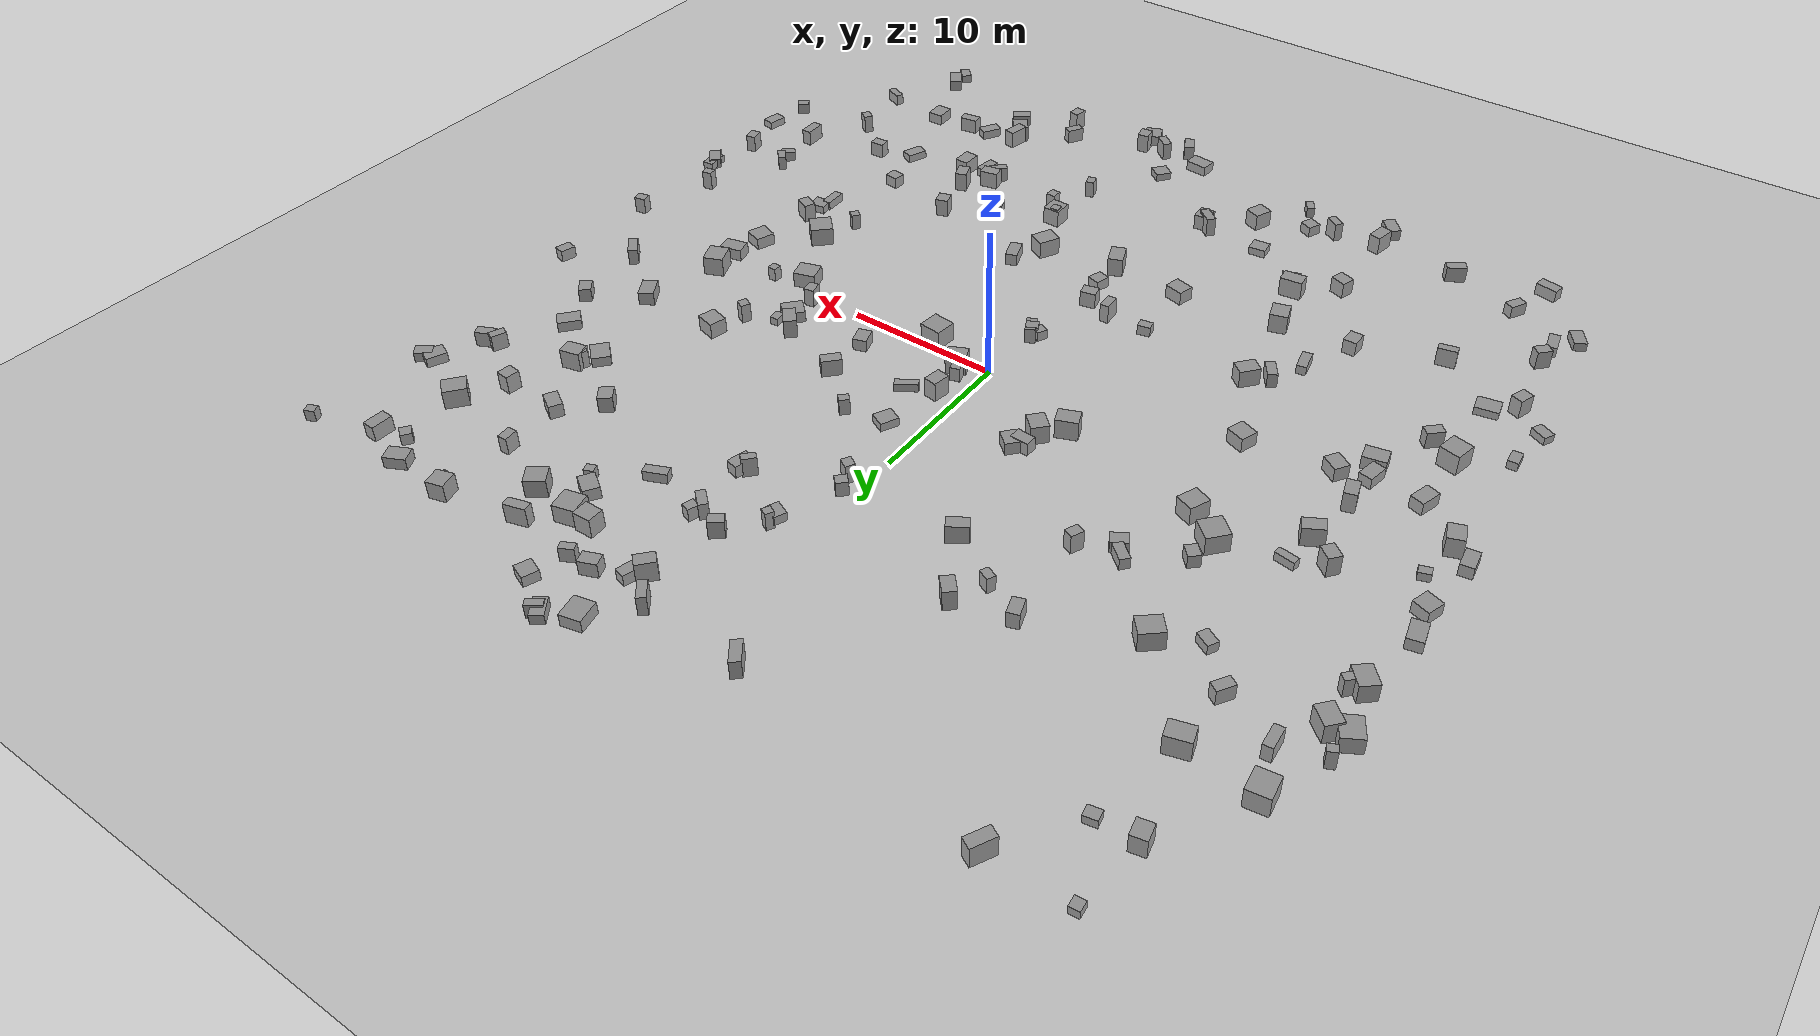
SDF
<sdf version='1.7'>
  <world name='default'>
    <light name='sun' type='directional'>
      <cast_shadows>1</cast_shadows>
      <pose>0 0 10 0 -0 0</pose>
      <diffuse>0.8 0.8 0.8 1</diffuse>
      <specular>0.2 0.2 0.2 1</specular>
      <attenuation>
        <range>1000</range>
        <constant>0.9</constant>
        <linear>0.01</linear>
        <quadratic>0.001</quadratic>
      </attenuation>
      <direction>-0.5 0.1 -0.9</direction>
      <spot>
        <inner_angle>0</inner_angle>
        <outer_angle>0</outer_angle>
        <falloff>0</falloff>
      </spot>
    </light>
    <model name='ground_plane'>
      <static>1</static>
      <link name='link'>
        <collision name='collision'>
          <geometry>
            <plane>
              <normal>0 0 1</normal>
              <size>100 100</size>
            </plane>
          </geometry>
          <surface>
            <friction>
              <ode>
                <mu>100</mu>
                <mu2>50</mu2>
              </ode>
              <torsional>
                <ode/>
              </torsional>
            </friction>
            <contact>
              <ode/>
            </contact>
            <bounce/>
          </surface>
          <max_contacts>10</max_contacts>
        </collision>
        <visual name='visual'>
          <cast_shadows>0</cast_shadows>
          <geometry>
            <plane>
              <normal>0 0 1</normal>
              <size>100 100</size>
            </plane>
          </geometry>
          <material>
            <script>
              <uri>file://media/materials/scripts/gazebo.material</uri>
              <name>Gazebo/Grey</name>
            </script>
          </material>
        </visual>
        <self_collide>0</self_collide>
        <enable_wind>0</enable_wind>
        <kinematic>0</kinematic>
      </link>
    </model>
    <gravity>0 0 -9.8</gravity>
    <magnetic_field>6e-06 2.3e-05 -4.2e-05</magnetic_field>
    <atmosphere type='adiabatic'/>
    <physics type='ode'>
      <max_step_size>0.001</max_step_size>
      <real_time_factor>1</real_time_factor>
      <real_time_update_rate>1000</real_time_update_rate>
    </physics>
    <scene>
      <ambient>0.4 0.4 0.4 1</ambient>
      <background>0.7 0.7 0.7 1</background>
      <shadows>1</shadows>
    </scene>
    <wind/>
    <spherical_coordinates>
      <surface_model>EARTH_WGS84</surface_model>
      <latitude_deg>0</latitude_deg>
      <longitude_deg>0</longitude_deg>
      <elevation>0</elevation>
      <heading_deg>0</heading_deg>
    </spherical_coordinates>
    <light name='user_directional_light_0' type='directional'>
      <pose>-7.86825 7.02908 1 0 -0 0</pose>
      <diffuse>0.5 0.5 0.5 1</diffuse>
      <specular>0.1 0.1 0.1 1</specular>
      <direction>0.1 0.1 -0.9</direction>
      <attenuation>
        <range>20</range>
        <constant>0.5</constant>
        <linear>0.01</linear>
        <quadratic>0.001</quadratic>
      </attenuation>
      <cast_shadows>1</cast_shadows>
      <spot>
        <inner_angle>0</inner_angle>
        <outer_angle>0</outer_angle>
        <falloff>0</falloff>
      </spot>
    </light>
    <light name='user_directional_light_1' type='directional'>
      <pose>-16.7576 13.165 1 0 -0 0</pose>
      <diffuse>0.5 0.5 0.5 1</diffuse>
      <specular>0.1 0.1 0.1 1</specular>
      <direction>0.1 0.1 -0.9</direction>
      <attenuation>
        <range>20</range>
        <constant>0.5</constant>
        <linear>0.01</linear>
        <quadratic>0.001</quadratic>
      </attenuation>
      <cast_shadows>1</cast_shadows>
      <spot>
        <inner_angle>0</inner_angle>
        <outer_angle>0</outer_angle>
        <falloff>0</falloff>
      </spot>
    </light>
    <light name='user_directional_light_2' type='directional'>
      <pose>0.944994 13.7599 1 0 -0 0</pose>
      <diffuse>0.5 0.5 0.5 1</diffuse>
      <specular>0.1 0.1 0.1 1</specular>
      <direction>0.1 0.1 -0.9</direction>
      <attenuation>
        <range>20</range>
        <constant>0.5</constant>
        <linear>0.01</linear>
        <quadratic>0.001</quadratic>
      </attenuation>
      <cast_shadows>1</cast_shadows>
      <spot>
        <inner_angle>0</inner_angle>
        <outer_angle>0</outer_angle>
        <falloff>0</falloff>
      </spot>
    </light>
    <light name='sun2' type='directional'>
      <cast_shadows>1</cast_shadows>
      <pose>3.61795 -11.1871 10 0 -0 0</pose>
      <diffuse>0.8 0.8 0.8 1</diffuse>
      <specular>0.2 0.2 0.2 1</specular>
      <attenuation>
        <range>1000</range>
        <constant>0.9</constant>
        <linear>0.01</linear>
        <quadratic>0.001</quadratic>
      </attenuation>
      <direction>-0.5 0.1 -0.9</direction>
      <spot>
        <inner_angle>0</inner_angle>
        <outer_angle>0</outer_angle>
        <falloff>0</falloff>
      </spot>
    </light>

    <model name='unit_box_0'>
      <static>true</static>
      <pose>5.627471768498843 -16.20319487183246 0.5 0 -0 328.3934222508951</pose>
      <link name='link'>
        <inertial>
          <mass>1</mass>
          <inertia>
            <ixx>0.166667</ixx>
            <ixy>0</ixy>
            <ixz>0</ixz>
            <iyy>0.166667</iyy>
            <iyz>0</iyz>
            <izz>0.166667</izz>
          </inertia>
          <pose>0 0 0 0 -0 0</pose>
        </inertial>
        <collision name='collision'>
          <geometry>
            <box>
              <size>0.5827919822700333 0.5535294650942497 1.420743045685274</size>
            </box>
          </geometry>
          <max_contacts>10</max_contacts>
          <surface>
            <contact>
              <ode/>
            </contact>
            <bounce/>
            <friction>
              <torsional>
                <ode/>
              </torsional>
              <ode/>
            </friction>
          </surface>
        </collision>
        <visual name='visual'>
          <geometry>
            <box>
              <size>0.5827919822700333 0.5535294650942497 1.420743045685274</size>
            </box>
          </geometry>
          <material>
            <script>
              <name>Gazebo/Grey</name>
              <uri>file://media/materials/scripts/gazebo.material</uri>
            </script>
          </material>
        </visual>
        <self_collide>0</self_collide>
        <enable_wind>0</enable_wind>
        <kinematic>0</kinematic>
      </link>
    </model>

    <model name='unit_box_1'>
      <static>true</static>
      <pose>-28.835129908935965 -9.783527657663477 0.5 0 -0 257.6770218911916</pose>
      <link name='link'>
        <inertial>
          <mass>1</mass>
          <inertia>
            <ixx>0.166667</ixx>
            <ixy>0</ixy>
            <ixz>0</ixz>
            <iyy>0.166667</iyy>
            <iyz>0</iyz>
            <izz>0.166667</izz>
          </inertia>
          <pose>0 0 0 0 -0 0</pose>
        </inertial>
        <collision name='collision'>
          <geometry>
            <box>
              <size>0.6333953735880681 1.008863503317531 0.5489622355451517</size>
            </box>
          </geometry>
          <max_contacts>10</max_contacts>
          <surface>
            <contact>
              <ode/>
            </contact>
            <bounce/>
            <friction>
              <torsional>
                <ode/>
              </torsional>
              <ode/>
            </friction>
          </surface>
        </collision>
        <visual name='visual'>
          <geometry>
            <box>
              <size>0.6333953735880681 1.008863503317531 0.5489622355451517</size>
            </box>
          </geometry>
          <material>
            <script>
              <name>Gazebo/Grey</name>
              <uri>file://media/materials/scripts/gazebo.material</uri>
            </script>
          </material>
        </visual>
        <self_collide>0</self_collide>
        <enable_wind>0</enable_wind>
        <kinematic>0</kinematic>
      </link>
    </model>

    <model name='unit_box_2'>
      <static>true</static>
      <pose>6.075183609601758 19.582829073267277 0.5 0 -0 326.4107492976476</pose>
      <link name='link'>
        <inertial>
          <mass>1</mass>
          <inertia>
            <ixx>0.166667</ixx>
            <ixy>0</ixy>
            <ixz>0</ixz>
            <iyy>0.166667</iyy>
            <iyz>0</iyz>
            <izz>0.166667</izz>
          </inertia>
          <pose>0 0 0 0 -0 0</pose>
        </inertial>
        <collision name='collision'>
          <geometry>
            <box>
              <size>0.6266694301505267 0.7147086828957209 0.8529961240803844</size>
            </box>
          </geometry>
          <max_contacts>10</max_contacts>
          <surface>
            <contact>
              <ode/>
            </contact>
            <bounce/>
            <friction>
              <torsional>
                <ode/>
              </torsional>
              <ode/>
            </friction>
          </surface>
        </collision>
        <visual name='visual'>
          <geometry>
            <box>
              <size>0.6266694301505267 0.7147086828957209 0.8529961240803844</size>
            </box>
          </geometry>
          <material>
            <script>
              <name>Gazebo/Grey</name>
              <uri>file://media/materials/scripts/gazebo.material</uri>
            </script>
          </material>
        </visual>
        <self_collide>0</self_collide>
        <enable_wind>0</enable_wind>
        <kinematic>0</kinematic>
      </link>
    </model>

    <model name='unit_box_3'>
      <static>true</static>
      <pose>-18.853921231633112 28.278634280664065 0.5 0 -0 161.31031445125913</pose>
      <link name='link'>
        <inertial>
          <mass>1</mass>
          <inertia>
            <ixx>0.166667</ixx>
            <ixy>0</ixy>
            <ixz>0</ixz>
            <iyy>0.166667</iyy>
            <iyz>0</iyz>
            <izz>0.166667</izz>
          </inertia>
          <pose>0 0 0 0 -0 0</pose>
        </inertial>
        <collision name='collision'>
          <geometry>
            <box>
              <size>1.4690283998809486 0.7201848135264792 1.498329860531034</size>
            </box>
          </geometry>
          <max_contacts>10</max_contacts>
          <surface>
            <contact>
              <ode/>
            </contact>
            <bounce/>
            <friction>
              <torsional>
                <ode/>
              </torsional>
              <ode/>
            </friction>
          </surface>
        </collision>
        <visual name='visual'>
          <geometry>
            <box>
              <size>1.4690283998809486 0.7201848135264792 1.498329860531034</size>
            </box>
          </geometry>
          <material>
            <script>
              <name>Gazebo/Grey</name>
              <uri>file://media/materials/scripts/gazebo.material</uri>
            </script>
          </material>
        </visual>
        <self_collide>0</self_collide>
        <enable_wind>0</enable_wind>
        <kinematic>0</kinematic>
      </link>
    </model>

    <model name='unit_box_4'>
      <static>true</static>
      <pose>-29.22784455926808 3.5906391807255034 0.5 0 -0 254.1489944872461</pose>
      <link name='link'>
        <inertial>
          <mass>1</mass>
          <inertia>
            <ixx>0.166667</ixx>
            <ixy>0</ixy>
            <ixz>0</ixz>
            <iyy>0.166667</iyy>
            <iyz>0</iyz>
            <izz>0.166667</izz>
          </inertia>
          <pose>0 0 0 0 -0 0</pose>
        </inertial>
        <collision name='collision'>
          <geometry>
            <box>
              <size>1.1214604294550323 1.1558776555138264 0.8068584248671594</size>
            </box>
          </geometry>
          <max_contacts>10</max_contacts>
          <surface>
            <contact>
              <ode/>
            </contact>
            <bounce/>
            <friction>
              <torsional>
                <ode/>
              </torsional>
              <ode/>
            </friction>
          </surface>
        </collision>
        <visual name='visual'>
          <geometry>
            <box>
              <size>1.1214604294550323 1.1558776555138264 0.8068584248671594</size>
            </box>
          </geometry>
          <material>
            <script>
              <name>Gazebo/Grey</name>
              <uri>file://media/materials/scripts/gazebo.material</uri>
            </script>
          </material>
        </visual>
        <self_collide>0</self_collide>
        <enable_wind>0</enable_wind>
        <kinematic>0</kinematic>
      </link>
    </model>

    <model name='unit_box_5'>
      <static>true</static>
      <pose>-0.5888013018914684 -13.825873107875235 0.5 0 -0 323.95076612812113</pose>
      <link name='link'>
        <inertial>
          <mass>1</mass>
          <inertia>
            <ixx>0.166667</ixx>
            <ixy>0</ixy>
            <ixz>0</ixz>
            <iyy>0.166667</iyy>
            <iyz>0</iyz>
            <izz>0.166667</izz>
          </inertia>
          <pose>0 0 0 0 -0 0</pose>
        </inertial>
        <collision name='collision'>
          <geometry>
            <box>
              <size>0.9740812102403196 1.4679312028211413 1.3884404087417037</size>
            </box>
          </geometry>
          <max_contacts>10</max_contacts>
          <surface>
            <contact>
              <ode/>
            </contact>
            <bounce/>
            <friction>
              <torsional>
                <ode/>
              </torsional>
              <ode/>
            </friction>
          </surface>
        </collision>
        <visual name='visual'>
          <geometry>
            <box>
              <size>0.9740812102403196 1.4679312028211413 1.3884404087417037</size>
            </box>
          </geometry>
          <material>
            <script>
              <name>Gazebo/Grey</name>
              <uri>file://media/materials/scripts/gazebo.material</uri>
            </script>
          </material>
        </visual>
        <self_collide>0</self_collide>
        <enable_wind>0</enable_wind>
        <kinematic>0</kinematic>
      </link>
    </model>

    <model name='unit_box_6'>
      <static>true</static>
      <pose>-23.114549735129497 18.156944835991993 0.5 0 -0 80.38149467177092</pose>
      <link name='link'>
        <inertial>
          <mass>1</mass>
          <inertia>
            <ixx>0.166667</ixx>
            <ixy>0</ixy>
            <ixz>0</ixz>
            <iyy>0.166667</iyy>
            <iyz>0</iyz>
            <izz>0.166667</izz>
          </inertia>
          <pose>0 0 0 0 -0 0</pose>
        </inertial>
        <collision name='collision'>
          <geometry>
            <box>
              <size>1.0977249225586028 1.4722601884767523 1.4116412109805065</size>
            </box>
          </geometry>
          <max_contacts>10</max_contacts>
          <surface>
            <contact>
              <ode/>
            </contact>
            <bounce/>
            <friction>
              <torsional>
                <ode/>
              </torsional>
              <ode/>
            </friction>
          </surface>
        </collision>
        <visual name='visual'>
          <geometry>
            <box>
              <size>1.0977249225586028 1.4722601884767523 1.4116412109805065</size>
            </box>
          </geometry>
          <material>
            <script>
              <name>Gazebo/Grey</name>
              <uri>file://media/materials/scripts/gazebo.material</uri>
            </script>
          </material>
        </visual>
        <self_collide>0</self_collide>
        <enable_wind>0</enable_wind>
        <kinematic>0</kinematic>
      </link>
    </model>

    <model name='unit_box_7'>
      <static>true</static>
      <pose>-12.422805338567617 15.797731349955072 0.5 0 -0 243.78437469421218</pose>
      <link name='link'>
        <inertial>
          <mass>1</mass>
          <inertia>
            <ixx>0.166667</ixx>
            <ixy>0</ixy>
            <ixz>0</ixz>
            <iyy>0.166667</iyy>
            <iyz>0</iyz>
            <izz>0.166667</izz>
          </inertia>
          <pose>0 0 0 0 -0 0</pose>
        </inertial>
        <collision name='collision'>
          <geometry>
            <box>
              <size>1.1689401038444207 0.7425306193366392 1.0525273627679501</size>
            </box>
          </geometry>
          <max_contacts>10</max_contacts>
          <surface>
            <contact>
              <ode/>
            </contact>
            <bounce/>
            <friction>
              <torsional>
                <ode/>
              </torsional>
              <ode/>
            </friction>
          </surface>
        </collision>
        <visual name='visual'>
          <geometry>
            <box>
              <size>1.1689401038444207 0.7425306193366392 1.0525273627679501</size>
            </box>
          </geometry>
          <material>
            <script>
              <name>Gazebo/Grey</name>
              <uri>file://media/materials/scripts/gazebo.material</uri>
            </script>
          </material>
        </visual>
        <self_collide>0</self_collide>
        <enable_wind>0</enable_wind>
        <kinematic>0</kinematic>
      </link>
    </model>

    <model name='unit_box_8'>
      <static>true</static>
      <pose>13.526247484848206 25.072226725004846 0.5 0 -0 235.8880812467848</pose>
      <link name='link'>
        <inertial>
          <mass>1</mass>
          <inertia>
            <ixx>0.166667</ixx>
            <ixy>0</ixy>
            <ixz>0</ixz>
            <iyy>0.166667</iyy>
            <iyz>0</iyz>
            <izz>0.166667</izz>
          </inertia>
          <pose>0 0 0 0 -0 0</pose>
        </inertial>
        <collision name='collision'>
          <geometry>
            <box>
              <size>1.3976044286606641 0.6081127395378836 1.4346002221633043</size>
            </box>
          </geometry>
          <max_contacts>10</max_contacts>
          <surface>
            <contact>
              <ode/>
            </contact>
            <bounce/>
            <friction>
              <torsional>
                <ode/>
              </torsional>
              <ode/>
            </friction>
          </surface>
        </collision>
        <visual name='visual'>
          <geometry>
            <box>
              <size>1.3976044286606641 0.6081127395378836 1.4346002221633043</size>
            </box>
          </geometry>
          <material>
            <script>
              <name>Gazebo/Grey</name>
              <uri>file://media/materials/scripts/gazebo.material</uri>
            </script>
          </material>
        </visual>
        <self_collide>0</self_collide>
        <enable_wind>0</enable_wind>
        <kinematic>0</kinematic>
      </link>
    </model>

    <model name='unit_box_9'>
      <static>true</static>
      <pose>20.26620788877139 -2.749642604939659 0.5 0 -0 134.7541991440881</pose>
      <link name='link'>
        <inertial>
          <mass>1</mass>
          <inertia>
            <ixx>0.166667</ixx>
            <ixy>0</ixy>
            <ixz>0</ixz>
            <iyy>0.166667</iyy>
            <iyz>0</iyz>
            <izz>0.166667</izz>
          </inertia>
          <pose>0 0 0 0 -0 0</pose>
        </inertial>
        <collision name='collision'>
          <geometry>
            <box>
              <size>1.24650252537936 1.253774818010641 0.7950120379356779</size>
            </box>
          </geometry>
          <max_contacts>10</max_contacts>
          <surface>
            <contact>
              <ode/>
            </contact>
            <bounce/>
            <friction>
              <torsional>
                <ode/>
              </torsional>
              <ode/>
            </friction>
          </surface>
        </collision>
        <visual name='visual'>
          <geometry>
            <box>
              <size>1.24650252537936 1.253774818010641 0.7950120379356779</size>
            </box>
          </geometry>
          <material>
            <script>
              <name>Gazebo/Grey</name>
              <uri>file://media/materials/scripts/gazebo.material</uri>
            </script>
          </material>
        </visual>
        <self_collide>0</self_collide>
        <enable_wind>0</enable_wind>
        <kinematic>0</kinematic>
      </link>
    </model>

    <model name='unit_box_10'>
      <static>true</static>
      <pose>5.437323707347929 -10.792670169444165 0.5 0 -0 201.39579407565316</pose>
      <link name='link'>
        <inertial>
          <mass>1</mass>
          <inertia>
            <ixx>0.166667</ixx>
            <ixy>0</ixy>
            <ixz>0</ixz>
            <iyy>0.166667</iyy>
            <iyz>0</iyz>
            <izz>0.166667</izz>
          </inertia>
          <pose>0 0 0 0 -0 0</pose>
        </inertial>
        <collision name='collision'>
          <geometry>
            <box>
              <size>0.7689403991867364 1.4520089688627191 0.8072029405422583</size>
            </box>
          </geometry>
          <max_contacts>10</max_contacts>
          <surface>
            <contact>
              <ode/>
            </contact>
            <bounce/>
            <friction>
              <torsional>
                <ode/>
              </torsional>
              <ode/>
            </friction>
          </surface>
        </collision>
        <visual name='visual'>
          <geometry>
            <box>
              <size>0.7689403991867364 1.4520089688627191 0.8072029405422583</size>
            </box>
          </geometry>
          <material>
            <script>
              <name>Gazebo/Grey</name>
              <uri>file://media/materials/scripts/gazebo.material</uri>
            </script>
          </material>
        </visual>
        <self_collide>0</self_collide>
        <enable_wind>0</enable_wind>
        <kinematic>0</kinematic>
      </link>
    </model>

    <model name='unit_box_11'>
      <static>true</static>
      <pose>-26.731967139765874 15.79381174776082 0.5 0 -0 48.758614556647814</pose>
      <link name='link'>
        <inertial>
          <mass>1</mass>
          <inertia>
            <ixx>0.166667</ixx>
            <ixy>0</ixy>
            <ixz>0</ixz>
            <iyy>0.166667</iyy>
            <iyz>0</iyz>
            <izz>0.166667</izz>
          </inertia>
          <pose>0 0 0 0 -0 0</pose>
        </inertial>
        <collision name='collision'>
          <geometry>
            <box>
              <size>1.4363798555520337 0.5857894299789224 1.0255808748022714</size>
            </box>
          </geometry>
          <max_contacts>10</max_contacts>
          <surface>
            <contact>
              <ode/>
            </contact>
            <bounce/>
            <friction>
              <torsional>
                <ode/>
              </torsional>
              <ode/>
            </friction>
          </surface>
        </collision>
        <visual name='visual'>
          <geometry>
            <box>
              <size>1.4363798555520337 0.5857894299789224 1.0255808748022714</size>
            </box>
          </geometry>
          <material>
            <script>
              <name>Gazebo/Grey</name>
              <uri>file://media/materials/scripts/gazebo.material</uri>
            </script>
          </material>
        </visual>
        <self_collide>0</self_collide>
        <enable_wind>0</enable_wind>
        <kinematic>0</kinematic>
      </link>
    </model>

    <model name='unit_box_12'>
      <static>true</static>
      <pose>4.544029123333701 -0.9721439150786608 0.5 0 -0 295.1919709288443</pose>
      <link name='link'>
        <inertial>
          <mass>1</mass>
          <inertia>
            <ixx>0.166667</ixx>
            <ixy>0</ixy>
            <ixz>0</ixz>
            <iyy>0.166667</iyy>
            <iyz>0</iyz>
            <izz>0.166667</izz>
          </inertia>
          <pose>0 0 0 0 -0 0</pose>
        </inertial>
        <collision name='collision'>
          <geometry>
            <box>
              <size>1.4717701889387484 1.3670608301999336 1.337696717127048</size>
            </box>
          </geometry>
          <max_contacts>10</max_contacts>
          <surface>
            <contact>
              <ode/>
            </contact>
            <bounce/>
            <friction>
              <torsional>
                <ode/>
              </torsional>
              <ode/>
            </friction>
          </surface>
        </collision>
        <visual name='visual'>
          <geometry>
            <box>
              <size>1.4717701889387484 1.3670608301999336 1.337696717127048</size>
            </box>
          </geometry>
          <material>
            <script>
              <name>Gazebo/Grey</name>
              <uri>file://media/materials/scripts/gazebo.material</uri>
            </script>
          </material>
        </visual>
        <self_collide>0</self_collide>
        <enable_wind>0</enable_wind>
        <kinematic>0</kinematic>
      </link>
    </model>

    <model name='unit_box_13'>
      <static>true</static>
      <pose>6.861349307954114 -17.79102723468238 0.5 0 -0 43.92288849873564</pose>
      <link name='link'>
        <inertial>
          <mass>1</mass>
          <inertia>
            <ixx>0.166667</ixx>
            <ixy>0</ixy>
            <ixz>0</ixz>
            <iyy>0.166667</iyy>
            <iyz>0</iyz>
            <izz>0.166667</izz>
          </inertia>
          <pose>0 0 0 0 -0 0</pose>
        </inertial>
        <collision name='collision'>
          <geometry>
            <box>
              <size>0.6055544027230478 0.6857820129138893 1.1537404358124181</size>
            </box>
          </geometry>
          <max_contacts>10</max_contacts>
          <surface>
            <contact>
              <ode/>
            </contact>
            <bounce/>
            <friction>
              <torsional>
                <ode/>
              </torsional>
              <ode/>
            </friction>
          </surface>
        </collision>
        <visual name='visual'>
          <geometry>
            <box>
              <size>0.6055544027230478 0.6857820129138893 1.1537404358124181</size>
            </box>
          </geometry>
          <material>
            <script>
              <name>Gazebo/Grey</name>
              <uri>file://media/materials/scripts/gazebo.material</uri>
            </script>
          </material>
        </visual>
        <self_collide>0</self_collide>
        <enable_wind>0</enable_wind>
        <kinematic>0</kinematic>
      </link>
    </model>

    <model name='unit_box_14'>
      <static>true</static>
      <pose>5.618380994731012 -20.709095346360606 0.5 0 -0 292.4153457704035</pose>
      <link name='link'>
        <inertial>
          <mass>1</mass>
          <inertia>
            <ixx>0.166667</ixx>
            <ixy>0</ixy>
            <ixz>0</ixz>
            <iyy>0.166667</iyy>
            <iyz>0</iyz>
            <izz>0.166667</izz>
          </inertia>
          <pose>0 0 0 0 -0 0</pose>
        </inertial>
        <collision name='collision'>
          <geometry>
            <box>
              <size>0.5567356589885245 0.7008477635557117 1.1573102387236456</size>
            </box>
          </geometry>
          <max_contacts>10</max_contacts>
          <surface>
            <contact>
              <ode/>
            </contact>
            <bounce/>
            <friction>
              <torsional>
                <ode/>
              </torsional>
              <ode/>
            </friction>
          </surface>
        </collision>
        <visual name='visual'>
          <geometry>
            <box>
              <size>0.5567356589885245 0.7008477635557117 1.1573102387236456</size>
            </box>
          </geometry>
          <material>
            <script>
              <name>Gazebo/Grey</name>
              <uri>file://media/materials/scripts/gazebo.material</uri>
            </script>
          </material>
        </visual>
        <self_collide>0</self_collide>
        <enable_wind>0</enable_wind>
        <kinematic>0</kinematic>
      </link>
    </model>

    <model name='unit_box_15'>
      <static>true</static>
      <pose>-22.42774986537877 -5.39817078722103 0.5 0 -0 26.89385585650175</pose>
      <link name='link'>
        <inertial>
          <mass>1</mass>
          <inertia>
            <ixx>0.166667</ixx>
            <ixy>0</ixy>
            <ixz>0</ixz>
            <iyy>0.166667</iyy>
            <iyz>0</iyz>
            <izz>0.166667</izz>
          </inertia>
          <pose>0 0 0 0 -0 0</pose>
        </inertial>
        <collision name='collision'>
          <geometry>
            <box>
              <size>1.0752779468340803 1.451434193957634 0.884597481298783</size>
            </box>
          </geometry>
          <max_contacts>10</max_contacts>
          <surface>
            <contact>
              <ode/>
            </contact>
            <bounce/>
            <friction>
              <torsional>
                <ode/>
              </torsional>
              <ode/>
            </friction>
          </surface>
        </collision>
        <visual name='visual'>
          <geometry>
            <box>
              <size>1.0752779468340803 1.451434193957634 0.884597481298783</size>
            </box>
          </geometry>
          <material>
            <script>
              <name>Gazebo/Grey</name>
              <uri>file://media/materials/scripts/gazebo.material</uri>
            </script>
          </material>
        </visual>
        <self_collide>0</self_collide>
        <enable_wind>0</enable_wind>
        <kinematic>0</kinematic>
      </link>
    </model>

    <model name='unit_box_16'>
      <static>true</static>
      <pose>1.8598666684858856 0.7283571970139668 0.5 0 -0 67.96468003619916</pose>
      <link name='link'>
        <inertial>
          <mass>1</mass>
          <inertia>
            <ixx>0.166667</ixx>
            <ixy>0</ixy>
            <ixz>0</ixz>
            <iyy>0.166667</iyy>
            <iyz>0</iyz>
            <izz>0.166667</izz>
          </inertia>
          <pose>0 0 0 0 -0 0</pose>
        </inertial>
        <collision name='collision'>
          <geometry>
            <box>
              <size>1.0478265378507603 1.2723478876649952 1.3962599487506537</size>
            </box>
          </geometry>
          <max_contacts>10</max_contacts>
          <surface>
            <contact>
              <ode/>
            </contact>
            <bounce/>
            <friction>
              <torsional>
                <ode/>
              </torsional>
              <ode/>
            </friction>
          </surface>
        </collision>
        <visual name='visual'>
          <geometry>
            <box>
              <size>1.0478265378507603 1.2723478876649952 1.3962599487506537</size>
            </box>
          </geometry>
          <material>
            <script>
              <name>Gazebo/Grey</name>
              <uri>file://media/materials/scripts/gazebo.material</uri>
            </script>
          </material>
        </visual>
        <self_collide>0</self_collide>
        <enable_wind>0</enable_wind>
        <kinematic>0</kinematic>
      </link>
    </model>

    <model name='unit_box_17'>
      <static>true</static>
      <pose>12.66213659052233 -12.962916933397935 0.5 0 -0 286.207196710561</pose>
      <link name='link'>
        <inertial>
          <mass>1</mass>
          <inertia>
            <ixx>0.166667</ixx>
            <ixy>0</ixy>
            <ixz>0</ixz>
            <iyy>0.166667</iyy>
            <iyz>0</iyz>
            <izz>0.166667</izz>
          </inertia>
          <pose>0 0 0 0 -0 0</pose>
        </inertial>
        <collision name='collision'>
          <geometry>
            <box>
              <size>0.8311423269497479 0.8872742078254097 1.2710147313330409</size>
            </box>
          </geometry>
          <max_contacts>10</max_contacts>
          <surface>
            <contact>
              <ode/>
            </contact>
            <bounce/>
            <friction>
              <torsional>
                <ode/>
              </torsional>
              <ode/>
            </friction>
          </surface>
        </collision>
        <visual name='visual'>
          <geometry>
            <box>
              <size>0.8311423269497479 0.8872742078254097 1.2710147313330409</size>
            </box>
          </geometry>
          <material>
            <script>
              <name>Gazebo/Grey</name>
              <uri>file://media/materials/scripts/gazebo.material</uri>
            </script>
          </material>
        </visual>
        <self_collide>0</self_collide>
        <enable_wind>0</enable_wind>
        <kinematic>0</kinematic>
      </link>
    </model>

    <model name='unit_box_18'>
      <static>true</static>
      <pose>9.636020102886391 -14.911595727227738 0.5 0 -0 169.99521131837008</pose>
      <link name='link'>
        <inertial>
          <mass>1</mass>
          <inertia>
            <ixx>0.166667</ixx>
            <ixy>0</ixy>
            <ixz>0</ixz>
            <iyy>0.166667</iyy>
            <iyz>0</iyz>
            <izz>0.166667</izz>
          </inertia>
          <pose>0 0 0 0 -0 0</pose>
        </inertial>
        <collision name='collision'>
          <geometry>
            <box>
              <size>0.9842812903339123 0.8837834291854924 0.6274265674525699</size>
            </box>
          </geometry>
          <max_contacts>10</max_contacts>
          <surface>
            <contact>
              <ode/>
            </contact>
            <bounce/>
            <friction>
              <torsional>
                <ode/>
              </torsional>
              <ode/>
            </friction>
          </surface>
        </collision>
        <visual name='visual'>
          <geometry>
            <box>
              <size>0.9842812903339123 0.8837834291854924 0.6274265674525699</size>
            </box>
          </geometry>
          <material>
            <script>
              <name>Gazebo/Grey</name>
              <uri>file://media/materials/scripts/gazebo.material</uri>
            </script>
          </material>
        </visual>
        <self_collide>0</self_collide>
        <enable_wind>0</enable_wind>
        <kinematic>0</kinematic>
      </link>
    </model>

    <model name='unit_box_19'>
      <static>true</static>
      <pose>16.53977706462488 15.395428952619518 0.5 0 -0 292.82832951385666</pose>
      <link name='link'>
        <inertial>
          <mass>1</mass>
          <inertia>
            <ixx>0.166667</ixx>
            <ixy>0</ixy>
            <ixz>0</ixz>
            <iyy>0.166667</iyy>
            <iyz>0</iyz>
            <izz>0.166667</izz>
          </inertia>
          <pose>0 0 0 0 -0 0</pose>
        </inertial>
        <collision name='collision'>
          <geometry>
            <box>
              <size>0.9097543581399401 1.0486898294674742 1.058557427915837</size>
            </box>
          </geometry>
          <max_contacts>10</max_contacts>
          <surface>
            <contact>
              <ode/>
            </contact>
            <bounce/>
            <friction>
              <torsional>
                <ode/>
              </torsional>
              <ode/>
            </friction>
          </surface>
        </collision>
        <visual name='visual'>
          <geometry>
            <box>
              <size>0.9097543581399401 1.0486898294674742 1.058557427915837</size>
            </box>
          </geometry>
          <material>
            <script>
              <name>Gazebo/Grey</name>
              <uri>file://media/materials/scripts/gazebo.material</uri>
            </script>
          </material>
        </visual>
        <self_collide>0</self_collide>
        <enable_wind>0</enable_wind>
        <kinematic>0</kinematic>
      </link>
    </model>

    <model name='unit_box_20'>
      <static>true</static>
      <pose>29.36088644894142 -8.22944636349619 0.5 0 -0 121.04933037444114</pose>
      <link name='link'>
        <inertial>
          <mass>1</mass>
          <inertia>
            <ixx>0.166667</ixx>
            <ixy>0</ixy>
            <ixz>0</ixz>
            <iyy>0.166667</iyy>
            <iyz>0</iyz>
            <izz>0.166667</izz>
          </inertia>
          <pose>0 0 0 0 -0 0</pose>
        </inertial>
        <collision name='collision'>
          <geometry>
            <box>
              <size>1.4406663692053037 0.7334797075197601 0.5174091967911121</size>
            </box>
          </geometry>
          <max_contacts>10</max_contacts>
          <surface>
            <contact>
              <ode/>
            </contact>
            <bounce/>
            <friction>
              <torsional>
                <ode/>
              </torsional>
              <ode/>
            </friction>
          </surface>
        </collision>
        <visual name='visual'>
          <geometry>
            <box>
              <size>1.4406663692053037 0.7334797075197601 0.5174091967911121</size>
            </box>
          </geometry>
          <material>
            <script>
              <name>Gazebo/Grey</name>
              <uri>file://media/materials/scripts/gazebo.material</uri>
            </script>
          </material>
        </visual>
        <self_collide>0</self_collide>
        <enable_wind>0</enable_wind>
        <kinematic>0</kinematic>
      </link>
    </model>

    <model name='unit_box_21'>
      <static>true</static>
      <pose>26.06764423855877 3.290163727536026 0.5 0 -0 19.58643026135544</pose>
      <link name='link'>
        <inertial>
          <mass>1</mass>
          <inertia>
            <ixx>0.166667</ixx>
            <ixy>0</ixy>
            <ixz>0</ixz>
            <iyy>0.166667</iyy>
            <iyz>0</iyz>
            <izz>0.166667</izz>
          </inertia>
          <pose>0 0 0 0 -0 0</pose>
        </inertial>
        <collision name='collision'>
          <geometry>
            <box>
              <size>0.6197711131338078 1.4030050128848504 1.08956549549722</size>
            </box>
          </geometry>
          <max_contacts>10</max_contacts>
          <surface>
            <contact>
              <ode/>
            </contact>
            <bounce/>
            <friction>
              <torsional>
                <ode/>
              </torsional>
              <ode/>
            </friction>
          </surface>
        </collision>
        <visual name='visual'>
          <geometry>
            <box>
              <size>0.6197711131338078 1.4030050128848504 1.08956549549722</size>
            </box>
          </geometry>
          <material>
            <script>
              <name>Gazebo/Grey</name>
              <uri>file://media/materials/scripts/gazebo.material</uri>
            </script>
          </material>
        </visual>
        <self_collide>0</self_collide>
        <enable_wind>0</enable_wind>
        <kinematic>0</kinematic>
      </link>
    </model>

    <model name='unit_box_22'>
      <static>true</static>
      <pose>29.514338587605934 -8.558415328057897 0.5 0 -0 225.32562232518265</pose>
      <link name='link'>
        <inertial>
          <mass>1</mass>
          <inertia>
            <ixx>0.166667</ixx>
            <ixy>0</ixy>
            <ixz>0</ixz>
            <iyy>0.166667</iyy>
            <iyz>0</iyz>
            <izz>0.166667</izz>
          </inertia>
          <pose>0 0 0 0 -0 0</pose>
        </inertial>
        <collision name='collision'>
          <geometry>
            <box>
              <size>1.3274998079993439 0.7774295099843246 0.6819152240145191</size>
            </box>
          </geometry>
          <max_contacts>10</max_contacts>
          <surface>
            <contact>
              <ode/>
            </contact>
            <bounce/>
            <friction>
              <torsional>
                <ode/>
              </torsional>
              <ode/>
            </friction>
          </surface>
        </collision>
        <visual name='visual'>
          <geometry>
            <box>
              <size>1.3274998079993439 0.7774295099843246 0.6819152240145191</size>
            </box>
          </geometry>
          <material>
            <script>
              <name>Gazebo/Grey</name>
              <uri>file://media/materials/scripts/gazebo.material</uri>
            </script>
          </material>
        </visual>
        <self_collide>0</self_collide>
        <enable_wind>0</enable_wind>
        <kinematic>0</kinematic>
      </link>
    </model>

    <model name='unit_box_23'>
      <static>true</static>
      <pose>-27.597285127594194 18.573005559899144 0.5 0 -0 22.117648178212434</pose>
      <link name='link'>
        <inertial>
          <mass>1</mass>
          <inertia>
            <ixx>0.166667</ixx>
            <ixy>0</ixy>
            <ixz>0</ixz>
            <iyy>0.166667</iyy>
            <iyz>0</iyz>
            <izz>0.166667</izz>
          </inertia>
          <pose>0 0 0 0 -0 0</pose>
        </inertial>
        <collision name='collision'>
          <geometry>
            <box>
              <size>1.3419519475900668 1.4863007726982276 1.362194990856641</size>
            </box>
          </geometry>
          <max_contacts>10</max_contacts>
          <surface>
            <contact>
              <ode/>
            </contact>
            <bounce/>
            <friction>
              <torsional>
                <ode/>
              </torsional>
              <ode/>
            </friction>
          </surface>
        </collision>
        <visual name='visual'>
          <geometry>
            <box>
              <size>1.3419519475900668 1.4863007726982276 1.362194990856641</size>
            </box>
          </geometry>
          <material>
            <script>
              <name>Gazebo/Grey</name>
              <uri>file://media/materials/scripts/gazebo.material</uri>
            </script>
          </material>
        </visual>
        <self_collide>0</self_collide>
        <enable_wind>0</enable_wind>
        <kinematic>0</kinematic>
      </link>
    </model>

    <model name='unit_box_24'>
      <static>true</static>
      <pose>-5.674999034693748 -23.92239845263095 0.5 0 -0 20.024094226079665</pose>
      <link name='link'>
        <inertial>
          <mass>1</mass>
          <inertia>
            <ixx>0.166667</ixx>
            <ixy>0</ixy>
            <ixz>0</ixz>
            <iyy>0.166667</iyy>
            <iyz>0</iyz>
            <izz>0.166667</izz>
          </inertia>
          <pose>0 0 0 0 -0 0</pose>
        </inertial>
        <collision name='collision'>
          <geometry>
            <box>
              <size>1.215337846311781 1.0442918365608516 1.1445933310478278</size>
            </box>
          </geometry>
          <max_contacts>10</max_contacts>
          <surface>
            <contact>
              <ode/>
            </contact>
            <bounce/>
            <friction>
              <torsional>
                <ode/>
              </torsional>
              <ode/>
            </friction>
          </surface>
        </collision>
        <visual name='visual'>
          <geometry>
            <box>
              <size>1.215337846311781 1.0442918365608516 1.1445933310478278</size>
            </box>
          </geometry>
          <material>
            <script>
              <name>Gazebo/Grey</name>
              <uri>file://media/materials/scripts/gazebo.material</uri>
            </script>
          </material>
        </visual>
        <self_collide>0</self_collide>
        <enable_wind>0</enable_wind>
        <kinematic>0</kinematic>
      </link>
    </model>

    <model name='unit_box_25'>
      <static>true</static>
      <pose>-5.481367037540078 4.659173477378474 0.5 0 -0 152.3028976642726</pose>
      <link name='link'>
        <inertial>
          <mass>1</mass>
          <inertia>
            <ixx>0.166667</ixx>
            <ixy>0</ixy>
            <ixz>0</ixz>
            <iyy>0.166667</iyy>
            <iyz>0</iyz>
            <izz>0.166667</izz>
          </inertia>
          <pose>0 0 0 0 -0 0</pose>
        </inertial>
        <collision name='collision'>
          <geometry>
            <box>
              <size>0.7774207279172025 1.1902266741369176 0.8726082648236624</size>
            </box>
          </geometry>
          <max_contacts>10</max_contacts>
          <surface>
            <contact>
              <ode/>
            </contact>
            <bounce/>
            <friction>
              <torsional>
                <ode/>
              </torsional>
              <ode/>
            </friction>
          </surface>
        </collision>
        <visual name='visual'>
          <geometry>
            <box>
              <size>0.7774207279172025 1.1902266741369176 0.8726082648236624</size>
            </box>
          </geometry>
          <material>
            <script>
              <name>Gazebo/Grey</name>
              <uri>file://media/materials/scripts/gazebo.material</uri>
            </script>
          </material>
        </visual>
        <self_collide>0</self_collide>
        <enable_wind>0</enable_wind>
        <kinematic>0</kinematic>
      </link>
    </model>

    <model name='unit_box_26'>
      <static>true</static>
      <pose>-14.091392155086497 8.478652632987668 0.5 0 -0 110.48400537690175</pose>
      <link name='link'>
        <inertial>
          <mass>1</mass>
          <inertia>
            <ixx>0.166667</ixx>
            <ixy>0</ixy>
            <ixz>0</ixz>
            <iyy>0.166667</iyy>
            <iyz>0</iyz>
            <izz>0.166667</izz>
          </inertia>
          <pose>0 0 0 0 -0 0</pose>
        </inertial>
        <collision name='collision'>
          <geometry>
            <box>
              <size>1.061084775640069 0.8073565125365411 0.7287802840965566</size>
            </box>
          </geometry>
          <max_contacts>10</max_contacts>
          <surface>
            <contact>
              <ode/>
            </contact>
            <bounce/>
            <friction>
              <torsional>
                <ode/>
              </torsional>
              <ode/>
            </friction>
          </surface>
        </collision>
        <visual name='visual'>
          <geometry>
            <box>
              <size>1.061084775640069 0.8073565125365411 0.7287802840965566</size>
            </box>
          </geometry>
          <material>
            <script>
              <name>Gazebo/Grey</name>
              <uri>file://media/materials/scripts/gazebo.material</uri>
            </script>
          </material>
        </visual>
        <self_collide>0</self_collide>
        <enable_wind>0</enable_wind>
        <kinematic>0</kinematic>
      </link>
    </model>

    <model name='unit_box_27'>
      <static>true</static>
      <pose>18.694011206480987 17.537227984825684 0.5 0 -0 156.56091539982643</pose>
      <link name='link'>
        <inertial>
          <mass>1</mass>
          <inertia>
            <ixx>0.166667</ixx>
            <ixy>0</ixy>
            <ixz>0</ixz>
            <iyy>0.166667</iyy>
            <iyz>0</iyz>
            <izz>0.166667</izz>
          </inertia>
          <pose>0 0 0 0 -0 0</pose>
        </inertial>
        <collision name='collision'>
          <geometry>
            <box>
              <size>1.3051033232458376 0.8619676094807414 0.9028728992414216</size>
            </box>
          </geometry>
          <max_contacts>10</max_contacts>
          <surface>
            <contact>
              <ode/>
            </contact>
            <bounce/>
            <friction>
              <torsional>
                <ode/>
              </torsional>
              <ode/>
            </friction>
          </surface>
        </collision>
        <visual name='visual'>
          <geometry>
            <box>
              <size>1.3051033232458376 0.8619676094807414 0.9028728992414216</size>
            </box>
          </geometry>
          <material>
            <script>
              <name>Gazebo/Grey</name>
              <uri>file://media/materials/scripts/gazebo.material</uri>
            </script>
          </material>
        </visual>
        <self_collide>0</self_collide>
        <enable_wind>0</enable_wind>
        <kinematic>0</kinematic>
      </link>
    </model>

    <model name='unit_box_28'>
      <static>true</static>
      <pose>7.335855545737282 29.440695560788072 0.5 0 -0 198.54745181263667</pose>
      <link name='link'>
        <inertial>
          <mass>1</mass>
          <inertia>
            <ixx>0.166667</ixx>
            <ixy>0</ixy>
            <ixz>0</ixz>
            <iyy>0.166667</iyy>
            <iyz>0</iyz>
            <izz>0.166667</izz>
          </inertia>
          <pose>0 0 0 0 -0 0</pose>
        </inertial>
        <collision name='collision'>
          <geometry>
            <box>
              <size>0.8034991458267305 1.3305237800313559 0.652747012599675</size>
            </box>
          </geometry>
          <max_contacts>10</max_contacts>
          <surface>
            <contact>
              <ode/>
            </contact>
            <bounce/>
            <friction>
              <torsional>
                <ode/>
              </torsional>
              <ode/>
            </friction>
          </surface>
        </collision>
        <visual name='visual'>
          <geometry>
            <box>
              <size>0.8034991458267305 1.3305237800313559 0.652747012599675</size>
            </box>
          </geometry>
          <material>
            <script>
              <name>Gazebo/Grey</name>
              <uri>file://media/materials/scripts/gazebo.material</uri>
            </script>
          </material>
        </visual>
        <self_collide>0</self_collide>
        <enable_wind>0</enable_wind>
        <kinematic>0</kinematic>
      </link>
    </model>

    <model name='unit_box_29'>
      <static>true</static>
      <pose>-17.90025591506668 5.190496679094579 0.5 0 -0 139.07926550696132</pose>
      <link name='link'>
        <inertial>
          <mass>1</mass>
          <inertia>
            <ixx>0.166667</ixx>
            <ixy>0</ixy>
            <ixz>0</ixz>
            <iyy>0.166667</iyy>
            <iyz>0</iyz>
            <izz>0.166667</izz>
          </inertia>
          <pose>0 0 0 0 -0 0</pose>
        </inertial>
        <collision name='collision'>
          <geometry>
            <box>
              <size>1.485671787790575 1.4774349979943575 1.292205282133597</size>
            </box>
          </geometry>
          <max_contacts>10</max_contacts>
          <surface>
            <contact>
              <ode/>
            </contact>
            <bounce/>
            <friction>
              <torsional>
                <ode/>
              </torsional>
              <ode/>
            </friction>
          </surface>
        </collision>
        <visual name='visual'>
          <geometry>
            <box>
              <size>1.485671787790575 1.4774349979943575 1.292205282133597</size>
            </box>
          </geometry>
          <material>
            <script>
              <name>Gazebo/Grey</name>
              <uri>file://media/materials/scripts/gazebo.material</uri>
            </script>
          </material>
        </visual>
        <self_collide>0</self_collide>
        <enable_wind>0</enable_wind>
        <kinematic>0</kinematic>
      </link>
    </model>

    <model name='unit_box_30'>
      <static>true</static>
      <pose>-5.7227796839441964 -8.65081539558837 0.5 0 -0 273.5123597073977</pose>
      <link name='link'>
        <inertial>
          <mass>1</mass>
          <inertia>
            <ixx>0.166667</ixx>
            <ixy>0</ixy>
            <ixz>0</ixz>
            <iyy>0.166667</iyy>
            <iyz>0</iyz>
            <izz>0.166667</izz>
          </inertia>
          <pose>0 0 0 0 -0 0</pose>
        </inertial>
        <collision name='collision'>
          <geometry>
            <box>
              <size>0.8382652194335364 0.6307499962533054 0.6695288904015347</size>
            </box>
          </geometry>
          <max_contacts>10</max_contacts>
          <surface>
            <contact>
              <ode/>
            </contact>
            <bounce/>
            <friction>
              <torsional>
                <ode/>
              </torsional>
              <ode/>
            </friction>
          </surface>
        </collision>
        <visual name='visual'>
          <geometry>
            <box>
              <size>0.8382652194335364 0.6307499962533054 0.6695288904015347</size>
            </box>
          </geometry>
          <material>
            <script>
              <name>Gazebo/Grey</name>
              <uri>file://media/materials/scripts/gazebo.material</uri>
            </script>
          </material>
        </visual>
        <self_collide>0</self_collide>
        <enable_wind>0</enable_wind>
        <kinematic>0</kinematic>
      </link>
    </model>

    <model name='unit_box_31'>
      <static>true</static>
      <pose>-14.150281883332969 -8.950827690536414 0.5 0 -0 278.62585095943035</pose>
      <link name='link'>
        <inertial>
          <mass>1</mass>
          <inertia>
            <ixx>0.166667</ixx>
            <ixy>0</ixy>
            <ixz>0</ixz>
            <iyy>0.166667</iyy>
            <iyz>0</iyz>
            <izz>0.166667</izz>
          </inertia>
          <pose>0 0 0 0 -0 0</pose>
        </inertial>
        <collision name='collision'>
          <geometry>
            <box>
              <size>1.2906249621792236 0.6320051280488989 0.9832819269284849</size>
            </box>
          </geometry>
          <max_contacts>10</max_contacts>
          <surface>
            <contact>
              <ode/>
            </contact>
            <bounce/>
            <friction>
              <torsional>
                <ode/>
              </torsional>
              <ode/>
            </friction>
          </surface>
        </collision>
        <visual name='visual'>
          <geometry>
            <box>
              <size>1.2906249621792236 0.6320051280488989 0.9832819269284849</size>
            </box>
          </geometry>
          <material>
            <script>
              <name>Gazebo/Grey</name>
              <uri>file://media/materials/scripts/gazebo.material</uri>
            </script>
          </material>
        </visual>
        <self_collide>0</self_collide>
        <enable_wind>0</enable_wind>
        <kinematic>0</kinematic>
      </link>
    </model>

    <model name='unit_box_32'>
      <static>true</static>
      <pose>4.066421986708839 -28.262519831651417 0.5 0 -0 120.25010938333372</pose>
      <link name='link'>
        <inertial>
          <mass>1</mass>
          <inertia>
            <ixx>0.166667</ixx>
            <ixy>0</ixy>
            <ixz>0</ixz>
            <iyy>0.166667</iyy>
            <iyz>0</iyz>
            <izz>0.166667</izz>
          </inertia>
          <pose>0 0 0 0 -0 0</pose>
        </inertial>
        <collision name='collision'>
          <geometry>
            <box>
              <size>0.5795722155270291 1.1500049747034757 1.2832028245057363</size>
            </box>
          </geometry>
          <max_contacts>10</max_contacts>
          <surface>
            <contact>
              <ode/>
            </contact>
            <bounce/>
            <friction>
              <torsional>
                <ode/>
              </torsional>
              <ode/>
            </friction>
          </surface>
        </collision>
        <visual name='visual'>
          <geometry>
            <box>
              <size>0.5795722155270291 1.1500049747034757 1.2832028245057363</size>
            </box>
          </geometry>
          <material>
            <script>
              <name>Gazebo/Grey</name>
              <uri>file://media/materials/scripts/gazebo.material</uri>
            </script>
          </material>
        </visual>
        <self_collide>0</self_collide>
        <enable_wind>0</enable_wind>
        <kinematic>0</kinematic>
      </link>
    </model>

    <model name='unit_box_33'>
      <static>true</static>
      <pose>-5.511667450780312 3.194595837450258 0.5 0 -0 305.5570186294524</pose>
      <link name='link'>
        <inertial>
          <mass>1</mass>
          <inertia>
            <ixx>0.166667</ixx>
            <ixy>0</ixy>
            <ixz>0</ixz>
            <iyy>0.166667</iyy>
            <iyz>0</iyz>
            <izz>0.166667</izz>
          </inertia>
          <pose>0 0 0 0 -0 0</pose>
        </inertial>
        <collision name='collision'>
          <geometry>
            <box>
              <size>1.1105525428854028 1.253953468150423 1.2738044694016213</size>
            </box>
          </geometry>
          <max_contacts>10</max_contacts>
          <surface>
            <contact>
              <ode/>
            </contact>
            <bounce/>
            <friction>
              <torsional>
                <ode/>
              </torsional>
              <ode/>
            </friction>
          </surface>
        </collision>
        <visual name='visual'>
          <geometry>
            <box>
              <size>1.1105525428854028 1.253953468150423 1.2738044694016213</size>
            </box>
          </geometry>
          <material>
            <script>
              <name>Gazebo/Grey</name>
              <uri>file://media/materials/scripts/gazebo.material</uri>
            </script>
          </material>
        </visual>
        <self_collide>0</self_collide>
        <enable_wind>0</enable_wind>
        <kinematic>0</kinematic>
      </link>
    </model>

    <model name='unit_box_34'>
      <static>true</static>
      <pose>28.914605373808442 -12.025328264805125 0.5 0 -0 78.74361488101322</pose>
      <link name='link'>
        <inertial>
          <mass>1</mass>
          <inertia>
            <ixx>0.166667</ixx>
            <ixy>0</ixy>
            <ixz>0</ixz>
            <iyy>0.166667</iyy>
            <iyz>0</iyz>
            <izz>0.166667</izz>
          </inertia>
          <pose>0 0 0 0 -0 0</pose>
        </inertial>
        <collision name='collision'>
          <geometry>
            <box>
              <size>0.6556586847935033 0.850620473306017 1.2209652730030358</size>
            </box>
          </geometry>
          <max_contacts>10</max_contacts>
          <surface>
            <contact>
              <ode/>
            </contact>
            <bounce/>
            <friction>
              <torsional>
                <ode/>
              </torsional>
              <ode/>
            </friction>
          </surface>
        </collision>
        <visual name='visual'>
          <geometry>
            <box>
              <size>0.6556586847935033 0.850620473306017 1.2209652730030358</size>
            </box>
          </geometry>
          <material>
            <script>
              <name>Gazebo/Grey</name>
              <uri>file://media/materials/scripts/gazebo.material</uri>
            </script>
          </material>
        </visual>
        <self_collide>0</self_collide>
        <enable_wind>0</enable_wind>
        <kinematic>0</kinematic>
      </link>
    </model>

    <model name='unit_box_35'>
      <static>true</static>
      <pose>0.678492524246014 13.369248958521418 0.5 0 -0 168.87257113426827</pose>
      <link name='link'>
        <inertial>
          <mass>1</mass>
          <inertia>
            <ixx>0.166667</ixx>
            <ixy>0</ixy>
            <ixz>0</ixz>
            <iyy>0.166667</iyy>
            <iyz>0</iyz>
            <izz>0.166667</izz>
          </inertia>
          <pose>0 0 0 0 -0 0</pose>
        </inertial>
        <collision name='collision'>
          <geometry>
            <box>
              <size>0.6761072738342774 0.7393445072908521 0.9739042739844633</size>
            </box>
          </geometry>
          <max_contacts>10</max_contacts>
          <surface>
            <contact>
              <ode/>
            </contact>
            <bounce/>
            <friction>
              <torsional>
                <ode/>
              </torsional>
              <ode/>
            </friction>
          </surface>
        </collision>
        <visual name='visual'>
          <geometry>
            <box>
              <size>0.6761072738342774 0.7393445072908521 0.9739042739844633</size>
            </box>
          </geometry>
          <material>
            <script>
              <name>Gazebo/Grey</name>
              <uri>file://media/materials/scripts/gazebo.material</uri>
            </script>
          </material>
        </visual>
        <self_collide>0</self_collide>
        <enable_wind>0</enable_wind>
        <kinematic>0</kinematic>
      </link>
    </model>

    <model name='unit_box_36'>
      <static>true</static>
      <pose>-13.676016141193546 -27.61321423329436 0.5 0 -0 266.1799930001511</pose>
      <link name='link'>
        <inertial>
          <mass>1</mass>
          <inertia>
            <ixx>0.166667</ixx>
            <ixy>0</ixy>
            <ixz>0</ixz>
            <iyy>0.166667</iyy>
            <iyz>0</iyz>
            <izz>0.166667</izz>
          </inertia>
          <pose>0 0 0 0 -0 0</pose>
        </inertial>
        <collision name='collision'>
          <geometry>
            <box>
              <size>1.3806587493684201 0.8453353389300957 0.7502782253469399</size>
            </box>
          </geometry>
          <max_contacts>10</max_contacts>
          <surface>
            <contact>
              <ode/>
            </contact>
            <bounce/>
            <friction>
              <torsional>
                <ode/>
              </torsional>
              <ode/>
            </friction>
          </surface>
        </collision>
        <visual name='visual'>
          <geometry>
            <box>
              <size>1.3806587493684201 0.8453353389300957 0.7502782253469399</size>
            </box>
          </geometry>
          <material>
            <script>
              <name>Gazebo/Grey</name>
              <uri>file://media/materials/scripts/gazebo.material</uri>
            </script>
          </material>
        </visual>
        <self_collide>0</self_collide>
        <enable_wind>0</enable_wind>
        <kinematic>0</kinematic>
      </link>
    </model>

    <model name='unit_box_37'>
      <static>true</static>
      <pose>25.470562061039942 24.607845796192144 0.5 0 -0 240.29601368140607</pose>
      <link name='link'>
        <inertial>
          <mass>1</mass>
          <inertia>
            <ixx>0.166667</ixx>
            <ixy>0</ixy>
            <ixz>0</ixz>
            <iyy>0.166667</iyy>
            <iyz>0</iyz>
            <izz>0.166667</izz>
          </inertia>
          <pose>0 0 0 0 -0 0</pose>
        </inertial>
        <collision name='collision'>
          <geometry>
            <box>
              <size>1.344375268644443 0.8213663942201596 1.02014301659462</size>
            </box>
          </geometry>
          <max_contacts>10</max_contacts>
          <surface>
            <contact>
              <ode/>
            </contact>
            <bounce/>
            <friction>
              <torsional>
                <ode/>
              </torsional>
              <ode/>
            </friction>
          </surface>
        </collision>
        <visual name='visual'>
          <geometry>
            <box>
              <size>1.344375268644443 0.8213663942201596 1.02014301659462</size>
            </box>
          </geometry>
          <material>
            <script>
              <name>Gazebo/Grey</name>
              <uri>file://media/materials/scripts/gazebo.material</uri>
            </script>
          </material>
        </visual>
        <self_collide>0</self_collide>
        <enable_wind>0</enable_wind>
        <kinematic>0</kinematic>
      </link>
    </model>

    <model name='unit_box_38'>
      <static>true</static>
      <pose>14.467876250818186 -18.300475400683123 0.5 0 -0 124.07046827870927</pose>
      <link name='link'>
        <inertial>
          <mass>1</mass>
          <inertia>
            <ixx>0.166667</ixx>
            <ixy>0</ixy>
            <ixz>0</ixz>
            <iyy>0.166667</iyy>
            <iyz>0</iyz>
            <izz>0.166667</izz>
          </inertia>
          <pose>0 0 0 0 -0 0</pose>
        </inertial>
        <collision name='collision'>
          <geometry>
            <box>
              <size>1.2962735594801074 0.9445758369407639 1.068102958875098</size>
            </box>
          </geometry>
          <max_contacts>10</max_contacts>
          <surface>
            <contact>
              <ode/>
            </contact>
            <bounce/>
            <friction>
              <torsional>
                <ode/>
              </torsional>
              <ode/>
            </friction>
          </surface>
        </collision>
        <visual name='visual'>
          <geometry>
            <box>
              <size>1.2962735594801074 0.9445758369407639 1.068102958875098</size>
            </box>
          </geometry>
          <material>
            <script>
              <name>Gazebo/Grey</name>
              <uri>file://media/materials/scripts/gazebo.material</uri>
            </script>
          </material>
        </visual>
        <self_collide>0</self_collide>
        <enable_wind>0</enable_wind>
        <kinematic>0</kinematic>
      </link>
    </model>

    <model name='unit_box_39'>
      <static>true</static>
      <pose>16.438265275340584 6.3050185560217 0.5 0 -0 172.53721843498602</pose>
      <link name='link'>
        <inertial>
          <mass>1</mass>
          <inertia>
            <ixx>0.166667</ixx>
            <ixy>0</ixy>
            <ixz>0</ixz>
            <iyy>0.166667</iyy>
            <iyz>0</iyz>
            <izz>0.166667</izz>
          </inertia>
          <pose>0 0 0 0 -0 0</pose>
        </inertial>
        <collision name='collision'>
          <geometry>
            <box>
              <size>1.2911400543631473 1.1213946423509804 1.045349994574835</size>
            </box>
          </geometry>
          <max_contacts>10</max_contacts>
          <surface>
            <contact>
              <ode/>
            </contact>
            <bounce/>
            <friction>
              <torsional>
                <ode/>
              </torsional>
              <ode/>
            </friction>
          </surface>
        </collision>
        <visual name='visual'>
          <geometry>
            <box>
              <size>1.2911400543631473 1.1213946423509804 1.045349994574835</size>
            </box>
          </geometry>
          <material>
            <script>
              <name>Gazebo/Grey</name>
              <uri>file://media/materials/scripts/gazebo.material</uri>
            </script>
          </material>
        </visual>
        <self_collide>0</self_collide>
        <enable_wind>0</enable_wind>
        <kinematic>0</kinematic>
      </link>
    </model>

    <model name='unit_box_40'>
      <static>true</static>
      <pose>-21.86411333028712 4.532216318491763 0.5 0 -0 18.69643245826358</pose>
      <link name='link'>
        <inertial>
          <mass>1</mass>
          <inertia>
            <ixx>0.166667</ixx>
            <ixy>0</ixy>
            <ixz>0</ixz>
            <iyy>0.166667</iyy>
            <iyz>0</iyz>
            <izz>0.166667</izz>
          </inertia>
          <pose>0 0 0 0 -0 0</pose>
        </inertial>
        <collision name='collision'>
          <geometry>
            <box>
              <size>1.2508855788245739 0.5024090201287064 0.5763556090959931</size>
            </box>
          </geometry>
          <max_contacts>10</max_contacts>
          <surface>
            <contact>
              <ode/>
            </contact>
            <bounce/>
            <friction>
              <torsional>
                <ode/>
              </torsional>
              <ode/>
            </friction>
          </surface>
        </collision>
        <visual name='visual'>
          <geometry>
            <box>
              <size>1.2508855788245739 0.5024090201287064 0.5763556090959931</size>
            </box>
          </geometry>
          <material>
            <script>
              <name>Gazebo/Grey</name>
              <uri>file://media/materials/scripts/gazebo.material</uri>
            </script>
          </material>
        </visual>
        <self_collide>0</self_collide>
        <enable_wind>0</enable_wind>
        <kinematic>0</kinematic>
      </link>
    </model>

    <model name='unit_box_41'>
      <static>true</static>
      <pose>-20.880846432795693 -3.5714569044857534 0.5 0 -0 8.834705397557126</pose>
      <link name='link'>
        <inertial>
          <mass>1</mass>
          <inertia>
            <ixx>0.166667</ixx>
            <ixy>0</ixy>
            <ixz>0</ixz>
            <iyy>0.166667</iyy>
            <iyz>0</iyz>
            <izz>0.166667</izz>
          </inertia>
          <pose>0 0 0 0 -0 0</pose>
        </inertial>
        <collision name='collision'>
          <geometry>
            <box>
              <size>1.1835107260073632 0.9937436465557536 0.9247212692741201</size>
            </box>
          </geometry>
          <max_contacts>10</max_contacts>
          <surface>
            <contact>
              <ode/>
            </contact>
            <bounce/>
            <friction>
              <torsional>
                <ode/>
              </torsional>
              <ode/>
            </friction>
          </surface>
        </collision>
        <visual name='visual'>
          <geometry>
            <box>
              <size>1.1835107260073632 0.9937436465557536 0.9247212692741201</size>
            </box>
          </geometry>
          <material>
            <script>
              <name>Gazebo/Grey</name>
              <uri>file://media/materials/scripts/gazebo.material</uri>
            </script>
          </material>
        </visual>
        <self_collide>0</self_collide>
        <enable_wind>0</enable_wind>
        <kinematic>0</kinematic>
      </link>
    </model>

    <model name='unit_box_42'>
      <static>true</static>
      <pose>21.00234367478032 13.590694557570458 0.5 0 -0 345.80303984147434</pose>
      <link name='link'>
        <inertial>
          <mass>1</mass>
          <inertia>
            <ixx>0.166667</ixx>
            <ixy>0</ixy>
            <ixz>0</ixz>
            <iyy>0.166667</iyy>
            <iyz>0</iyz>
            <izz>0.166667</izz>
          </inertia>
          <pose>0 0 0 0 -0 0</pose>
        </inertial>
        <collision name='collision'>
          <geometry>
            <box>
              <size>1.2975623628611703 0.9901267232153436 1.3873004660296702</size>
            </box>
          </geometry>
          <max_contacts>10</max_contacts>
          <surface>
            <contact>
              <ode/>
            </contact>
            <bounce/>
            <friction>
              <torsional>
                <ode/>
              </torsional>
              <ode/>
            </friction>
          </surface>
        </collision>
        <visual name='visual'>
          <geometry>
            <box>
              <size>1.2975623628611703 0.9901267232153436 1.3873004660296702</size>
            </box>
          </geometry>
          <material>
            <script>
              <name>Gazebo/Grey</name>
              <uri>file://media/materials/scripts/gazebo.material</uri>
            </script>
          </material>
        </visual>
        <self_collide>0</self_collide>
        <enable_wind>0</enable_wind>
        <kinematic>0</kinematic>
      </link>
    </model>

    <model name='unit_box_43'>
      <static>true</static>
      <pose>-24.37969434413171 23.804394061631676 0.5 0 -0 86.58422861602659</pose>
      <link name='link'>
        <inertial>
          <mass>1</mass>
          <inertia>
            <ixx>0.166667</ixx>
            <ixy>0</ixy>
            <ixz>0</ixz>
            <iyy>0.166667</iyy>
            <iyz>0</iyz>
            <izz>0.166667</izz>
          </inertia>
          <pose>0 0 0 0 -0 0</pose>
        </inertial>
        <collision name='collision'>
          <geometry>
            <box>
              <size>1.0523362840561115 0.9248986200043025 1.23594289691265</size>
            </box>
          </geometry>
          <max_contacts>10</max_contacts>
          <surface>
            <contact>
              <ode/>
            </contact>
            <bounce/>
            <friction>
              <torsional>
                <ode/>
              </torsional>
              <ode/>
            </friction>
          </surface>
        </collision>
        <visual name='visual'>
          <geometry>
            <box>
              <size>1.0523362840561115 0.9248986200043025 1.23594289691265</size>
            </box>
          </geometry>
          <material>
            <script>
              <name>Gazebo/Grey</name>
              <uri>file://media/materials/scripts/gazebo.material</uri>
            </script>
          </material>
        </visual>
        <self_collide>0</self_collide>
        <enable_wind>0</enable_wind>
        <kinematic>0</kinematic>
      </link>
    </model>

    <model name='unit_box_44'>
      <static>true</static>
      <pose>22.556486633813087 17.378842252137304 0.5 0 -0 215.09612472012793</pose>
      <link name='link'>
        <inertial>
          <mass>1</mass>
          <inertia>
            <ixx>0.166667</ixx>
            <ixy>0</ixy>
            <ixz>0</ixz>
            <iyy>0.166667</iyy>
            <iyz>0</iyz>
            <izz>0.166667</izz>
          </inertia>
          <pose>0 0 0 0 -0 0</pose>
        </inertial>
        <collision name='collision'>
          <geometry>
            <box>
              <size>0.9052570733445651 0.8579701126151802 1.2587844239508659</size>
            </box>
          </geometry>
          <max_contacts>10</max_contacts>
          <surface>
            <contact>
              <ode/>
            </contact>
            <bounce/>
            <friction>
              <torsional>
                <ode/>
              </torsional>
              <ode/>
            </friction>
          </surface>
        </collision>
        <visual name='visual'>
          <geometry>
            <box>
              <size>0.9052570733445651 0.8579701126151802 1.2587844239508659</size>
            </box>
          </geometry>
          <material>
            <script>
              <name>Gazebo/Grey</name>
              <uri>file://media/materials/scripts/gazebo.material</uri>
            </script>
          </material>
        </visual>
        <self_collide>0</self_collide>
        <enable_wind>0</enable_wind>
        <kinematic>0</kinematic>
      </link>
    </model>

    <model name='unit_box_45'>
      <static>true</static>
      <pose>-0.07162630095542966 -4.427317866867625 0.5 0 -0 355.4649861310336</pose>
      <link name='link'>
        <inertial>
          <mass>1</mass>
          <inertia>
            <ixx>0.166667</ixx>
            <ixy>0</ixy>
            <ixz>0</ixz>
            <iyy>0.166667</iyy>
            <iyz>0</iyz>
            <izz>0.166667</izz>
          </inertia>
          <pose>0 0 0 0 -0 0</pose>
        </inertial>
        <collision name='collision'>
          <geometry>
            <box>
              <size>0.6480502307317497 1.1926558393352256 1.0270985599752414</size>
            </box>
          </geometry>
          <max_contacts>10</max_contacts>
          <surface>
            <contact>
              <ode/>
            </contact>
            <bounce/>
            <friction>
              <torsional>
                <ode/>
              </torsional>
              <ode/>
            </friction>
          </surface>
        </collision>
        <visual name='visual'>
          <geometry>
            <box>
              <size>0.6480502307317497 1.1926558393352256 1.0270985599752414</size>
            </box>
          </geometry>
          <material>
            <script>
              <name>Gazebo/Grey</name>
              <uri>file://media/materials/scripts/gazebo.material</uri>
            </script>
          </material>
        </visual>
        <self_collide>0</self_collide>
        <enable_wind>0</enable_wind>
        <kinematic>0</kinematic>
      </link>
    </model>

    <model name='unit_box_46'>
      <static>true</static>
      <pose>20.621133301253238 13.359679039255852 0.5 0 -0 51.564276295134206</pose>
      <link name='link'>
        <inertial>
          <mass>1</mass>
          <inertia>
            <ixx>0.166667</ixx>
            <ixy>0</ixy>
            <ixz>0</ixz>
            <iyy>0.166667</iyy>
            <iyz>0</iyz>
            <izz>0.166667</izz>
          </inertia>
          <pose>0 0 0 0 -0 0</pose>
        </inertial>
        <collision name='collision'>
          <geometry>
            <box>
              <size>0.5519025088118472 0.6839269735951289 1.197632844459171</size>
            </box>
          </geometry>
          <max_contacts>10</max_contacts>
          <surface>
            <contact>
              <ode/>
            </contact>
            <bounce/>
            <friction>
              <torsional>
                <ode/>
              </torsional>
              <ode/>
            </friction>
          </surface>
        </collision>
        <visual name='visual'>
          <geometry>
            <box>
              <size>0.5519025088118472 0.6839269735951289 1.197632844459171</size>
            </box>
          </geometry>
          <material>
            <script>
              <name>Gazebo/Grey</name>
              <uri>file://media/materials/scripts/gazebo.material</uri>
            </script>
          </material>
        </visual>
        <self_collide>0</self_collide>
        <enable_wind>0</enable_wind>
        <kinematic>0</kinematic>
      </link>
    </model>

    <model name='unit_box_47'>
      <static>true</static>
      <pose>5.556567994245555 28.48252787007317 0.5 0 -0 118.02403618140033</pose>
      <link name='link'>
        <inertial>
          <mass>1</mass>
          <inertia>
            <ixx>0.166667</ixx>
            <ixy>0</ixy>
            <ixz>0</ixz>
            <iyy>0.166667</iyy>
            <iyz>0</iyz>
            <izz>0.166667</izz>
          </inertia>
          <pose>0 0 0 0 -0 0</pose>
        </inertial>
        <collision name='collision'>
          <geometry>
            <box>
              <size>1.4624417969835561 1.3223446347227843 0.8082423349898079</size>
            </box>
          </geometry>
          <max_contacts>10</max_contacts>
          <surface>
            <contact>
              <ode/>
            </contact>
            <bounce/>
            <friction>
              <torsional>
                <ode/>
              </torsional>
              <ode/>
            </friction>
          </surface>
        </collision>
        <visual name='visual'>
          <geometry>
            <box>
              <size>1.4624417969835561 1.3223446347227843 0.8082423349898079</size>
            </box>
          </geometry>
          <material>
            <script>
              <name>Gazebo/Grey</name>
              <uri>file://media/materials/scripts/gazebo.material</uri>
            </script>
          </material>
        </visual>
        <self_collide>0</self_collide>
        <enable_wind>0</enable_wind>
        <kinematic>0</kinematic>
      </link>
    </model>

    <model name='unit_box_48'>
      <static>true</static>
      <pose>18.606294316136044 25.97861340103325 0.5 0 -0 67.81229950261451</pose>
      <link name='link'>
        <inertial>
          <mass>1</mass>
          <inertia>
            <ixx>0.166667</ixx>
            <ixy>0</ixy>
            <ixz>0</ixz>
            <iyy>0.166667</iyy>
            <iyz>0</iyz>
            <izz>0.166667</izz>
          </inertia>
          <pose>0 0 0 0 -0 0</pose>
        </inertial>
        <collision name='collision'>
          <geometry>
            <box>
              <size>1.1360610954181491 1.129243081194229 1.2102592617413017</size>
            </box>
          </geometry>
          <max_contacts>10</max_contacts>
          <surface>
            <contact>
              <ode/>
            </contact>
            <bounce/>
            <friction>
              <torsional>
                <ode/>
              </torsional>
              <ode/>
            </friction>
          </surface>
        </collision>
        <visual name='visual'>
          <geometry>
            <box>
              <size>1.1360610954181491 1.129243081194229 1.2102592617413017</size>
            </box>
          </geometry>
          <material>
            <script>
              <name>Gazebo/Grey</name>
              <uri>file://media/materials/scripts/gazebo.material</uri>
            </script>
          </material>
        </visual>
        <self_collide>0</self_collide>
        <enable_wind>0</enable_wind>
        <kinematic>0</kinematic>
      </link>
    </model>

    <model name='unit_box_49'>
      <static>true</static>
      <pose>-6.581165153028749 12.596384681062567 0.5 0 -0 187.47781524273174</pose>
      <link name='link'>
        <inertial>
          <mass>1</mass>
          <inertia>
            <ixx>0.166667</ixx>
            <ixy>0</ixy>
            <ixz>0</ixz>
            <iyy>0.166667</iyy>
            <iyz>0</iyz>
            <izz>0.166667</izz>
          </inertia>
          <pose>0 0 0 0 -0 0</pose>
        </inertial>
        <collision name='collision'>
          <geometry>
            <box>
              <size>0.7990465833768061 1.3326818245599337 1.212823643826479</size>
            </box>
          </geometry>
          <max_contacts>10</max_contacts>
          <surface>
            <contact>
              <ode/>
            </contact>
            <bounce/>
            <friction>
              <torsional>
                <ode/>
              </torsional>
              <ode/>
            </friction>
          </surface>
        </collision>
        <visual name='visual'>
          <geometry>
            <box>
              <size>0.7990465833768061 1.3326818245599337 1.212823643826479</size>
            </box>
          </geometry>
          <material>
            <script>
              <name>Gazebo/Grey</name>
              <uri>file://media/materials/scripts/gazebo.material</uri>
            </script>
          </material>
        </visual>
        <self_collide>0</self_collide>
        <enable_wind>0</enable_wind>
        <kinematic>0</kinematic>
      </link>
    </model>

    <model name='unit_box_50'>
      <static>true</static>
      <pose>-13.702313754472232 -19.842423253167865 0.5 0 -0 12.22615030335728</pose>
      <link name='link'>
        <inertial>
          <mass>1</mass>
          <inertia>
            <ixx>0.166667</ixx>
            <ixy>0</ixy>
            <ixz>0</ixz>
            <iyy>0.166667</iyy>
            <iyz>0</iyz>
            <izz>0.166667</izz>
          </inertia>
          <pose>0 0 0 0 -0 0</pose>
        </inertial>
        <collision name='collision'>
          <geometry>
            <box>
              <size>1.0151287739844679 0.9084703975695492 1.084861941129661</size>
            </box>
          </geometry>
          <max_contacts>10</max_contacts>
          <surface>
            <contact>
              <ode/>
            </contact>
            <bounce/>
            <friction>
              <torsional>
                <ode/>
              </torsional>
              <ode/>
            </friction>
          </surface>
        </collision>
        <visual name='visual'>
          <geometry>
            <box>
              <size>1.0151287739844679 0.9084703975695492 1.084861941129661</size>
            </box>
          </geometry>
          <material>
            <script>
              <name>Gazebo/Grey</name>
              <uri>file://media/materials/scripts/gazebo.material</uri>
            </script>
          </material>
        </visual>
        <self_collide>0</self_collide>
        <enable_wind>0</enable_wind>
        <kinematic>0</kinematic>
      </link>
    </model>

    <model name='unit_box_51'>
      <static>true</static>
      <pose>-8.088868347634431 -26.84699272649932 0.5 0 -0 310.0146221195165</pose>
      <link name='link'>
        <inertial>
          <mass>1</mass>
          <inertia>
            <ixx>0.166667</ixx>
            <ixy>0</ixy>
            <ixz>0</ixz>
            <iyy>0.166667</iyy>
            <iyz>0</iyz>
            <izz>0.166667</izz>
          </inertia>
          <pose>0 0 0 0 -0 0</pose>
        </inertial>
        <collision name='collision'>
          <geometry>
            <box>
              <size>0.915104690532168 0.5099911999001068 0.6950304844249293</size>
            </box>
          </geometry>
          <max_contacts>10</max_contacts>
          <surface>
            <contact>
              <ode/>
            </contact>
            <bounce/>
            <friction>
              <torsional>
                <ode/>
              </torsional>
              <ode/>
            </friction>
          </surface>
        </collision>
        <visual name='visual'>
          <geometry>
            <box>
              <size>0.915104690532168 0.5099911999001068 0.6950304844249293</size>
            </box>
          </geometry>
          <material>
            <script>
              <name>Gazebo/Grey</name>
              <uri>file://media/materials/scripts/gazebo.material</uri>
            </script>
          </material>
        </visual>
        <self_collide>0</self_collide>
        <enable_wind>0</enable_wind>
        <kinematic>0</kinematic>
      </link>
    </model>

    <model name='unit_box_52'>
      <static>true</static>
      <pose>27.978531176537942 18.36319179525745 0.5 0 -0 107.96689318713497</pose>
      <link name='link'>
        <inertial>
          <mass>1</mass>
          <inertia>
            <ixx>0.166667</ixx>
            <ixy>0</ixy>
            <ixz>0</ixz>
            <iyy>0.166667</iyy>
            <iyz>0</iyz>
            <izz>0.166667</izz>
          </inertia>
          <pose>0 0 0 0 -0 0</pose>
        </inertial>
        <collision name='collision'>
          <geometry>
            <box>
              <size>1.2970123926587727 0.9932873523759735 0.6435696410689539</size>
            </box>
          </geometry>
          <max_contacts>10</max_contacts>
          <surface>
            <contact>
              <ode/>
            </contact>
            <bounce/>
            <friction>
              <torsional>
                <ode/>
              </torsional>
              <ode/>
            </friction>
          </surface>
        </collision>
        <visual name='visual'>
          <geometry>
            <box>
              <size>1.2970123926587727 0.9932873523759735 0.6435696410689539</size>
            </box>
          </geometry>
          <material>
            <script>
              <name>Gazebo/Grey</name>
              <uri>file://media/materials/scripts/gazebo.material</uri>
            </script>
          </material>
        </visual>
        <self_collide>0</self_collide>
        <enable_wind>0</enable_wind>
        <kinematic>0</kinematic>
      </link>
    </model>

    <model name='unit_box_53'>
      <static>true</static>
      <pose>-26.903335476549714 -21.3723237218221 0.5 0 -0 249.94306405126957</pose>
      <link name='link'>
        <inertial>
          <mass>1</mass>
          <inertia>
            <ixx>0.166667</ixx>
            <ixy>0</ixy>
            <ixz>0</ixz>
            <iyy>0.166667</iyy>
            <iyz>0</iyz>
            <izz>0.166667</izz>
          </inertia>
          <pose>0 0 0 0 -0 0</pose>
        </inertial>
        <collision name='collision'>
          <geometry>
            <box>
              <size>1.449195397385079 0.6641024886767991 0.6800975156356679</size>
            </box>
          </geometry>
          <max_contacts>10</max_contacts>
          <surface>
            <contact>
              <ode/>
            </contact>
            <bounce/>
            <friction>
              <torsional>
                <ode/>
              </torsional>
              <ode/>
            </friction>
          </surface>
        </collision>
        <visual name='visual'>
          <geometry>
            <box>
              <size>1.449195397385079 0.6641024886767991 0.6800975156356679</size>
            </box>
          </geometry>
          <material>
            <script>
              <name>Gazebo/Grey</name>
              <uri>file://media/materials/scripts/gazebo.material</uri>
            </script>
          </material>
        </visual>
        <self_collide>0</self_collide>
        <enable_wind>0</enable_wind>
        <kinematic>0</kinematic>
      </link>
    </model>

    <model name='unit_box_54'>
      <static>true</static>
      <pose>-16.86672693158045 -14.557856849215336 0.5 0 -0 325.14069538919586</pose>
      <link name='link'>
        <inertial>
          <mass>1</mass>
          <inertia>
            <ixx>0.166667</ixx>
            <ixy>0</ixy>
            <ixz>0</ixz>
            <iyy>0.166667</iyy>
            <iyz>0</iyz>
            <izz>0.166667</izz>
          </inertia>
          <pose>0 0 0 0 -0 0</pose>
        </inertial>
        <collision name='collision'>
          <geometry>
            <box>
              <size>1.058343786446157 0.848355353292623 0.982864033663327</size>
            </box>
          </geometry>
          <max_contacts>10</max_contacts>
          <surface>
            <contact>
              <ode/>
            </contact>
            <bounce/>
            <friction>
              <torsional>
                <ode/>
              </torsional>
              <ode/>
            </friction>
          </surface>
        </collision>
        <visual name='visual'>
          <geometry>
            <box>
              <size>1.058343786446157 0.848355353292623 0.982864033663327</size>
            </box>
          </geometry>
          <material>
            <script>
              <name>Gazebo/Grey</name>
              <uri>file://media/materials/scripts/gazebo.material</uri>
            </script>
          </material>
        </visual>
        <self_collide>0</self_collide>
        <enable_wind>0</enable_wind>
        <kinematic>0</kinematic>
      </link>
    </model>

    <model name='unit_box_55'>
      <static>true</static>
      <pose>24.22568948439428 20.044661358361317 0.5 0 -0 22.88305894017677</pose>
      <link name='link'>
        <inertial>
          <mass>1</mass>
          <inertia>
            <ixx>0.166667</ixx>
            <ixy>0</ixy>
            <ixz>0</ixz>
            <iyy>0.166667</iyy>
            <iyz>0</iyz>
            <izz>0.166667</izz>
          </inertia>
          <pose>0 0 0 0 -0 0</pose>
        </inertial>
        <collision name='collision'>
          <geometry>
            <box>
              <size>1.4568319885254337 1.241812268292108 1.3092068896481828</size>
            </box>
          </geometry>
          <max_contacts>10</max_contacts>
          <surface>
            <contact>
              <ode/>
            </contact>
            <bounce/>
            <friction>
              <torsional>
                <ode/>
              </torsional>
              <ode/>
            </friction>
          </surface>
        </collision>
        <visual name='visual'>
          <geometry>
            <box>
              <size>1.4568319885254337 1.241812268292108 1.3092068896481828</size>
            </box>
          </geometry>
          <material>
            <script>
              <name>Gazebo/Grey</name>
              <uri>file://media/materials/scripts/gazebo.material</uri>
            </script>
          </material>
        </visual>
        <self_collide>0</self_collide>
        <enable_wind>0</enable_wind>
        <kinematic>0</kinematic>
      </link>
    </model>

    <model name='unit_box_56'>
      <static>true</static>
      <pose>-0.1627593552055835 -4.416408330676138 0.5 0 -0 89.96705811375831</pose>
      <link name='link'>
        <inertial>
          <mass>1</mass>
          <inertia>
            <ixx>0.166667</ixx>
            <ixy>0</ixy>
            <ixz>0</ixz>
            <iyy>0.166667</iyy>
            <iyz>0</iyz>
            <izz>0.166667</izz>
          </inertia>
          <pose>0 0 0 0 -0 0</pose>
        </inertial>
        <collision name='collision'>
          <geometry>
            <box>
              <size>0.6525024454428184 0.7996111831120352 1.0432135367207624</size>
            </box>
          </geometry>
          <max_contacts>10</max_contacts>
          <surface>
            <contact>
              <ode/>
            </contact>
            <bounce/>
            <friction>
              <torsional>
                <ode/>
              </torsional>
              <ode/>
            </friction>
          </surface>
        </collision>
        <visual name='visual'>
          <geometry>
            <box>
              <size>0.6525024454428184 0.7996111831120352 1.0432135367207624</size>
            </box>
          </geometry>
          <material>
            <script>
              <name>Gazebo/Grey</name>
              <uri>file://media/materials/scripts/gazebo.material</uri>
            </script>
          </material>
        </visual>
        <self_collide>0</self_collide>
        <enable_wind>0</enable_wind>
        <kinematic>0</kinematic>
      </link>
    </model>

    <model name='unit_box_57'>
      <static>true</static>
      <pose>4.363951082256413 -12.913666246183752 0.5 0 -0 10.509507553653169</pose>
      <link name='link'>
        <inertial>
          <mass>1</mass>
          <inertia>
            <ixx>0.166667</ixx>
            <ixy>0</ixy>
            <ixz>0</ixz>
            <iyy>0.166667</iyy>
            <iyz>0</iyz>
            <izz>0.166667</izz>
          </inertia>
          <pose>0 0 0 0 -0 0</pose>
        </inertial>
        <collision name='collision'>
          <geometry>
            <box>
              <size>1.4317829191842009 1.1697585779740316 1.2310805891900445</size>
            </box>
          </geometry>
          <max_contacts>10</max_contacts>
          <surface>
            <contact>
              <ode/>
            </contact>
            <bounce/>
            <friction>
              <torsional>
                <ode/>
              </torsional>
              <ode/>
            </friction>
          </surface>
        </collision>
        <visual name='visual'>
          <geometry>
            <box>
              <size>1.4317829191842009 1.1697585779740316 1.2310805891900445</size>
            </box>
          </geometry>
          <material>
            <script>
              <name>Gazebo/Grey</name>
              <uri>file://media/materials/scripts/gazebo.material</uri>
            </script>
          </material>
        </visual>
        <self_collide>0</self_collide>
        <enable_wind>0</enable_wind>
        <kinematic>0</kinematic>
      </link>
    </model>

    <model name='unit_box_58'>
      <static>true</static>
      <pose>4.909568699743126 7.80604900535711 0.5 0 -0 76.1902532584364</pose>
      <link name='link'>
        <inertial>
          <mass>1</mass>
          <inertia>
            <ixx>0.166667</ixx>
            <ixy>0</ixy>
            <ixz>0</ixz>
            <iyy>0.166667</iyy>
            <iyz>0</iyz>
            <izz>0.166667</izz>
          </inertia>
          <pose>0 0 0 0 -0 0</pose>
        </inertial>
        <collision name='collision'>
          <geometry>
            <box>
              <size>0.649773561496556 0.5390885309124063 1.094235588867663</size>
            </box>
          </geometry>
          <max_contacts>10</max_contacts>
          <surface>
            <contact>
              <ode/>
            </contact>
            <bounce/>
            <friction>
              <torsional>
                <ode/>
              </torsional>
              <ode/>
            </friction>
          </surface>
        </collision>
        <visual name='visual'>
          <geometry>
            <box>
              <size>0.649773561496556 0.5390885309124063 1.094235588867663</size>
            </box>
          </geometry>
          <material>
            <script>
              <name>Gazebo/Grey</name>
              <uri>file://media/materials/scripts/gazebo.material</uri>
            </script>
          </material>
        </visual>
        <self_collide>0</self_collide>
        <enable_wind>0</enable_wind>
        <kinematic>0</kinematic>
      </link>
    </model>

    <model name='unit_box_59'>
      <static>true</static>
      <pose>15.692025174586803 4.190637754242118 0.5 0 -0 293.28560197946393</pose>
      <link name='link'>
        <inertial>
          <mass>1</mass>
          <inertia>
            <ixx>0.166667</ixx>
            <ixy>0</ixy>
            <ixz>0</ixz>
            <iyy>0.166667</iyy>
            <iyz>0</iyz>
            <izz>0.166667</izz>
          </inertia>
          <pose>0 0 0 0 -0 0</pose>
        </inertial>
        <collision name='collision'>
          <geometry>
            <box>
              <size>0.6069787007011861 0.6516881781433638 1.3678282830183588</size>
            </box>
          </geometry>
          <max_contacts>10</max_contacts>
          <surface>
            <contact>
              <ode/>
            </contact>
            <bounce/>
            <friction>
              <torsional>
                <ode/>
              </torsional>
              <ode/>
            </friction>
          </surface>
        </collision>
        <visual name='visual'>
          <geometry>
            <box>
              <size>0.6069787007011861 0.6516881781433638 1.3678282830183588</size>
            </box>
          </geometry>
          <material>
            <script>
              <name>Gazebo/Grey</name>
              <uri>file://media/materials/scripts/gazebo.material</uri>
            </script>
          </material>
        </visual>
        <self_collide>0</self_collide>
        <enable_wind>0</enable_wind>
        <kinematic>0</kinematic>
      </link>
    </model>

    <model name='unit_box_60'>
      <static>true</static>
      <pose>-15.382795874876035 -2.8888881738511216 0.5 0 -0 89.18422930194788</pose>
      <link name='link'>
        <inertial>
          <mass>1</mass>
          <inertia>
            <ixx>0.166667</ixx>
            <ixy>0</ixy>
            <ixz>0</ixz>
            <iyy>0.166667</iyy>
            <iyz>0</iyz>
            <izz>0.166667</izz>
          </inertia>
          <pose>0 0 0 0 -0 0</pose>
        </inertial>
        <collision name='collision'>
          <geometry>
            <box>
              <size>1.1505220542869972 1.221154632923616 0.9489783817124646</size>
            </box>
          </geometry>
          <max_contacts>10</max_contacts>
          <surface>
            <contact>
              <ode/>
            </contact>
            <bounce/>
            <friction>
              <torsional>
                <ode/>
              </torsional>
              <ode/>
            </friction>
          </surface>
        </collision>
        <visual name='visual'>
          <geometry>
            <box>
              <size>1.1505220542869972 1.221154632923616 0.9489783817124646</size>
            </box>
          </geometry>
          <material>
            <script>
              <name>Gazebo/Grey</name>
              <uri>file://media/materials/scripts/gazebo.material</uri>
            </script>
          </material>
        </visual>
        <self_collide>0</self_collide>
        <enable_wind>0</enable_wind>
        <kinematic>0</kinematic>
      </link>
    </model>

    <model name='unit_box_61'>
      <static>true</static>
      <pose>5.67875527967815 -28.24224282441873 0.5 0 -0 260.9306045254144</pose>
      <link name='link'>
        <inertial>
          <mass>1</mass>
          <inertia>
            <ixx>0.166667</ixx>
            <ixy>0</ixy>
            <ixz>0</ixz>
            <iyy>0.166667</iyy>
            <iyz>0</iyz>
            <izz>0.166667</izz>
          </inertia>
          <pose>0 0 0 0 -0 0</pose>
        </inertial>
        <collision name='collision'>
          <geometry>
            <box>
              <size>0.7703482658160337 0.9340236639117089 1.4822614056880348</size>
            </box>
          </geometry>
          <max_contacts>10</max_contacts>
          <surface>
            <contact>
              <ode/>
            </contact>
            <bounce/>
            <friction>
              <torsional>
                <ode/>
              </torsional>
              <ode/>
            </friction>
          </surface>
        </collision>
        <visual name='visual'>
          <geometry>
            <box>
              <size>0.7703482658160337 0.9340236639117089 1.4822614056880348</size>
            </box>
          </geometry>
          <material>
            <script>
              <name>Gazebo/Grey</name>
              <uri>file://media/materials/scripts/gazebo.material</uri>
            </script>
          </material>
        </visual>
        <self_collide>0</self_collide>
        <enable_wind>0</enable_wind>
        <kinematic>0</kinematic>
      </link>
    </model>

    <model name='unit_box_62'>
      <static>true</static>
      <pose>-28.002578629247843 -22.706438295648052 0.5 0 -0 342.9972774034971</pose>
      <link name='link'>
        <inertial>
          <mass>1</mass>
          <inertia>
            <ixx>0.166667</ixx>
            <ixy>0</ixy>
            <ixz>0</ixz>
            <iyy>0.166667</iyy>
            <iyz>0</iyz>
            <izz>0.166667</izz>
          </inertia>
          <pose>0 0 0 0 -0 0</pose>
        </inertial>
        <collision name='collision'>
          <geometry>
            <box>
              <size>0.8107595487904791 1.3209959864893877 0.5546446229403509</size>
            </box>
          </geometry>
          <max_contacts>10</max_contacts>
          <surface>
            <contact>
              <ode/>
            </contact>
            <bounce/>
            <friction>
              <torsional>
                <ode/>
              </torsional>
              <ode/>
            </friction>
          </surface>
        </collision>
        <visual name='visual'>
          <geometry>
            <box>
              <size>0.8107595487904791 1.3209959864893877 0.5546446229403509</size>
            </box>
          </geometry>
          <material>
            <script>
              <name>Gazebo/Grey</name>
              <uri>file://media/materials/scripts/gazebo.material</uri>
            </script>
          </material>
        </visual>
        <self_collide>0</self_collide>
        <enable_wind>0</enable_wind>
        <kinematic>0</kinematic>
      </link>
    </model>

    <model name='unit_box_63'>
      <static>true</static>
      <pose>7.806829698224661 2.3042562962078392 0.5 0 -0 163.6643687447556</pose>
      <link name='link'>
        <inertial>
          <mass>1</mass>
          <inertia>
            <ixx>0.166667</ixx>
            <ixy>0</ixy>
            <ixz>0</ixz>
            <iyy>0.166667</iyy>
            <iyz>0</iyz>
            <izz>0.166667</izz>
          </inertia>
          <pose>0 0 0 0 -0 0</pose>
        </inertial>
        <collision name='collision'>
          <geometry>
            <box>
              <size>0.8742000349347955 1.1291085135058703 0.8023658930573554</size>
            </box>
          </geometry>
          <max_contacts>10</max_contacts>
          <surface>
            <contact>
              <ode/>
            </contact>
            <bounce/>
            <friction>
              <torsional>
                <ode/>
              </torsional>
              <ode/>
            </friction>
          </surface>
        </collision>
        <visual name='visual'>
          <geometry>
            <box>
              <size>0.8742000349347955 1.1291085135058703 0.8023658930573554</size>
            </box>
          </geometry>
          <material>
            <script>
              <name>Gazebo/Grey</name>
              <uri>file://media/materials/scripts/gazebo.material</uri>
            </script>
          </material>
        </visual>
        <self_collide>0</self_collide>
        <enable_wind>0</enable_wind>
        <kinematic>0</kinematic>
      </link>
    </model>

    <model name='unit_box_64'>
      <static>true</static>
      <pose>11.954771741300867 -18.480248730441062 0.5 0 -0 354.24718625385356</pose>
      <link name='link'>
        <inertial>
          <mass>1</mass>
          <inertia>
            <ixx>0.166667</ixx>
            <ixy>0</ixy>
            <ixz>0</ixz>
            <iyy>0.166667</iyy>
            <iyz>0</iyz>
            <izz>0.166667</izz>
          </inertia>
          <pose>0 0 0 0 -0 0</pose>
        </inertial>
        <collision name='collision'>
          <geometry>
            <box>
              <size>0.5375414825161312 1.3107667189838033 1.034974010778622</size>
            </box>
          </geometry>
          <max_contacts>10</max_contacts>
          <surface>
            <contact>
              <ode/>
            </contact>
            <bounce/>
            <friction>
              <torsional>
                <ode/>
              </torsional>
              <ode/>
            </friction>
          </surface>
        </collision>
        <visual name='visual'>
          <geometry>
            <box>
              <size>0.5375414825161312 1.3107667189838033 1.034974010778622</size>
            </box>
          </geometry>
          <material>
            <script>
              <name>Gazebo/Grey</name>
              <uri>file://media/materials/scripts/gazebo.material</uri>
            </script>
          </material>
        </visual>
        <self_collide>0</self_collide>
        <enable_wind>0</enable_wind>
        <kinematic>0</kinematic>
      </link>
    </model>

    <model name='unit_box_65'>
      <static>true</static>
      <pose>14.8514081295017 -25.94918962445372 0.5 0 -0 291.23911907936224</pose>
      <link name='link'>
        <inertial>
          <mass>1</mass>
          <inertia>
            <ixx>0.166667</ixx>
            <ixy>0</ixy>
            <ixz>0</ixz>
            <iyy>0.166667</iyy>
            <iyz>0</iyz>
            <izz>0.166667</izz>
          </inertia>
          <pose>0 0 0 0 -0 0</pose>
        </inertial>
        <collision name='collision'>
          <geometry>
            <box>
              <size>0.7994468303082655 1.2625813742382004 0.7090394780102623</size>
            </box>
          </geometry>
          <max_contacts>10</max_contacts>
          <surface>
            <contact>
              <ode/>
            </contact>
            <bounce/>
            <friction>
              <torsional>
                <ode/>
              </torsional>
              <ode/>
            </friction>
          </surface>
        </collision>
        <visual name='visual'>
          <geometry>
            <box>
              <size>0.7994468303082655 1.2625813742382004 0.7090394780102623</size>
            </box>
          </geometry>
          <material>
            <script>
              <name>Gazebo/Grey</name>
              <uri>file://media/materials/scripts/gazebo.material</uri>
            </script>
          </material>
        </visual>
        <self_collide>0</self_collide>
        <enable_wind>0</enable_wind>
        <kinematic>0</kinematic>
      </link>
    </model>

    <model name='unit_box_66'>
      <static>true</static>
      <pose>19.876373113739263 12.538316822582296 0.5 0 -0 173.6412267765037</pose>
      <link name='link'>
        <inertial>
          <mass>1</mass>
          <inertia>
            <ixx>0.166667</ixx>
            <ixy>0</ixy>
            <ixz>0</ixz>
            <iyy>0.166667</iyy>
            <iyz>0</iyz>
            <izz>0.166667</izz>
          </inertia>
          <pose>0 0 0 0 -0 0</pose>
        </inertial>
        <collision name='collision'>
          <geometry>
            <box>
              <size>1.1748063741884576 1.436795250597953 0.6505656093072076</size>
            </box>
          </geometry>
          <max_contacts>10</max_contacts>
          <surface>
            <contact>
              <ode/>
            </contact>
            <bounce/>
            <friction>
              <torsional>
                <ode/>
              </torsional>
              <ode/>
            </friction>
          </surface>
        </collision>
        <visual name='visual'>
          <geometry>
            <box>
              <size>1.1748063741884576 1.436795250597953 0.6505656093072076</size>
            </box>
          </geometry>
          <material>
            <script>
              <name>Gazebo/Grey</name>
              <uri>file://media/materials/scripts/gazebo.material</uri>
            </script>
          </material>
        </visual>
        <self_collide>0</self_collide>
        <enable_wind>0</enable_wind>
        <kinematic>0</kinematic>
      </link>
    </model>

    <model name='unit_box_67'>
      <static>true</static>
      <pose>20.887431410688087 -16.520843654519723 0.5 0 -0 284.3958549635605</pose>
      <link name='link'>
        <inertial>
          <mass>1</mass>
          <inertia>
            <ixx>0.166667</ixx>
            <ixy>0</ixy>
            <ixz>0</ixz>
            <iyy>0.166667</iyy>
            <iyz>0</iyz>
            <izz>0.166667</izz>
          </inertia>
          <pose>0 0 0 0 -0 0</pose>
        </inertial>
        <collision name='collision'>
          <geometry>
            <box>
              <size>0.7149756800078582 0.9355412481580129 1.0208205015338203</size>
            </box>
          </geometry>
          <max_contacts>10</max_contacts>
          <surface>
            <contact>
              <ode/>
            </contact>
            <bounce/>
            <friction>
              <torsional>
                <ode/>
              </torsional>
              <ode/>
            </friction>
          </surface>
        </collision>
        <visual name='visual'>
          <geometry>
            <box>
              <size>0.7149756800078582 0.9355412481580129 1.0208205015338203</size>
            </box>
          </geometry>
          <material>
            <script>
              <name>Gazebo/Grey</name>
              <uri>file://media/materials/scripts/gazebo.material</uri>
            </script>
          </material>
        </visual>
        <self_collide>0</self_collide>
        <enable_wind>0</enable_wind>
        <kinematic>0</kinematic>
      </link>
    </model>

    <model name='unit_box_68'>
      <static>true</static>
      <pose>9.168438073694865 25.641140558621657 0.5 0 -0 160.6702565570846</pose>
      <link name='link'>
        <inertial>
          <mass>1</mass>
          <inertia>
            <ixx>0.166667</ixx>
            <ixy>0</ixy>
            <ixz>0</ixz>
            <iyy>0.166667</iyy>
            <iyz>0</iyz>
            <izz>0.166667</izz>
          </inertia>
          <pose>0 0 0 0 -0 0</pose>
        </inertial>
        <collision name='collision'>
          <geometry>
            <box>
              <size>0.9136162828608444 0.5092848872562229 0.9583333695756887</size>
            </box>
          </geometry>
          <max_contacts>10</max_contacts>
          <surface>
            <contact>
              <ode/>
            </contact>
            <bounce/>
            <friction>
              <torsional>
                <ode/>
              </torsional>
              <ode/>
            </friction>
          </surface>
        </collision>
        <visual name='visual'>
          <geometry>
            <box>
              <size>0.9136162828608444 0.5092848872562229 0.9583333695756887</size>
            </box>
          </geometry>
          <material>
            <script>
              <name>Gazebo/Grey</name>
              <uri>file://media/materials/scripts/gazebo.material</uri>
            </script>
          </material>
        </visual>
        <self_collide>0</self_collide>
        <enable_wind>0</enable_wind>
        <kinematic>0</kinematic>
      </link>
    </model>

    <model name='unit_box_69'>
      <static>true</static>
      <pose>-12.919979660821323 -8.225766813106919 0.5 0 -0 253.76334588681692</pose>
      <link name='link'>
        <inertial>
          <mass>1</mass>
          <inertia>
            <ixx>0.166667</ixx>
            <ixy>0</ixy>
            <ixz>0</ixz>
            <iyy>0.166667</iyy>
            <iyz>0</iyz>
            <izz>0.166667</izz>
          </inertia>
          <pose>0 0 0 0 -0 0</pose>
        </inertial>
        <collision name='collision'>
          <geometry>
            <box>
              <size>1.0032102132006482 1.3523201635877866 1.1660962876519823</size>
            </box>
          </geometry>
          <max_contacts>10</max_contacts>
          <surface>
            <contact>
              <ode/>
            </contact>
            <bounce/>
            <friction>
              <torsional>
                <ode/>
              </torsional>
              <ode/>
            </friction>
          </surface>
        </collision>
        <visual name='visual'>
          <geometry>
            <box>
              <size>1.0032102132006482 1.3523201635877866 1.1660962876519823</size>
            </box>
          </geometry>
          <material>
            <script>
              <name>Gazebo/Grey</name>
              <uri>file://media/materials/scripts/gazebo.material</uri>
            </script>
          </material>
        </visual>
        <self_collide>0</self_collide>
        <enable_wind>0</enable_wind>
        <kinematic>0</kinematic>
      </link>
    </model>

    <model name='unit_box_70'>
      <static>true</static>
      <pose>-17.717456122533285 7.147092081795876 0.5 0 -0 204.95529359130148</pose>
      <link name='link'>
        <inertial>
          <mass>1</mass>
          <inertia>
            <ixx>0.166667</ixx>
            <ixy>0</ixy>
            <ixz>0</ixz>
            <iyy>0.166667</iyy>
            <iyz>0</iyz>
            <izz>0.166667</izz>
          </inertia>
          <pose>0 0 0 0 -0 0</pose>
        </inertial>
        <collision name='collision'>
          <geometry>
            <box>
              <size>0.7701676243896942 0.8898055774902398 0.8535107273577994</size>
            </box>
          </geometry>
          <max_contacts>10</max_contacts>
          <surface>
            <contact>
              <ode/>
            </contact>
            <bounce/>
            <friction>
              <torsional>
                <ode/>
              </torsional>
              <ode/>
            </friction>
          </surface>
        </collision>
        <visual name='visual'>
          <geometry>
            <box>
              <size>0.7701676243896942 0.8898055774902398 0.8535107273577994</size>
            </box>
          </geometry>
          <material>
            <script>
              <name>Gazebo/Grey</name>
              <uri>file://media/materials/scripts/gazebo.material</uri>
            </script>
          </material>
        </visual>
        <self_collide>0</self_collide>
        <enable_wind>0</enable_wind>
        <kinematic>0</kinematic>
      </link>
    </model>

    <model name='unit_box_71'>
      <static>true</static>
      <pose>13.934990552152925 -24.362914338749952 0.5 0 -0 286.5432340860554</pose>
      <link name='link'>
        <inertial>
          <mass>1</mass>
          <inertia>
            <ixx>0.166667</ixx>
            <ixy>0</ixy>
            <ixz>0</ixz>
            <iyy>0.166667</iyy>
            <iyz>0</iyz>
            <izz>0.166667</izz>
          </inertia>
          <pose>0 0 0 0 -0 0</pose>
        </inertial>
        <collision name='collision'>
          <geometry>
            <box>
              <size>1.054121823280802 1.1887777883922963 1.2189219707966865</size>
            </box>
          </geometry>
          <max_contacts>10</max_contacts>
          <surface>
            <contact>
              <ode/>
            </contact>
            <bounce/>
            <friction>
              <torsional>
                <ode/>
              </torsional>
              <ode/>
            </friction>
          </surface>
        </collision>
        <visual name='visual'>
          <geometry>
            <box>
              <size>1.054121823280802 1.1887777883922963 1.2189219707966865</size>
            </box>
          </geometry>
          <material>
            <script>
              <name>Gazebo/Grey</name>
              <uri>file://media/materials/scripts/gazebo.material</uri>
            </script>
          </material>
        </visual>
        <self_collide>0</self_collide>
        <enable_wind>0</enable_wind>
        <kinematic>0</kinematic>
      </link>
    </model>

    <model name='unit_box_72'>
      <static>true</static>
      <pose>7.870176105929808 5.313361313212241 0.5 0 -0 311.8350475576721</pose>
      <link name='link'>
        <inertial>
          <mass>1</mass>
          <inertia>
            <ixx>0.166667</ixx>
            <ixy>0</ixy>
            <ixz>0</ixz>
            <iyy>0.166667</iyy>
            <iyz>0</iyz>
            <izz>0.166667</izz>
          </inertia>
          <pose>0 0 0 0 -0 0</pose>
        </inertial>
        <collision name='collision'>
          <geometry>
            <box>
              <size>1.2782323731909977 0.7210206295488444 1.133837877895704</size>
            </box>
          </geometry>
          <max_contacts>10</max_contacts>
          <surface>
            <contact>
              <ode/>
            </contact>
            <bounce/>
            <friction>
              <torsional>
                <ode/>
              </torsional>
              <ode/>
            </friction>
          </surface>
        </collision>
        <visual name='visual'>
          <geometry>
            <box>
              <size>1.2782323731909977 0.7210206295488444 1.133837877895704</size>
            </box>
          </geometry>
          <material>
            <script>
              <name>Gazebo/Grey</name>
              <uri>file://media/materials/scripts/gazebo.material</uri>
            </script>
          </material>
        </visual>
        <self_collide>0</self_collide>
        <enable_wind>0</enable_wind>
        <kinematic>0</kinematic>
      </link>
    </model>

    <model name='unit_box_73'>
      <static>true</static>
      <pose>20.76907273333083 -0.6452723643180072 0.5 0 -0 262.5445965349561</pose>
      <link name='link'>
        <inertial>
          <mass>1</mass>
          <inertia>
            <ixx>0.166667</ixx>
            <ixy>0</ixy>
            <ixz>0</ixz>
            <iyy>0.166667</iyy>
            <iyz>0</iyz>
            <izz>0.166667</izz>
          </inertia>
          <pose>0 0 0 0 -0 0</pose>
        </inertial>
        <collision name='collision'>
          <geometry>
            <box>
              <size>1.0173937533421666 1.4581752642060397 0.8080980140457492</size>
            </box>
          </geometry>
          <max_contacts>10</max_contacts>
          <surface>
            <contact>
              <ode/>
            </contact>
            <bounce/>
            <friction>
              <torsional>
                <ode/>
              </torsional>
              <ode/>
            </friction>
          </surface>
        </collision>
        <visual name='visual'>
          <geometry>
            <box>
              <size>1.0173937533421666 1.4581752642060397 0.8080980140457492</size>
            </box>
          </geometry>
          <material>
            <script>
              <name>Gazebo/Grey</name>
              <uri>file://media/materials/scripts/gazebo.material</uri>
            </script>
          </material>
        </visual>
        <self_collide>0</self_collide>
        <enable_wind>0</enable_wind>
        <kinematic>0</kinematic>
      </link>
    </model>

    <model name='unit_box_74'>
      <static>true</static>
      <pose>12.550211492582847 3.5400926782987483 0.5 0 -0 248.92730742739886</pose>
      <link name='link'>
        <inertial>
          <mass>1</mass>
          <inertia>
            <ixx>0.166667</ixx>
            <ixy>0</ixy>
            <ixz>0</ixz>
            <iyy>0.166667</iyy>
            <iyz>0</iyz>
            <izz>0.166667</izz>
          </inertia>
          <pose>0 0 0 0 -0 0</pose>
        </inertial>
        <collision name='collision'>
          <geometry>
            <box>
              <size>0.8389021791973853 1.3421751105045296 1.3646324285194171</size>
            </box>
          </geometry>
          <max_contacts>10</max_contacts>
          <surface>
            <contact>
              <ode/>
            </contact>
            <bounce/>
            <friction>
              <torsional>
                <ode/>
              </torsional>
              <ode/>
            </friction>
          </surface>
        </collision>
        <visual name='visual'>
          <geometry>
            <box>
              <size>0.8389021791973853 1.3421751105045296 1.3646324285194171</size>
            </box>
          </geometry>
          <material>
            <script>
              <name>Gazebo/Grey</name>
              <uri>file://media/materials/scripts/gazebo.material</uri>
            </script>
          </material>
        </visual>
        <self_collide>0</self_collide>
        <enable_wind>0</enable_wind>
        <kinematic>0</kinematic>
      </link>
    </model>

    <model name='unit_box_75'>
      <static>true</static>
      <pose>-27.329953423885375 -14.80467316536039 0.5 0 -0 92.3097299558322</pose>
      <link name='link'>
        <inertial>
          <mass>1</mass>
          <inertia>
            <ixx>0.166667</ixx>
            <ixy>0</ixy>
            <ixz>0</ixz>
            <iyy>0.166667</iyy>
            <iyz>0</iyz>
            <izz>0.166667</izz>
          </inertia>
          <pose>0 0 0 0 -0 0</pose>
        </inertial>
        <collision name='collision'>
          <geometry>
            <box>
              <size>1.0213199452424038 0.7778642463605053 1.275125065980197</size>
            </box>
          </geometry>
          <max_contacts>10</max_contacts>
          <surface>
            <contact>
              <ode/>
            </contact>
            <bounce/>
            <friction>
              <torsional>
                <ode/>
              </torsional>
              <ode/>
            </friction>
          </surface>
        </collision>
        <visual name='visual'>
          <geometry>
            <box>
              <size>1.0213199452424038 0.7778642463605053 1.275125065980197</size>
            </box>
          </geometry>
          <material>
            <script>
              <name>Gazebo/Grey</name>
              <uri>file://media/materials/scripts/gazebo.material</uri>
            </script>
          </material>
        </visual>
        <self_collide>0</self_collide>
        <enable_wind>0</enable_wind>
        <kinematic>0</kinematic>
      </link>
    </model>

    <model name='unit_box_76'>
      <static>true</static>
      <pose>-10.780827730360564 -18.531347478639255 0.5 0 -0 173.1548575804905</pose>
      <link name='link'>
        <inertial>
          <mass>1</mass>
          <inertia>
            <ixx>0.166667</ixx>
            <ixy>0</ixy>
            <ixz>0</ixz>
            <iyy>0.166667</iyy>
            <iyz>0</iyz>
            <izz>0.166667</izz>
          </inertia>
          <pose>0 0 0 0 -0 0</pose>
        </inertial>
        <collision name='collision'>
          <geometry>
            <box>
              <size>1.2242768903931343 0.7993462926046933 0.6644635633997723</size>
            </box>
          </geometry>
          <max_contacts>10</max_contacts>
          <surface>
            <contact>
              <ode/>
            </contact>
            <bounce/>
            <friction>
              <torsional>
                <ode/>
              </torsional>
              <ode/>
            </friction>
          </surface>
        </collision>
        <visual name='visual'>
          <geometry>
            <box>
              <size>1.2242768903931343 0.7993462926046933 0.6644635633997723</size>
            </box>
          </geometry>
          <material>
            <script>
              <name>Gazebo/Grey</name>
              <uri>file://media/materials/scripts/gazebo.material</uri>
            </script>
          </material>
        </visual>
        <self_collide>0</self_collide>
        <enable_wind>0</enable_wind>
        <kinematic>0</kinematic>
      </link>
    </model>

    <model name='unit_box_77'>
      <static>true</static>
      <pose>-12.01386362423742 9.659705644536729 0.5 0 -0 172.36348515942709</pose>
      <link name='link'>
        <inertial>
          <mass>1</mass>
          <inertia>
            <ixx>0.166667</ixx>
            <ixy>0</ixy>
            <ixz>0</ixz>
            <iyy>0.166667</iyy>
            <iyz>0</iyz>
            <izz>0.166667</izz>
          </inertia>
          <pose>0 0 0 0 -0 0</pose>
        </inertial>
        <collision name='collision'>
          <geometry>
            <box>
              <size>0.6468557255252442 0.8533878076140515 1.3305321638890253</size>
            </box>
          </geometry>
          <max_contacts>10</max_contacts>
          <surface>
            <contact>
              <ode/>
            </contact>
            <bounce/>
            <friction>
              <torsional>
                <ode/>
              </torsional>
              <ode/>
            </friction>
          </surface>
        </collision>
        <visual name='visual'>
          <geometry>
            <box>
              <size>0.6468557255252442 0.8533878076140515 1.3305321638890253</size>
            </box>
          </geometry>
          <material>
            <script>
              <name>Gazebo/Grey</name>
              <uri>file://media/materials/scripts/gazebo.material</uri>
            </script>
          </material>
        </visual>
        <self_collide>0</self_collide>
        <enable_wind>0</enable_wind>
        <kinematic>0</kinematic>
      </link>
    </model>

    <model name='unit_box_78'>
      <static>true</static>
      <pose>4.1255800377908685 19.717239376948847 0.5 0 -0 198.56544823945464</pose>
      <link name='link'>
        <inertial>
          <mass>1</mass>
          <inertia>
            <ixx>0.166667</ixx>
            <ixy>0</ixy>
            <ixz>0</ixz>
            <iyy>0.166667</iyy>
            <iyz>0</iyz>
            <izz>0.166667</izz>
          </inertia>
          <pose>0 0 0 0 -0 0</pose>
        </inertial>
        <collision name='collision'>
          <geometry>
            <box>
              <size>0.9380882976517099 0.7144058606812166 1.2068982821265566</size>
            </box>
          </geometry>
          <max_contacts>10</max_contacts>
          <surface>
            <contact>
              <ode/>
            </contact>
            <bounce/>
            <friction>
              <torsional>
                <ode/>
              </torsional>
              <ode/>
            </friction>
          </surface>
        </collision>
        <visual name='visual'>
          <geometry>
            <box>
              <size>0.9380882976517099 0.7144058606812166 1.2068982821265566</size>
            </box>
          </geometry>
          <material>
            <script>
              <name>Gazebo/Grey</name>
              <uri>file://media/materials/scripts/gazebo.material</uri>
            </script>
          </material>
        </visual>
        <self_collide>0</self_collide>
        <enable_wind>0</enable_wind>
        <kinematic>0</kinematic>
      </link>
    </model>

    <model name='unit_box_79'>
      <static>true</static>
      <pose>-11.150601816645203 -17.9557721092781 0.5 0 -0 342.547774160703</pose>
      <link name='link'>
        <inertial>
          <mass>1</mass>
          <inertia>
            <ixx>0.166667</ixx>
            <ixy>0</ixy>
            <ixz>0</ixz>
            <iyy>0.166667</iyy>
            <iyz>0</iyz>
            <izz>0.166667</izz>
          </inertia>
          <pose>0 0 0 0 -0 0</pose>
        </inertial>
        <collision name='collision'>
          <geometry>
            <box>
              <size>1.4432531057401534 0.9494697712872557 1.4013684911596156</size>
            </box>
          </geometry>
          <max_contacts>10</max_contacts>
          <surface>
            <contact>
              <ode/>
            </contact>
            <bounce/>
            <friction>
              <torsional>
                <ode/>
              </torsional>
              <ode/>
            </friction>
          </surface>
        </collision>
        <visual name='visual'>
          <geometry>
            <box>
              <size>1.4432531057401534 0.9494697712872557 1.4013684911596156</size>
            </box>
          </geometry>
          <material>
            <script>
              <name>Gazebo/Grey</name>
              <uri>file://media/materials/scripts/gazebo.material</uri>
            </script>
          </material>
        </visual>
        <self_collide>0</self_collide>
        <enable_wind>0</enable_wind>
        <kinematic>0</kinematic>
      </link>
    </model>

    <model name='unit_box_80'>
      <static>true</static>
      <pose>2.981766157170668 4.29971626691129 0.5 0 -0 119.94046156214876</pose>
      <link name='link'>
        <inertial>
          <mass>1</mass>
          <inertia>
            <ixx>0.166667</ixx>
            <ixy>0</ixy>
            <ixz>0</ixz>
            <iyy>0.166667</iyy>
            <iyz>0</iyz>
            <izz>0.166667</izz>
          </inertia>
          <pose>0 0 0 0 -0 0</pose>
        </inertial>
        <collision name='collision'>
          <geometry>
            <box>
              <size>1.4732681531741105 0.5088871160955611 0.5376993843242384</size>
            </box>
          </geometry>
          <max_contacts>10</max_contacts>
          <surface>
            <contact>
              <ode/>
            </contact>
            <bounce/>
            <friction>
              <torsional>
                <ode/>
              </torsional>
              <ode/>
            </friction>
          </surface>
        </collision>
        <visual name='visual'>
          <geometry>
            <box>
              <size>1.4732681531741105 0.5088871160955611 0.5376993843242384</size>
            </box>
          </geometry>
          <material>
            <script>
              <name>Gazebo/Grey</name>
              <uri>file://media/materials/scripts/gazebo.material</uri>
            </script>
          </material>
        </visual>
        <self_collide>0</self_collide>
        <enable_wind>0</enable_wind>
        <kinematic>0</kinematic>
      </link>
    </model>

    <model name='unit_box_81'>
      <static>true</static>
      <pose>20.079405287410474 -22.85417193545012 0.5 0 -0 197.96271058809796</pose>
      <link name='link'>
        <inertial>
          <mass>1</mass>
          <inertia>
            <ixx>0.166667</ixx>
            <ixy>0</ixy>
            <ixz>0</ixz>
            <iyy>0.166667</iyy>
            <iyz>0</iyz>
            <izz>0.166667</izz>
          </inertia>
          <pose>0 0 0 0 -0 0</pose>
        </inertial>
        <collision name='collision'>
          <geometry>
            <box>
              <size>1.0439034401594314 1.291199232273316 0.7578642070251131</size>
            </box>
          </geometry>
          <max_contacts>10</max_contacts>
          <surface>
            <contact>
              <ode/>
            </contact>
            <bounce/>
            <friction>
              <torsional>
                <ode/>
              </torsional>
              <ode/>
            </friction>
          </surface>
        </collision>
        <visual name='visual'>
          <geometry>
            <box>
              <size>1.0439034401594314 1.291199232273316 0.7578642070251131</size>
            </box>
          </geometry>
          <material>
            <script>
              <name>Gazebo/Grey</name>
              <uri>file://media/materials/scripts/gazebo.material</uri>
            </script>
          </material>
        </visual>
        <self_collide>0</self_collide>
        <enable_wind>0</enable_wind>
        <kinematic>0</kinematic>
      </link>
    </model>

    <model name='unit_box_82'>
      <static>true</static>
      <pose>-2.8597360139564927 -8.96867438262672 0.5 0 -0 64.43532968808522</pose>
      <link name='link'>
        <inertial>
          <mass>1</mass>
          <inertia>
            <ixx>0.166667</ixx>
            <ixy>0</ixy>
            <ixz>0</ixz>
            <iyy>0.166667</iyy>
            <iyz>0</iyz>
            <izz>0.166667</izz>
          </inertia>
          <pose>0 0 0 0 -0 0</pose>
        </inertial>
        <collision name='collision'>
          <geometry>
            <box>
              <size>1.0762966450172287 0.5867985951930494 1.3789770119374096</size>
            </box>
          </geometry>
          <max_contacts>10</max_contacts>
          <surface>
            <contact>
              <ode/>
            </contact>
            <bounce/>
            <friction>
              <torsional>
                <ode/>
              </torsional>
              <ode/>
            </friction>
          </surface>
        </collision>
        <visual name='visual'>
          <geometry>
            <box>
              <size>1.0762966450172287 0.5867985951930494 1.3789770119374096</size>
            </box>
          </geometry>
          <material>
            <script>
              <name>Gazebo/Grey</name>
              <uri>file://media/materials/scripts/gazebo.material</uri>
            </script>
          </material>
        </visual>
        <self_collide>0</self_collide>
        <enable_wind>0</enable_wind>
        <kinematic>0</kinematic>
      </link>
    </model>

    <model name='unit_box_83'>
      <static>true</static>
      <pose>23.546734505923567 24.254876355479958 0.5 0 -0 117.18658827138174</pose>
      <link name='link'>
        <inertial>
          <mass>1</mass>
          <inertia>
            <ixx>0.166667</ixx>
            <ixy>0</ixy>
            <ixz>0</ixz>
            <iyy>0.166667</iyy>
            <iyz>0</iyz>
            <izz>0.166667</izz>
          </inertia>
          <pose>0 0 0 0 -0 0</pose>
        </inertial>
        <collision name='collision'>
          <geometry>
            <box>
              <size>0.6875270126272337 0.7481586872271153 0.7316958038379996</size>
            </box>
          </geometry>
          <max_contacts>10</max_contacts>
          <surface>
            <contact>
              <ode/>
            </contact>
            <bounce/>
            <friction>
              <torsional>
                <ode/>
              </torsional>
              <ode/>
            </friction>
          </surface>
        </collision>
        <visual name='visual'>
          <geometry>
            <box>
              <size>0.6875270126272337 0.7481586872271153 0.7316958038379996</size>
            </box>
          </geometry>
          <material>
            <script>
              <name>Gazebo/Grey</name>
              <uri>file://media/materials/scripts/gazebo.material</uri>
            </script>
          </material>
        </visual>
        <self_collide>0</self_collide>
        <enable_wind>0</enable_wind>
        <kinematic>0</kinematic>
      </link>
    </model>

    <model name='unit_box_84'>
      <static>true</static>
      <pose>-18.621768727837267 13.138100495534104 0.5 0 -0 112.23096265900382</pose>
      <link name='link'>
        <inertial>
          <mass>1</mass>
          <inertia>
            <ixx>0.166667</ixx>
            <ixy>0</ixy>
            <ixz>0</ixz>
            <iyy>0.166667</iyy>
            <iyz>0</iyz>
            <izz>0.166667</izz>
          </inertia>
          <pose>0 0 0 0 -0 0</pose>
        </inertial>
        <collision name='collision'>
          <geometry>
            <box>
              <size>1.2412156149434788 1.4915084240456782 1.323049661830123</size>
            </box>
          </geometry>
          <max_contacts>10</max_contacts>
          <surface>
            <contact>
              <ode/>
            </contact>
            <bounce/>
            <friction>
              <torsional>
                <ode/>
              </torsional>
              <ode/>
            </friction>
          </surface>
        </collision>
        <visual name='visual'>
          <geometry>
            <box>
              <size>1.2412156149434788 1.4915084240456782 1.323049661830123</size>
            </box>
          </geometry>
          <material>
            <script>
              <name>Gazebo/Grey</name>
              <uri>file://media/materials/scripts/gazebo.material</uri>
            </script>
          </material>
        </visual>
        <self_collide>0</self_collide>
        <enable_wind>0</enable_wind>
        <kinematic>0</kinematic>
      </link>
    </model>

    <model name='unit_box_85'>
      <static>true</static>
      <pose>5.4629197116767045 24.796719150428935 0.5 0 -0 335.8943174686914</pose>
      <link name='link'>
        <inertial>
          <mass>1</mass>
          <inertia>
            <ixx>0.166667</ixx>
            <ixy>0</ixy>
            <ixz>0</ixz>
            <iyy>0.166667</iyy>
            <iyz>0</iyz>
            <izz>0.166667</izz>
          </inertia>
          <pose>0 0 0 0 -0 0</pose>
        </inertial>
        <collision name='collision'>
          <geometry>
            <box>
              <size>0.7141914500547789 1.3961964106156284 0.7417155893022127</size>
            </box>
          </geometry>
          <max_contacts>10</max_contacts>
          <surface>
            <contact>
              <ode/>
            </contact>
            <bounce/>
            <friction>
              <torsional>
                <ode/>
              </torsional>
              <ode/>
            </friction>
          </surface>
        </collision>
        <visual name='visual'>
          <geometry>
            <box>
              <size>0.7141914500547789 1.3961964106156284 0.7417155893022127</size>
            </box>
          </geometry>
          <material>
            <script>
              <name>Gazebo/Grey</name>
              <uri>file://media/materials/scripts/gazebo.material</uri>
            </script>
          </material>
        </visual>
        <self_collide>0</self_collide>
        <enable_wind>0</enable_wind>
        <kinematic>0</kinematic>
      </link>
    </model>

    <model name='unit_box_86'>
      <static>true</static>
      <pose>-5.52412763881555 -13.220566043196456 0.5 0 -0 329.6216323987533</pose>
      <link name='link'>
        <inertial>
          <mass>1</mass>
          <inertia>
            <ixx>0.166667</ixx>
            <ixy>0</ixy>
            <ixz>0</ixz>
            <iyy>0.166667</iyy>
            <iyz>0</iyz>
            <izz>0.166667</izz>
          </inertia>
          <pose>0 0 0 0 -0 0</pose>
        </inertial>
        <collision name='collision'>
          <geometry>
            <box>
              <size>1.250972243997115 1.0544059697883832 0.9082702575545696</size>
            </box>
          </geometry>
          <max_contacts>10</max_contacts>
          <surface>
            <contact>
              <ode/>
            </contact>
            <bounce/>
            <friction>
              <torsional>
                <ode/>
              </torsional>
              <ode/>
            </friction>
          </surface>
        </collision>
        <visual name='visual'>
          <geometry>
            <box>
              <size>1.250972243997115 1.0544059697883832 0.9082702575545696</size>
            </box>
          </geometry>
          <material>
            <script>
              <name>Gazebo/Grey</name>
              <uri>file://media/materials/scripts/gazebo.material</uri>
            </script>
          </material>
        </visual>
        <self_collide>0</self_collide>
        <enable_wind>0</enable_wind>
        <kinematic>0</kinematic>
      </link>
    </model>

    <model name='unit_box_87'>
      <static>true</static>
      <pose>12.683645403967681 20.507631737791044 0.5 0 -0 275.2442569944256</pose>
      <link name='link'>
        <inertial>
          <mass>1</mass>
          <inertia>
            <ixx>0.166667</ixx>
            <ixy>0</ixy>
            <ixz>0</ixz>
            <iyy>0.166667</iyy>
            <iyz>0</iyz>
            <izz>0.166667</izz>
          </inertia>
          <pose>0 0 0 0 -0 0</pose>
        </inertial>
        <collision name='collision'>
          <geometry>
            <box>
              <size>0.5430039512211714 0.6048291285440465 0.7673195144215575</size>
            </box>
          </geometry>
          <max_contacts>10</max_contacts>
          <surface>
            <contact>
              <ode/>
            </contact>
            <bounce/>
            <friction>
              <torsional>
                <ode/>
              </torsional>
              <ode/>
            </friction>
          </surface>
        </collision>
        <visual name='visual'>
          <geometry>
            <box>
              <size>0.5430039512211714 0.6048291285440465 0.7673195144215575</size>
            </box>
          </geometry>
          <material>
            <script>
              <name>Gazebo/Grey</name>
              <uri>file://media/materials/scripts/gazebo.material</uri>
            </script>
          </material>
        </visual>
        <self_collide>0</self_collide>
        <enable_wind>0</enable_wind>
        <kinematic>0</kinematic>
      </link>
    </model>

    <model name='unit_box_88'>
      <static>true</static>
      <pose>-25.970576175082144 -3.831207680601114 0.5 0 -0 249.45839759626088</pose>
      <link name='link'>
        <inertial>
          <mass>1</mass>
          <inertia>
            <ixx>0.166667</ixx>
            <ixy>0</ixy>
            <ixz>0</ixz>
            <iyy>0.166667</iyy>
            <iyz>0</iyz>
            <izz>0.166667</izz>
          </inertia>
          <pose>0 0 0 0 -0 0</pose>
        </inertial>
        <collision name='collision'>
          <geometry>
            <box>
              <size>1.390682521830613 0.9060192201787781 0.8406042739315591</size>
            </box>
          </geometry>
          <max_contacts>10</max_contacts>
          <surface>
            <contact>
              <ode/>
            </contact>
            <bounce/>
            <friction>
              <torsional>
                <ode/>
              </torsional>
              <ode/>
            </friction>
          </surface>
        </collision>
        <visual name='visual'>
          <geometry>
            <box>
              <size>1.390682521830613 0.9060192201787781 0.8406042739315591</size>
            </box>
          </geometry>
          <material>
            <script>
              <name>Gazebo/Grey</name>
              <uri>file://media/materials/scripts/gazebo.material</uri>
            </script>
          </material>
        </visual>
        <self_collide>0</self_collide>
        <enable_wind>0</enable_wind>
        <kinematic>0</kinematic>
      </link>
    </model>

    <model name='unit_box_89'>
      <static>true</static>
      <pose>13.132192595485279 2.5319206112829704 0.5 0 -0 95.09129952546573</pose>
      <link name='link'>
        <inertial>
          <mass>1</mass>
          <inertia>
            <ixx>0.166667</ixx>
            <ixy>0</ixy>
            <ixz>0</ixz>
            <iyy>0.166667</iyy>
            <iyz>0</iyz>
            <izz>0.166667</izz>
          </inertia>
          <pose>0 0 0 0 -0 0</pose>
        </inertial>
        <collision name='collision'>
          <geometry>
            <box>
              <size>1.3989676282034784 1.2428125538502477 0.7582398263198261</size>
            </box>
          </geometry>
          <max_contacts>10</max_contacts>
          <surface>
            <contact>
              <ode/>
            </contact>
            <bounce/>
            <friction>
              <torsional>
                <ode/>
              </torsional>
              <ode/>
            </friction>
          </surface>
        </collision>
        <visual name='visual'>
          <geometry>
            <box>
              <size>1.3989676282034784 1.2428125538502477 0.7582398263198261</size>
            </box>
          </geometry>
          <material>
            <script>
              <name>Gazebo/Grey</name>
              <uri>file://media/materials/scripts/gazebo.material</uri>
            </script>
          </material>
        </visual>
        <self_collide>0</self_collide>
        <enable_wind>0</enable_wind>
        <kinematic>0</kinematic>
      </link>
    </model>

    <model name='unit_box_90'>
      <static>true</static>
      <pose>11.372793932743967 -28.136041952739646 0.5 0 -0 155.3417239083668</pose>
      <link name='link'>
        <inertial>
          <mass>1</mass>
          <inertia>
            <ixx>0.166667</ixx>
            <ixy>0</ixy>
            <ixz>0</ixz>
            <iyy>0.166667</iyy>
            <iyz>0</iyz>
            <izz>0.166667</izz>
          </inertia>
          <pose>0 0 0 0 -0 0</pose>
        </inertial>
        <collision name='collision'>
          <geometry>
            <box>
              <size>0.8770092352250053 0.6732562264050042 1.3872176621386807</size>
            </box>
          </geometry>
          <max_contacts>10</max_contacts>
          <surface>
            <contact>
              <ode/>
            </contact>
            <bounce/>
            <friction>
              <torsional>
                <ode/>
              </torsional>
              <ode/>
            </friction>
          </surface>
        </collision>
        <visual name='visual'>
          <geometry>
            <box>
              <size>0.8770092352250053 0.6732562264050042 1.3872176621386807</size>
            </box>
          </geometry>
          <material>
            <script>
              <name>Gazebo/Grey</name>
              <uri>file://media/materials/scripts/gazebo.material</uri>
            </script>
          </material>
        </visual>
        <self_collide>0</self_collide>
        <enable_wind>0</enable_wind>
        <kinematic>0</kinematic>
      </link>
    </model>

    <model name='unit_box_91'>
      <static>true</static>
      <pose>22.089721328306993 -27.729974741461795 0.5 0 -0 88.54612061045665</pose>
      <link name='link'>
        <inertial>
          <mass>1</mass>
          <inertia>
            <ixx>0.166667</ixx>
            <ixy>0</ixy>
            <ixz>0</ixz>
            <iyy>0.166667</iyy>
            <iyz>0</iyz>
            <izz>0.166667</izz>
          </inertia>
          <pose>0 0 0 0 -0 0</pose>
        </inertial>
        <collision name='collision'>
          <geometry>
            <box>
              <size>0.8379828814659755 1.3404774359545404 0.8289447092723865</size>
            </box>
          </geometry>
          <max_contacts>10</max_contacts>
          <surface>
            <contact>
              <ode/>
            </contact>
            <bounce/>
            <friction>
              <torsional>
                <ode/>
              </torsional>
              <ode/>
            </friction>
          </surface>
        </collision>
        <visual name='visual'>
          <geometry>
            <box>
              <size>0.8379828814659755 1.3404774359545404 0.8289447092723865</size>
            </box>
          </geometry>
          <material>
            <script>
              <name>Gazebo/Grey</name>
              <uri>file://media/materials/scripts/gazebo.material</uri>
            </script>
          </material>
        </visual>
        <self_collide>0</self_collide>
        <enable_wind>0</enable_wind>
        <kinematic>0</kinematic>
      </link>
    </model>

    <model name='unit_box_92'>
      <static>true</static>
      <pose>15.67848113137429 -22.977320713742238 0.5 0 -0 169.1043221821715</pose>
      <link name='link'>
        <inertial>
          <mass>1</mass>
          <inertia>
            <ixx>0.166667</ixx>
            <ixy>0</ixy>
            <ixz>0</ixz>
            <iyy>0.166667</iyy>
            <iyz>0</iyz>
            <izz>0.166667</izz>
          </inertia>
          <pose>0 0 0 0 -0 0</pose>
        </inertial>
        <collision name='collision'>
          <geometry>
            <box>
              <size>0.7793548128056306 1.366835988614685 0.6032108256449662</size>
            </box>
          </geometry>
          <max_contacts>10</max_contacts>
          <surface>
            <contact>
              <ode/>
            </contact>
            <bounce/>
            <friction>
              <torsional>
                <ode/>
              </torsional>
              <ode/>
            </friction>
          </surface>
        </collision>
        <visual name='visual'>
          <geometry>
            <box>
              <size>0.7793548128056306 1.366835988614685 0.6032108256449662</size>
            </box>
          </geometry>
          <material>
            <script>
              <name>Gazebo/Grey</name>
              <uri>file://media/materials/scripts/gazebo.material</uri>
            </script>
          </material>
        </visual>
        <self_collide>0</self_collide>
        <enable_wind>0</enable_wind>
        <kinematic>0</kinematic>
      </link>
    </model>

    <model name='unit_box_93'>
      <static>true</static>
      <pose>2.5041718747261186 -29.11037067503804 0.5 0 -0 234.53612259332502</pose>
      <link name='link'>
        <inertial>
          <mass>1</mass>
          <inertia>
            <ixx>0.166667</ixx>
            <ixy>0</ixy>
            <ixz>0</ixz>
            <iyy>0.166667</iyy>
            <iyz>0</iyz>
            <izz>0.166667</izz>
          </inertia>
          <pose>0 0 0 0 -0 0</pose>
        </inertial>
        <collision name='collision'>
          <geometry>
            <box>
              <size>1.1976015078779625 0.6849161573596246 1.0417253650326055</size>
            </box>
          </geometry>
          <max_contacts>10</max_contacts>
          <surface>
            <contact>
              <ode/>
            </contact>
            <bounce/>
            <friction>
              <torsional>
                <ode/>
              </torsional>
              <ode/>
            </friction>
          </surface>
        </collision>
        <visual name='visual'>
          <geometry>
            <box>
              <size>1.1976015078779625 0.6849161573596246 1.0417253650326055</size>
            </box>
          </geometry>
          <material>
            <script>
              <name>Gazebo/Grey</name>
              <uri>file://media/materials/scripts/gazebo.material</uri>
            </script>
          </material>
        </visual>
        <self_collide>0</self_collide>
        <enable_wind>0</enable_wind>
        <kinematic>0</kinematic>
      </link>
    </model>

    <model name='unit_box_94'>
      <static>true</static>
      <pose>-23.64493626088512 -23.792190527400095 0.5 0 -0 195.81801375233917</pose>
      <link name='link'>
        <inertial>
          <mass>1</mass>
          <inertia>
            <ixx>0.166667</ixx>
            <ixy>0</ixy>
            <ixz>0</ixz>
            <iyy>0.166667</iyy>
            <iyz>0</iyz>
            <izz>0.166667</izz>
          </inertia>
          <pose>0 0 0 0 -0 0</pose>
        </inertial>
        <collision name='collision'>
          <geometry>
            <box>
              <size>1.1436372856994101 0.6582605695436917 0.8404823278149156</size>
            </box>
          </geometry>
          <max_contacts>10</max_contacts>
          <surface>
            <contact>
              <ode/>
            </contact>
            <bounce/>
            <friction>
              <torsional>
                <ode/>
              </torsional>
              <ode/>
            </friction>
          </surface>
        </collision>
        <visual name='visual'>
          <geometry>
            <box>
              <size>1.1436372856994101 0.6582605695436917 0.8404823278149156</size>
            </box>
          </geometry>
          <material>
            <script>
              <name>Gazebo/Grey</name>
              <uri>file://media/materials/scripts/gazebo.material</uri>
            </script>
          </material>
        </visual>
        <self_collide>0</self_collide>
        <enable_wind>0</enable_wind>
        <kinematic>0</kinematic>
      </link>
    </model>

    <model name='unit_box_95'>
      <static>true</static>
      <pose>1.113761388602537 12.21235437643643 0.5 0 -0 239.81638188854825</pose>
      <link name='link'>
        <inertial>
          <mass>1</mass>
          <inertia>
            <ixx>0.166667</ixx>
            <ixy>0</ixy>
            <ixz>0</ixz>
            <iyy>0.166667</iyy>
            <iyz>0</iyz>
            <izz>0.166667</izz>
          </inertia>
          <pose>0 0 0 0 -0 0</pose>
        </inertial>
        <collision name='collision'>
          <geometry>
            <box>
              <size>0.6291692963897011 0.7211393623140755 1.3426256711528906</size>
            </box>
          </geometry>
          <max_contacts>10</max_contacts>
          <surface>
            <contact>
              <ode/>
            </contact>
            <bounce/>
            <friction>
              <torsional>
                <ode/>
              </torsional>
              <ode/>
            </friction>
          </surface>
        </collision>
        <visual name='visual'>
          <geometry>
            <box>
              <size>0.6291692963897011 0.7211393623140755 1.3426256711528906</size>
            </box>
          </geometry>
          <material>
            <script>
              <name>Gazebo/Grey</name>
              <uri>file://media/materials/scripts/gazebo.material</uri>
            </script>
          </material>
        </visual>
        <self_collide>0</self_collide>
        <enable_wind>0</enable_wind>
        <kinematic>0</kinematic>
      </link>
    </model>

    <model name='unit_box_96'>
      <static>true</static>
      <pose>16.447305153602542 -8.001917337432339 0.5 0 -0 258.52967700345243</pose>
      <link name='link'>
        <inertial>
          <mass>1</mass>
          <inertia>
            <ixx>0.166667</ixx>
            <ixy>0</ixy>
            <ixz>0</ixz>
            <iyy>0.166667</iyy>
            <iyz>0</iyz>
            <izz>0.166667</izz>
          </inertia>
          <pose>0 0 0 0 -0 0</pose>
        </inertial>
        <collision name='collision'>
          <geometry>
            <box>
              <size>0.5779352898249747 0.5568040470911009 1.0862780474396976</size>
            </box>
          </geometry>
          <max_contacts>10</max_contacts>
          <surface>
            <contact>
              <ode/>
            </contact>
            <bounce/>
            <friction>
              <torsional>
                <ode/>
              </torsional>
              <ode/>
            </friction>
          </surface>
        </collision>
        <visual name='visual'>
          <geometry>
            <box>
              <size>0.5779352898249747 0.5568040470911009 1.0862780474396976</size>
            </box>
          </geometry>
          <material>
            <script>
              <name>Gazebo/Grey</name>
              <uri>file://media/materials/scripts/gazebo.material</uri>
            </script>
          </material>
        </visual>
        <self_collide>0</self_collide>
        <enable_wind>0</enable_wind>
        <kinematic>0</kinematic>
      </link>
    </model>

    <model name='unit_box_97'>
      <static>true</static>
      <pose>-15.926408604792845 3.811165898291705 0.5 0 -0 342.0235476226914</pose>
      <link name='link'>
        <inertial>
          <mass>1</mass>
          <inertia>
            <ixx>0.166667</ixx>
            <ixy>0</ixy>
            <ixz>0</ixz>
            <iyy>0.166667</iyy>
            <iyz>0</iyz>
            <izz>0.166667</izz>
          </inertia>
          <pose>0 0 0 0 -0 0</pose>
        </inertial>
        <collision name='collision'>
          <geometry>
            <box>
              <size>1.1998592351835264 1.3561594408412387 1.2252312904298694</size>
            </box>
          </geometry>
          <max_contacts>10</max_contacts>
          <surface>
            <contact>
              <ode/>
            </contact>
            <bounce/>
            <friction>
              <torsional>
                <ode/>
              </torsional>
              <ode/>
            </friction>
          </surface>
        </collision>
        <visual name='visual'>
          <geometry>
            <box>
              <size>1.1998592351835264 1.3561594408412387 1.2252312904298694</size>
            </box>
          </geometry>
          <material>
            <script>
              <name>Gazebo/Grey</name>
              <uri>file://media/materials/scripts/gazebo.material</uri>
            </script>
          </material>
        </visual>
        <self_collide>0</self_collide>
        <enable_wind>0</enable_wind>
        <kinematic>0</kinematic>
      </link>
    </model>

    <model name='unit_box_98'>
      <static>true</static>
      <pose>-29.29269562830697 14.973936393941486 0.5 0 -0 259.61438709020587</pose>
      <link name='link'>
        <inertial>
          <mass>1</mass>
          <inertia>
            <ixx>0.166667</ixx>
            <ixy>0</ixy>
            <ixz>0</ixz>
            <iyy>0.166667</iyy>
            <iyz>0</iyz>
            <izz>0.166667</izz>
          </inertia>
          <pose>0 0 0 0 -0 0</pose>
        </inertial>
        <collision name='collision'>
          <geometry>
            <box>
              <size>0.5040127441227579 0.5653306244014654 1.2853933798132215</size>
            </box>
          </geometry>
          <max_contacts>10</max_contacts>
          <surface>
            <contact>
              <ode/>
            </contact>
            <bounce/>
            <friction>
              <torsional>
                <ode/>
              </torsional>
              <ode/>
            </friction>
          </surface>
        </collision>
        <visual name='visual'>
          <geometry>
            <box>
              <size>0.5040127441227579 0.5653306244014654 1.2853933798132215</size>
            </box>
          </geometry>
          <material>
            <script>
              <name>Gazebo/Grey</name>
              <uri>file://media/materials/scripts/gazebo.material</uri>
            </script>
          </material>
        </visual>
        <self_collide>0</self_collide>
        <enable_wind>0</enable_wind>
        <kinematic>0</kinematic>
      </link>
    </model>

    <model name='unit_box_99'>
      <static>true</static>
      <pose>-23.324265434503957 14.31720842510881 0.5 0 -0 296.31266129401945</pose>
      <link name='link'>
        <inertial>
          <mass>1</mass>
          <inertia>
            <ixx>0.166667</ixx>
            <ixy>0</ixy>
            <ixz>0</ixz>
            <iyy>0.166667</iyy>
            <iyz>0</iyz>
            <izz>0.166667</izz>
          </inertia>
          <pose>0 0 0 0 -0 0</pose>
        </inertial>
        <collision name='collision'>
          <geometry>
            <box>
              <size>1.134697515819274 0.6542959617221945 0.985303567317266</size>
            </box>
          </geometry>
          <max_contacts>10</max_contacts>
          <surface>
            <contact>
              <ode/>
            </contact>
            <bounce/>
            <friction>
              <torsional>
                <ode/>
              </torsional>
              <ode/>
            </friction>
          </surface>
        </collision>
        <visual name='visual'>
          <geometry>
            <box>
              <size>1.134697515819274 0.6542959617221945 0.985303567317266</size>
            </box>
          </geometry>
          <material>
            <script>
              <name>Gazebo/Grey</name>
              <uri>file://media/materials/scripts/gazebo.material</uri>
            </script>
          </material>
        </visual>
        <self_collide>0</self_collide>
        <enable_wind>0</enable_wind>
        <kinematic>0</kinematic>
      </link>
    </model>

    <model name='unit_box_100'>
      <static>true</static>
      <pose>23.821354905663092 -18.868861096920654 0.5 0 -0 236.60050508137903</pose>
      <link name='link'>
        <inertial>
          <mass>1</mass>
          <inertia>
            <ixx>0.166667</ixx>
            <ixy>0</ixy>
            <ixz>0</ixz>
            <iyy>0.166667</iyy>
            <iyz>0</iyz>
            <izz>0.166667</izz>
          </inertia>
          <pose>0 0 0 0 -0 0</pose>
        </inertial>
        <collision name='collision'>
          <geometry>
            <box>
              <size>0.594585530469846 0.7328016277559456 1.3959138400324016</size>
            </box>
          </geometry>
          <max_contacts>10</max_contacts>
          <surface>
            <contact>
              <ode/>
            </contact>
            <bounce/>
            <friction>
              <torsional>
                <ode/>
              </torsional>
              <ode/>
            </friction>
          </surface>
        </collision>
        <visual name='visual'>
          <geometry>
            <box>
              <size>0.594585530469846 0.7328016277559456 1.3959138400324016</size>
            </box>
          </geometry>
          <material>
            <script>
              <name>Gazebo/Grey</name>
              <uri>file://media/materials/scripts/gazebo.material</uri>
            </script>
          </material>
        </visual>
        <self_collide>0</self_collide>
        <enable_wind>0</enable_wind>
        <kinematic>0</kinematic>
      </link>
    </model>

    <model name='unit_box_101'>
      <static>true</static>
      <pose>-22.125439374179468 1.9525701031263658 0.5 0 -0 174.84863145433584</pose>
      <link name='link'>
        <inertial>
          <mass>1</mass>
          <inertia>
            <ixx>0.166667</ixx>
            <ixy>0</ixy>
            <ixz>0</ixz>
            <iyy>0.166667</iyy>
            <iyz>0</iyz>
            <izz>0.166667</izz>
          </inertia>
          <pose>0 0 0 0 -0 0</pose>
        </inertial>
        <collision name='collision'>
          <geometry>
            <box>
              <size>0.8751171954471301 1.3544760295381189 1.374486831029929</size>
            </box>
          </geometry>
          <max_contacts>10</max_contacts>
          <surface>
            <contact>
              <ode/>
            </contact>
            <bounce/>
            <friction>
              <torsional>
                <ode/>
              </torsional>
              <ode/>
            </friction>
          </surface>
        </collision>
        <visual name='visual'>
          <geometry>
            <box>
              <size>0.8751171954471301 1.3544760295381189 1.374486831029929</size>
            </box>
          </geometry>
          <material>
            <script>
              <name>Gazebo/Grey</name>
              <uri>file://media/materials/scripts/gazebo.material</uri>
            </script>
          </material>
        </visual>
        <self_collide>0</self_collide>
        <enable_wind>0</enable_wind>
        <kinematic>0</kinematic>
      </link>
    </model>

    <model name='unit_box_102'>
      <static>true</static>
      <pose>25.640308691642645 -11.988165770085704 0.5 0 -0 244.20148634049676</pose>
      <link name='link'>
        <inertial>
          <mass>1</mass>
          <inertia>
            <ixx>0.166667</ixx>
            <ixy>0</ixy>
            <ixz>0</ixz>
            <iyy>0.166667</iyy>
            <iyz>0</iyz>
            <izz>0.166667</izz>
          </inertia>
          <pose>0 0 0 0 -0 0</pose>
        </inertial>
        <collision name='collision'>
          <geometry>
            <box>
              <size>0.5402655710411569 0.9765031892145201 0.708088988293207</size>
            </box>
          </geometry>
          <max_contacts>10</max_contacts>
          <surface>
            <contact>
              <ode/>
            </contact>
            <bounce/>
            <friction>
              <torsional>
                <ode/>
              </torsional>
              <ode/>
            </friction>
          </surface>
        </collision>
        <visual name='visual'>
          <geometry>
            <box>
              <size>0.5402655710411569 0.9765031892145201 0.708088988293207</size>
            </box>
          </geometry>
          <material>
            <script>
              <name>Gazebo/Grey</name>
              <uri>file://media/materials/scripts/gazebo.material</uri>
            </script>
          </material>
        </visual>
        <self_collide>0</self_collide>
        <enable_wind>0</enable_wind>
        <kinematic>0</kinematic>
      </link>
    </model>

    <model name='unit_box_103'>
      <static>true</static>
      <pose>-24.270722881917465 -9.137512447708374 0.5 0 -0 104.44406842749605</pose>
      <link name='link'>
        <inertial>
          <mass>1</mass>
          <inertia>
            <ixx>0.166667</ixx>
            <ixy>0</ixy>
            <ixz>0</ixz>
            <iyy>0.166667</iyy>
            <iyz>0</iyz>
            <izz>0.166667</izz>
          </inertia>
          <pose>0 0 0 0 -0 0</pose>
        </inertial>
        <collision name='collision'>
          <geometry>
            <box>
              <size>1.1195047007480607 0.6769780347755547 1.0932652558875944</size>
            </box>
          </geometry>
          <max_contacts>10</max_contacts>
          <surface>
            <contact>
              <ode/>
            </contact>
            <bounce/>
            <friction>
              <torsional>
                <ode/>
              </torsional>
              <ode/>
            </friction>
          </surface>
        </collision>
        <visual name='visual'>
          <geometry>
            <box>
              <size>1.1195047007480607 0.6769780347755547 1.0932652558875944</size>
            </box>
          </geometry>
          <material>
            <script>
              <name>Gazebo/Grey</name>
              <uri>file://media/materials/scripts/gazebo.material</uri>
            </script>
          </material>
        </visual>
        <self_collide>0</self_collide>
        <enable_wind>0</enable_wind>
        <kinematic>0</kinematic>
      </link>
    </model>

    <model name='unit_box_104'>
      <static>true</static>
      <pose>-23.911323191258035 28.372224756080143 0.5 0 -0 34.63734347197104</pose>
      <link name='link'>
        <inertial>
          <mass>1</mass>
          <inertia>
            <ixx>0.166667</ixx>
            <ixy>0</ixy>
            <ixz>0</ixz>
            <iyy>0.166667</iyy>
            <iyz>0</iyz>
            <izz>0.166667</izz>
          </inertia>
          <pose>0 0 0 0 -0 0</pose>
        </inertial>
        <collision name='collision'>
          <geometry>
            <box>
              <size>0.6082445069596962 0.6428275583689341 0.5147418536480884</size>
            </box>
          </geometry>
          <max_contacts>10</max_contacts>
          <surface>
            <contact>
              <ode/>
            </contact>
            <bounce/>
            <friction>
              <torsional>
                <ode/>
              </torsional>
              <ode/>
            </friction>
          </surface>
        </collision>
        <visual name='visual'>
          <geometry>
            <box>
              <size>0.6082445069596962 0.6428275583689341 0.5147418536480884</size>
            </box>
          </geometry>
          <material>
            <script>
              <name>Gazebo/Grey</name>
              <uri>file://media/materials/scripts/gazebo.material</uri>
            </script>
          </material>
        </visual>
        <self_collide>0</self_collide>
        <enable_wind>0</enable_wind>
        <kinematic>0</kinematic>
      </link>
    </model>

    <model name='unit_box_105'>
      <static>true</static>
      <pose>-0.7549364740408038 -11.270843162729467 0.5 0 -0 269.89048490756164</pose>
      <link name='link'>
        <inertial>
          <mass>1</mass>
          <inertia>
            <ixx>0.166667</ixx>
            <ixy>0</ixy>
            <ixz>0</ixz>
            <iyy>0.166667</iyy>
            <iyz>0</iyz>
            <izz>0.166667</izz>
          </inertia>
          <pose>0 0 0 0 -0 0</pose>
        </inertial>
        <collision name='collision'>
          <geometry>
            <box>
              <size>0.842907330494857 0.9656970036796222 0.6986535023273517</size>
            </box>
          </geometry>
          <max_contacts>10</max_contacts>
          <surface>
            <contact>
              <ode/>
            </contact>
            <bounce/>
            <friction>
              <torsional>
                <ode/>
              </torsional>
              <ode/>
            </friction>
          </surface>
        </collision>
        <visual name='visual'>
          <geometry>
            <box>
              <size>0.842907330494857 0.9656970036796222 0.6986535023273517</size>
            </box>
          </geometry>
          <material>
            <script>
              <name>Gazebo/Grey</name>
              <uri>file://media/materials/scripts/gazebo.material</uri>
            </script>
          </material>
        </visual>
        <self_collide>0</self_collide>
        <enable_wind>0</enable_wind>
        <kinematic>0</kinematic>
      </link>
    </model>

    <model name='unit_box_106'>
      <static>true</static>
      <pose>16.905680650615743 -0.17440966961279258 0.5 0 -0 166.47619467748655</pose>
      <link name='link'>
        <inertial>
          <mass>1</mass>
          <inertia>
            <ixx>0.166667</ixx>
            <ixy>0</ixy>
            <ixz>0</ixz>
            <iyy>0.166667</iyy>
            <iyz>0</iyz>
            <izz>0.166667</izz>
          </inertia>
          <pose>0 0 0 0 -0 0</pose>
        </inertial>
        <collision name='collision'>
          <geometry>
            <box>
              <size>0.557317852653162 0.5789750852330469 0.9098194288962207</size>
            </box>
          </geometry>
          <max_contacts>10</max_contacts>
          <surface>
            <contact>
              <ode/>
            </contact>
            <bounce/>
            <friction>
              <torsional>
                <ode/>
              </torsional>
              <ode/>
            </friction>
          </surface>
        </collision>
        <visual name='visual'>
          <geometry>
            <box>
              <size>0.557317852653162 0.5789750852330469 0.9098194288962207</size>
            </box>
          </geometry>
          <material>
            <script>
              <name>Gazebo/Grey</name>
              <uri>file://media/materials/scripts/gazebo.material</uri>
            </script>
          </material>
        </visual>
        <self_collide>0</self_collide>
        <enable_wind>0</enable_wind>
        <kinematic>0</kinematic>
      </link>
    </model>

    <model name='unit_box_107'>
      <static>true</static>
      <pose>11.896602555117866 21.408017880659344 0.5 0 -0 246.0533327683534</pose>
      <link name='link'>
        <inertial>
          <mass>1</mass>
          <inertia>
            <ixx>0.166667</ixx>
            <ixy>0</ixy>
            <ixz>0</ixz>
            <iyy>0.166667</iyy>
            <iyz>0</iyz>
            <izz>0.166667</izz>
          </inertia>
          <pose>0 0 0 0 -0 0</pose>
        </inertial>
        <collision name='collision'>
          <geometry>
            <box>
              <size>1.0066742597315261 1.3410550901812412 0.7943802548569558</size>
            </box>
          </geometry>
          <max_contacts>10</max_contacts>
          <surface>
            <contact>
              <ode/>
            </contact>
            <bounce/>
            <friction>
              <torsional>
                <ode/>
              </torsional>
              <ode/>
            </friction>
          </surface>
        </collision>
        <visual name='visual'>
          <geometry>
            <box>
              <size>1.0066742597315261 1.3410550901812412 0.7943802548569558</size>
            </box>
          </geometry>
          <material>
            <script>
              <name>Gazebo/Grey</name>
              <uri>file://media/materials/scripts/gazebo.material</uri>
            </script>
          </material>
        </visual>
        <self_collide>0</self_collide>
        <enable_wind>0</enable_wind>
        <kinematic>0</kinematic>
      </link>
    </model>

    <model name='unit_box_108'>
      <static>true</static>
      <pose>-25.943519172481395 -8.206017503302757 0.5 0 -0 263.66269752338144</pose>
      <link name='link'>
        <inertial>
          <mass>1</mass>
          <inertia>
            <ixx>0.166667</ixx>
            <ixy>0</ixy>
            <ixz>0</ixz>
            <iyy>0.166667</iyy>
            <iyz>0</iyz>
            <izz>0.166667</izz>
          </inertia>
          <pose>0 0 0 0 -0 0</pose>
        </inertial>
        <collision name='collision'>
          <geometry>
            <box>
              <size>1.3309441331383227 1.393098188280984 1.4765892326491645</size>
            </box>
          </geometry>
          <max_contacts>10</max_contacts>
          <surface>
            <contact>
              <ode/>
            </contact>
            <bounce/>
            <friction>
              <torsional>
                <ode/>
              </torsional>
              <ode/>
            </friction>
          </surface>
        </collision>
        <visual name='visual'>
          <geometry>
            <box>
              <size>1.3309441331383227 1.393098188280984 1.4765892326491645</size>
            </box>
          </geometry>
          <material>
            <script>
              <name>Gazebo/Grey</name>
              <uri>file://media/materials/scripts/gazebo.material</uri>
            </script>
          </material>
        </visual>
        <self_collide>0</self_collide>
        <enable_wind>0</enable_wind>
        <kinematic>0</kinematic>
      </link>
    </model>

    <model name='unit_box_109'>
      <static>true</static>
      <pose>7.632319863472432 29.438869301346628 0.5 0 -0 292.79471959877543</pose>
      <link name='link'>
        <inertial>
          <mass>1</mass>
          <inertia>
            <ixx>0.166667</ixx>
            <ixy>0</ixy>
            <ixz>0</ixz>
            <iyy>0.166667</iyy>
            <iyz>0</iyz>
            <izz>0.166667</izz>
          </inertia>
          <pose>0 0 0 0 -0 0</pose>
        </inertial>
        <collision name='collision'>
          <geometry>
            <box>
              <size>1.0206820450920233 0.5225910596196522 0.8746203777420581</size>
            </box>
          </geometry>
          <max_contacts>10</max_contacts>
          <surface>
            <contact>
              <ode/>
            </contact>
            <bounce/>
            <friction>
              <torsional>
                <ode/>
              </torsional>
              <ode/>
            </friction>
          </surface>
        </collision>
        <visual name='visual'>
          <geometry>
            <box>
              <size>1.0206820450920233 0.5225910596196522 0.8746203777420581</size>
            </box>
          </geometry>
          <material>
            <script>
              <name>Gazebo/Grey</name>
              <uri>file://media/materials/scripts/gazebo.material</uri>
            </script>
          </material>
        </visual>
        <self_collide>0</self_collide>
        <enable_wind>0</enable_wind>
        <kinematic>0</kinematic>
      </link>
    </model>

    <model name='unit_box_110'>
      <static>true</static>
      <pose>-22.020782537548342 24.0747987661289 0.5 0 -0 298.62509261629424</pose>
      <link name='link'>
        <inertial>
          <mass>1</mass>
          <inertia>
            <ixx>0.166667</ixx>
            <ixy>0</ixy>
            <ixz>0</ixz>
            <iyy>0.166667</iyy>
            <iyz>0</iyz>
            <izz>0.166667</izz>
          </inertia>
          <pose>0 0 0 0 -0 0</pose>
        </inertial>
        <collision name='collision'>
          <geometry>
            <box>
              <size>0.8111232362729943 0.6740576335553501 0.5394253170259066</size>
            </box>
          </geometry>
          <max_contacts>10</max_contacts>
          <surface>
            <contact>
              <ode/>
            </contact>
            <bounce/>
            <friction>
              <torsional>
                <ode/>
              </torsional>
              <ode/>
            </friction>
          </surface>
        </collision>
        <visual name='visual'>
          <geometry>
            <box>
              <size>0.8111232362729943 0.6740576335553501 0.5394253170259066</size>
            </box>
          </geometry>
          <material>
            <script>
              <name>Gazebo/Grey</name>
              <uri>file://media/materials/scripts/gazebo.material</uri>
            </script>
          </material>
        </visual>
        <self_collide>0</self_collide>
        <enable_wind>0</enable_wind>
        <kinematic>0</kinematic>
      </link>
    </model>

    <model name='unit_box_111'>
      <static>true</static>
      <pose>2.5140454896421573 -25.082466300838632 0.5 0 -0 145.40396829274314</pose>
      <link name='link'>
        <inertial>
          <mass>1</mass>
          <inertia>
            <ixx>0.166667</ixx>
            <ixy>0</ixy>
            <ixz>0</ixz>
            <iyy>0.166667</iyy>
            <iyz>0</iyz>
            <izz>0.166667</izz>
          </inertia>
          <pose>0 0 0 0 -0 0</pose>
        </inertial>
        <collision name='collision'>
          <geometry>
            <box>
              <size>1.051425492309324 0.9988535584595295 0.5193801856656497</size>
            </box>
          </geometry>
          <max_contacts>10</max_contacts>
          <surface>
            <contact>
              <ode/>
            </contact>
            <bounce/>
            <friction>
              <torsional>
                <ode/>
              </torsional>
              <ode/>
            </friction>
          </surface>
        </collision>
        <visual name='visual'>
          <geometry>
            <box>
              <size>1.051425492309324 0.9988535584595295 0.5193801856656497</size>
            </box>
          </geometry>
          <material>
            <script>
              <name>Gazebo/Grey</name>
              <uri>file://media/materials/scripts/gazebo.material</uri>
            </script>
          </material>
        </visual>
        <self_collide>0</self_collide>
        <enable_wind>0</enable_wind>
        <kinematic>0</kinematic>
      </link>
    </model>

    <model name='unit_box_112'>
      <static>true</static>
      <pose>29.656487446707928 5.9010496040593665 0.5 0 -0 115.97595919735761</pose>
      <link name='link'>
        <inertial>
          <mass>1</mass>
          <inertia>
            <ixx>0.166667</ixx>
            <ixy>0</ixy>
            <ixz>0</ixz>
            <iyy>0.166667</iyy>
            <iyz>0</iyz>
            <izz>0.166667</izz>
          </inertia>
          <pose>0 0 0 0 -0 0</pose>
        </inertial>
        <collision name='collision'>
          <geometry>
            <box>
              <size>0.7307085256808161 0.9948362396580696 0.7853850949954407</size>
            </box>
          </geometry>
          <max_contacts>10</max_contacts>
          <surface>
            <contact>
              <ode/>
            </contact>
            <bounce/>
            <friction>
              <torsional>
                <ode/>
              </torsional>
              <ode/>
            </friction>
          </surface>
        </collision>
        <visual name='visual'>
          <geometry>
            <box>
              <size>0.7307085256808161 0.9948362396580696 0.7853850949954407</size>
            </box>
          </geometry>
          <material>
            <script>
              <name>Gazebo/Grey</name>
              <uri>file://media/materials/scripts/gazebo.material</uri>
            </script>
          </material>
        </visual>
        <self_collide>0</self_collide>
        <enable_wind>0</enable_wind>
        <kinematic>0</kinematic>
      </link>
    </model>

    <model name='unit_box_113'>
      <static>true</static>
      <pose>11.486036195296485 23.203189929999944 0.5 0 -0 278.271588610162</pose>
      <link name='link'>
        <inertial>
          <mass>1</mass>
          <inertia>
            <ixx>0.166667</ixx>
            <ixy>0</ixy>
            <ixz>0</ixz>
            <iyy>0.166667</iyy>
            <iyz>0</iyz>
            <izz>0.166667</izz>
          </inertia>
          <pose>0 0 0 0 -0 0</pose>
        </inertial>
        <collision name='collision'>
          <geometry>
            <box>
              <size>1.3932249065703974 1.4167858023454192 1.2041795451049215</size>
            </box>
          </geometry>
          <max_contacts>10</max_contacts>
          <surface>
            <contact>
              <ode/>
            </contact>
            <bounce/>
            <friction>
              <torsional>
                <ode/>
              </torsional>
              <ode/>
            </friction>
          </surface>
        </collision>
        <visual name='visual'>
          <geometry>
            <box>
              <size>1.3932249065703974 1.4167858023454192 1.2041795451049215</size>
            </box>
          </geometry>
          <material>
            <script>
              <name>Gazebo/Grey</name>
              <uri>file://media/materials/scripts/gazebo.material</uri>
            </script>
          </material>
        </visual>
        <self_collide>0</self_collide>
        <enable_wind>0</enable_wind>
        <kinematic>0</kinematic>
      </link>
    </model>

    <model name='unit_box_114'>
      <static>true</static>
      <pose>-9.121270378849324 -24.764282885561585 0.5 0 -0 199.04694045895627</pose>
      <link name='link'>
        <inertial>
          <mass>1</mass>
          <inertia>
            <ixx>0.166667</ixx>
            <ixy>0</ixy>
            <ixz>0</ixz>
            <iyy>0.166667</iyy>
            <iyz>0</iyz>
            <izz>0.166667</izz>
          </inertia>
          <pose>0 0 0 0 -0 0</pose>
        </inertial>
        <collision name='collision'>
          <geometry>
            <box>
              <size>0.891667552162032 0.8718859594007828 0.7055822029107259</size>
            </box>
          </geometry>
          <max_contacts>10</max_contacts>
          <surface>
            <contact>
              <ode/>
            </contact>
            <bounce/>
            <friction>
              <torsional>
                <ode/>
              </torsional>
              <ode/>
            </friction>
          </surface>
        </collision>
        <visual name='visual'>
          <geometry>
            <box>
              <size>0.891667552162032 0.8718859594007828 0.7055822029107259</size>
            </box>
          </geometry>
          <material>
            <script>
              <name>Gazebo/Grey</name>
              <uri>file://media/materials/scripts/gazebo.material</uri>
            </script>
          </material>
        </visual>
        <self_collide>0</self_collide>
        <enable_wind>0</enable_wind>
        <kinematic>0</kinematic>
      </link>
    </model>

    <model name='unit_box_115'>
      <static>true</static>
      <pose>-23.765640556575974 3.376581741869799 0.5 0 -0 164.2425482891484</pose>
      <link name='link'>
        <inertial>
          <mass>1</mass>
          <inertia>
            <ixx>0.166667</ixx>
            <ixy>0</ixy>
            <ixz>0</ixz>
            <iyy>0.166667</iyy>
            <iyz>0</iyz>
            <izz>0.166667</izz>
          </inertia>
          <pose>0 0 0 0 -0 0</pose>
        </inertial>
        <collision name='collision'>
          <geometry>
            <box>
              <size>0.8379569302933911 1.0194894719887424 1.491828581823275</size>
            </box>
          </geometry>
          <max_contacts>10</max_contacts>
          <surface>
            <contact>
              <ode/>
            </contact>
            <bounce/>
            <friction>
              <torsional>
                <ode/>
              </torsional>
              <ode/>
            </friction>
          </surface>
        </collision>
        <visual name='visual'>
          <geometry>
            <box>
              <size>0.8379569302933911 1.0194894719887424 1.491828581823275</size>
            </box>
          </geometry>
          <material>
            <script>
              <name>Gazebo/Grey</name>
              <uri>file://media/materials/scripts/gazebo.material</uri>
            </script>
          </material>
        </visual>
        <self_collide>0</self_collide>
        <enable_wind>0</enable_wind>
        <kinematic>0</kinematic>
      </link>
    </model>

    <model name='unit_box_116'>
      <static>true</static>
      <pose>-19.064922725867266 -25.391374349597363 0.5 0 -0 189.0693066741532</pose>
      <link name='link'>
        <inertial>
          <mass>1</mass>
          <inertia>
            <ixx>0.166667</ixx>
            <ixy>0</ixy>
            <ixz>0</ixz>
            <iyy>0.166667</iyy>
            <iyz>0</iyz>
            <izz>0.166667</izz>
          </inertia>
          <pose>0 0 0 0 -0 0</pose>
        </inertial>
        <collision name='collision'>
          <geometry>
            <box>
              <size>1.3031391249101119 0.6438863541769869 1.085510168988983</size>
            </box>
          </geometry>
          <max_contacts>10</max_contacts>
          <surface>
            <contact>
              <ode/>
            </contact>
            <bounce/>
            <friction>
              <torsional>
                <ode/>
              </torsional>
              <ode/>
            </friction>
          </surface>
        </collision>
        <visual name='visual'>
          <geometry>
            <box>
              <size>1.3031391249101119 0.6438863541769869 1.085510168988983</size>
            </box>
          </geometry>
          <material>
            <script>
              <name>Gazebo/Grey</name>
              <uri>file://media/materials/scripts/gazebo.material</uri>
            </script>
          </material>
        </visual>
        <self_collide>0</self_collide>
        <enable_wind>0</enable_wind>
        <kinematic>0</kinematic>
      </link>
    </model>

    <model name='unit_box_117'>
      <static>true</static>
      <pose>18.263514791495695 -17.23780436916794 0.5 0 -0 45.167996116693864</pose>
      <link name='link'>
        <inertial>
          <mass>1</mass>
          <inertia>
            <ixx>0.166667</ixx>
            <ixy>0</ixy>
            <ixz>0</ixz>
            <iyy>0.166667</iyy>
            <iyz>0</iyz>
            <izz>0.166667</izz>
          </inertia>
          <pose>0 0 0 0 -0 0</pose>
        </inertial>
        <collision name='collision'>
          <geometry>
            <box>
              <size>1.3500000748014378 0.8212375097040306 0.5414004660671199</size>
            </box>
          </geometry>
          <max_contacts>10</max_contacts>
          <surface>
            <contact>
              <ode/>
            </contact>
            <bounce/>
            <friction>
              <torsional>
                <ode/>
              </torsional>
              <ode/>
            </friction>
          </surface>
        </collision>
        <visual name='visual'>
          <geometry>
            <box>
              <size>1.3500000748014378 0.8212375097040306 0.5414004660671199</size>
            </box>
          </geometry>
          <material>
            <script>
              <name>Gazebo/Grey</name>
              <uri>file://media/materials/scripts/gazebo.material</uri>
            </script>
          </material>
        </visual>
        <self_collide>0</self_collide>
        <enable_wind>0</enable_wind>
        <kinematic>0</kinematic>
      </link>
    </model>

    <model name='unit_box_118'>
      <static>true</static>
      <pose>-29.46180501199858 13.22932845878988 0.5 0 -0 242.4096474290398</pose>
      <link name='link'>
        <inertial>
          <mass>1</mass>
          <inertia>
            <ixx>0.166667</ixx>
            <ixy>0</ixy>
            <ixz>0</ixz>
            <iyy>0.166667</iyy>
            <iyz>0</iyz>
            <izz>0.166667</izz>
          </inertia>
          <pose>0 0 0 0 -0 0</pose>
        </inertial>
        <collision name='collision'>
          <geometry>
            <box>
              <size>1.2732716141481764 1.4616509791591796 1.048910473329639</size>
            </box>
          </geometry>
          <max_contacts>10</max_contacts>
          <surface>
            <contact>
              <ode/>
            </contact>
            <bounce/>
            <friction>
              <torsional>
                <ode/>
              </torsional>
              <ode/>
            </friction>
          </surface>
        </collision>
        <visual name='visual'>
          <geometry>
            <box>
              <size>1.2732716141481764 1.4616509791591796 1.048910473329639</size>
            </box>
          </geometry>
          <material>
            <script>
              <name>Gazebo/Grey</name>
              <uri>file://media/materials/scripts/gazebo.material</uri>
            </script>
          </material>
        </visual>
        <self_collide>0</self_collide>
        <enable_wind>0</enable_wind>
        <kinematic>0</kinematic>
      </link>
    </model>

    <model name='unit_box_119'>
      <static>true</static>
      <pose>19.945153223786924 -7.133280575252652 0.5 0 -0 208.50133431002817</pose>
      <link name='link'>
        <inertial>
          <mass>1</mass>
          <inertia>
            <ixx>0.166667</ixx>
            <ixy>0</ixy>
            <ixz>0</ixz>
            <iyy>0.166667</iyy>
            <iyz>0</iyz>
            <izz>0.166667</izz>
          </inertia>
          <pose>0 0 0 0 -0 0</pose>
        </inertial>
        <collision name='collision'>
          <geometry>
            <box>
              <size>0.7519631861737024 1.030554142130765 1.3001567611704372</size>
            </box>
          </geometry>
          <max_contacts>10</max_contacts>
          <surface>
            <contact>
              <ode/>
            </contact>
            <bounce/>
            <friction>
              <torsional>
                <ode/>
              </torsional>
              <ode/>
            </friction>
          </surface>
        </collision>
        <visual name='visual'>
          <geometry>
            <box>
              <size>0.7519631861737024 1.030554142130765 1.3001567611704372</size>
            </box>
          </geometry>
          <material>
            <script>
              <name>Gazebo/Grey</name>
              <uri>file://media/materials/scripts/gazebo.material</uri>
            </script>
          </material>
        </visual>
        <self_collide>0</self_collide>
        <enable_wind>0</enable_wind>
        <kinematic>0</kinematic>
      </link>
    </model>

    <model name='unit_box_120'>
      <static>true</static>
      <pose>-12.082757167958487 -14.245932967617065 0.5 0 -0 311.30549535503</pose>
      <link name='link'>
        <inertial>
          <mass>1</mass>
          <inertia>
            <ixx>0.166667</ixx>
            <ixy>0</ixy>
            <ixz>0</ixz>
            <iyy>0.166667</iyy>
            <iyz>0</iyz>
            <izz>0.166667</izz>
          </inertia>
          <pose>0 0 0 0 -0 0</pose>
        </inertial>
        <collision name='collision'>
          <geometry>
            <box>
              <size>1.1449115028688235 1.2929758630715367 1.4218262733875662</size>
            </box>
          </geometry>
          <max_contacts>10</max_contacts>
          <surface>
            <contact>
              <ode/>
            </contact>
            <bounce/>
            <friction>
              <torsional>
                <ode/>
              </torsional>
              <ode/>
            </friction>
          </surface>
        </collision>
        <visual name='visual'>
          <geometry>
            <box>
              <size>1.1449115028688235 1.2929758630715367 1.4218262733875662</size>
            </box>
          </geometry>
          <material>
            <script>
              <name>Gazebo/Grey</name>
              <uri>file://media/materials/scripts/gazebo.material</uri>
            </script>
          </material>
        </visual>
        <self_collide>0</self_collide>
        <enable_wind>0</enable_wind>
        <kinematic>0</kinematic>
      </link>
    </model>

    <model name='unit_box_121'>
      <static>true</static>
      <pose>1.3153906839776965 1.543375297962971 0.5 0 -0 228.04933242055648</pose>
      <link name='link'>
        <inertial>
          <mass>1</mass>
          <inertia>
            <ixx>0.166667</ixx>
            <ixy>0</ixy>
            <ixz>0</ixz>
            <iyy>0.166667</iyy>
            <iyz>0</iyz>
            <izz>0.166667</izz>
          </inertia>
          <pose>0 0 0 0 -0 0</pose>
        </inertial>
        <collision name='collision'>
          <geometry>
            <box>
              <size>0.6408275036781422 0.6295109855982799 0.9432115190573668</size>
            </box>
          </geometry>
          <max_contacts>10</max_contacts>
          <surface>
            <contact>
              <ode/>
            </contact>
            <bounce/>
            <friction>
              <torsional>
                <ode/>
              </torsional>
              <ode/>
            </friction>
          </surface>
        </collision>
        <visual name='visual'>
          <geometry>
            <box>
              <size>0.6408275036781422 0.6295109855982799 0.9432115190573668</size>
            </box>
          </geometry>
          <material>
            <script>
              <name>Gazebo/Grey</name>
              <uri>file://media/materials/scripts/gazebo.material</uri>
            </script>
          </material>
        </visual>
        <self_collide>0</self_collide>
        <enable_wind>0</enable_wind>
        <kinematic>0</kinematic>
      </link>
    </model>

    <model name='unit_box_122'>
      <static>true</static>
      <pose>2.143387878640084 17.13366910834462 0.5 0 -0 54.56547269574818</pose>
      <link name='link'>
        <inertial>
          <mass>1</mass>
          <inertia>
            <ixx>0.166667</ixx>
            <ixy>0</ixy>
            <ixz>0</ixz>
            <iyy>0.166667</iyy>
            <iyz>0</iyz>
            <izz>0.166667</izz>
          </inertia>
          <pose>0 0 0 0 -0 0</pose>
        </inertial>
        <collision name='collision'>
          <geometry>
            <box>
              <size>0.7965720764853422 1.0239980049940742 0.5786807970066097</size>
            </box>
          </geometry>
          <max_contacts>10</max_contacts>
          <surface>
            <contact>
              <ode/>
            </contact>
            <bounce/>
            <friction>
              <torsional>
                <ode/>
              </torsional>
              <ode/>
            </friction>
          </surface>
        </collision>
        <visual name='visual'>
          <geometry>
            <box>
              <size>0.7965720764853422 1.0239980049940742 0.5786807970066097</size>
            </box>
          </geometry>
          <material>
            <script>
              <name>Gazebo/Grey</name>
              <uri>file://media/materials/scripts/gazebo.material</uri>
            </script>
          </material>
        </visual>
        <self_collide>0</self_collide>
        <enable_wind>0</enable_wind>
        <kinematic>0</kinematic>
      </link>
    </model>

    <model name='unit_box_123'>
      <static>true</static>
      <pose>-29.803880941077093 -0.5997143702955441 0.5 0 -0 292.2850163034607</pose>
      <link name='link'>
        <inertial>
          <mass>1</mass>
          <inertia>
            <ixx>0.166667</ixx>
            <ixy>0</ixy>
            <ixz>0</ixz>
            <iyy>0.166667</iyy>
            <iyz>0</iyz>
            <izz>0.166667</izz>
          </inertia>
          <pose>0 0 0 0 -0 0</pose>
        </inertial>
        <collision name='collision'>
          <geometry>
            <box>
              <size>0.8190726011646168 1.3555804500295159 0.8015979291414764</size>
            </box>
          </geometry>
          <max_contacts>10</max_contacts>
          <surface>
            <contact>
              <ode/>
            </contact>
            <bounce/>
            <friction>
              <torsional>
                <ode/>
              </torsional>
              <ode/>
            </friction>
          </surface>
        </collision>
        <visual name='visual'>
          <geometry>
            <box>
              <size>0.8190726011646168 1.3555804500295159 0.8015979291414764</size>
            </box>
          </geometry>
          <material>
            <script>
              <name>Gazebo/Grey</name>
              <uri>file://media/materials/scripts/gazebo.material</uri>
            </script>
          </material>
        </visual>
        <self_collide>0</self_collide>
        <enable_wind>0</enable_wind>
        <kinematic>0</kinematic>
      </link>
    </model>

    <model name='unit_box_124'>
      <static>true</static>
      <pose>-28.538771739814933 -1.7161687321076897 0.5 0 -0 85.17013520506535</pose>
      <link name='link'>
        <inertial>
          <mass>1</mass>
          <inertia>
            <ixx>0.166667</ixx>
            <ixy>0</ixy>
            <ixz>0</ixz>
            <iyy>0.166667</iyy>
            <iyz>0</iyz>
            <izz>0.166667</izz>
          </inertia>
          <pose>0 0 0 0 -0 0</pose>
        </inertial>
        <collision name='collision'>
          <geometry>
            <box>
              <size>1.0288582194817348 1.2305512855887493 1.4940775760787481</size>
            </box>
          </geometry>
          <max_contacts>10</max_contacts>
          <surface>
            <contact>
              <ode/>
            </contact>
            <bounce/>
            <friction>
              <torsional>
                <ode/>
              </torsional>
              <ode/>
            </friction>
          </surface>
        </collision>
        <visual name='visual'>
          <geometry>
            <box>
              <size>1.0288582194817348 1.2305512855887493 1.4940775760787481</size>
            </box>
          </geometry>
          <material>
            <script>
              <name>Gazebo/Grey</name>
              <uri>file://media/materials/scripts/gazebo.material</uri>
            </script>
          </material>
        </visual>
        <self_collide>0</self_collide>
        <enable_wind>0</enable_wind>
        <kinematic>0</kinematic>
      </link>
    </model>

    <model name='unit_box_125'>
      <static>true</static>
      <pose>22.01560813307247 6.133653222518596 0.5 0 -0 229.8847880018155</pose>
      <link name='link'>
        <inertial>
          <mass>1</mass>
          <inertia>
            <ixx>0.166667</ixx>
            <ixy>0</ixy>
            <ixz>0</ixz>
            <iyy>0.166667</iyy>
            <iyz>0</iyz>
            <izz>0.166667</izz>
          </inertia>
          <pose>0 0 0 0 -0 0</pose>
        </inertial>
        <collision name='collision'>
          <geometry>
            <box>
              <size>0.9825185737126813 1.4477548267670501 0.8868998208863914</size>
            </box>
          </geometry>
          <max_contacts>10</max_contacts>
          <surface>
            <contact>
              <ode/>
            </contact>
            <bounce/>
            <friction>
              <torsional>
                <ode/>
              </torsional>
              <ode/>
            </friction>
          </surface>
        </collision>
        <visual name='visual'>
          <geometry>
            <box>
              <size>0.9825185737126813 1.4477548267670501 0.8868998208863914</size>
            </box>
          </geometry>
          <material>
            <script>
              <name>Gazebo/Grey</name>
              <uri>file://media/materials/scripts/gazebo.material</uri>
            </script>
          </material>
        </visual>
        <self_collide>0</self_collide>
        <enable_wind>0</enable_wind>
        <kinematic>0</kinematic>
      </link>
    </model>

    <model name='unit_box_126'>
      <static>true</static>
      <pose>10.465471480255943 -26.224594810623906 0.5 0 -0 327.76482978589434</pose>
      <link name='link'>
        <inertial>
          <mass>1</mass>
          <inertia>
            <ixx>0.166667</ixx>
            <ixy>0</ixy>
            <ixz>0</ixz>
            <iyy>0.166667</iyy>
            <iyz>0</iyz>
            <izz>0.166667</izz>
          </inertia>
          <pose>0 0 0 0 -0 0</pose>
        </inertial>
        <collision name='collision'>
          <geometry>
            <box>
              <size>1.162193226879027 0.586134133470292 0.9731772737385826</size>
            </box>
          </geometry>
          <max_contacts>10</max_contacts>
          <surface>
            <contact>
              <ode/>
            </contact>
            <bounce/>
            <friction>
              <torsional>
                <ode/>
              </torsional>
              <ode/>
            </friction>
          </surface>
        </collision>
        <visual name='visual'>
          <geometry>
            <box>
              <size>1.162193226879027 0.586134133470292 0.9731772737385826</size>
            </box>
          </geometry>
          <material>
            <script>
              <name>Gazebo/Grey</name>
              <uri>file://media/materials/scripts/gazebo.material</uri>
            </script>
          </material>
        </visual>
        <self_collide>0</self_collide>
        <enable_wind>0</enable_wind>
        <kinematic>0</kinematic>
      </link>
    </model>

    <model name='unit_box_127'>
      <static>true</static>
      <pose>29.542155041663875 -15.083247419683625 0.5 0 -0 131.75685047710314</pose>
      <link name='link'>
        <inertial>
          <mass>1</mass>
          <inertia>
            <ixx>0.166667</ixx>
            <ixy>0</ixy>
            <ixz>0</ixz>
            <iyy>0.166667</iyy>
            <iyz>0</iyz>
            <izz>0.166667</izz>
          </inertia>
          <pose>0 0 0 0 -0 0</pose>
        </inertial>
        <collision name='collision'>
          <geometry>
            <box>
              <size>0.81751265408999 1.248204757345571 0.5272923799168867</size>
            </box>
          </geometry>
          <max_contacts>10</max_contacts>
          <surface>
            <contact>
              <ode/>
            </contact>
            <bounce/>
            <friction>
              <torsional>
                <ode/>
              </torsional>
              <ode/>
            </friction>
          </surface>
        </collision>
        <visual name='visual'>
          <geometry>
            <box>
              <size>0.81751265408999 1.248204757345571 0.5272923799168867</size>
            </box>
          </geometry>
          <material>
            <script>
              <name>Gazebo/Grey</name>
              <uri>file://media/materials/scripts/gazebo.material</uri>
            </script>
          </material>
        </visual>
        <self_collide>0</self_collide>
        <enable_wind>0</enable_wind>
        <kinematic>0</kinematic>
      </link>
    </model>

    <model name='unit_box_128'>
      <static>true</static>
      <pose>18.836117199367166 25.65467049783127 0.5 0 -0 301.4114053986779</pose>
      <link name='link'>
        <inertial>
          <mass>1</mass>
          <inertia>
            <ixx>0.166667</ixx>
            <ixy>0</ixy>
            <ixz>0</ixz>
            <iyy>0.166667</iyy>
            <iyz>0</iyz>
            <izz>0.166667</izz>
          </inertia>
          <pose>0 0 0 0 -0 0</pose>
        </inertial>
        <collision name='collision'>
          <geometry>
            <box>
              <size>0.875105563854358 0.8437633055790543 0.6802295545031973</size>
            </box>
          </geometry>
          <max_contacts>10</max_contacts>
          <surface>
            <contact>
              <ode/>
            </contact>
            <bounce/>
            <friction>
              <torsional>
                <ode/>
              </torsional>
              <ode/>
            </friction>
          </surface>
        </collision>
        <visual name='visual'>
          <geometry>
            <box>
              <size>0.875105563854358 0.8437633055790543 0.6802295545031973</size>
            </box>
          </geometry>
          <material>
            <script>
              <name>Gazebo/Grey</name>
              <uri>file://media/materials/scripts/gazebo.material</uri>
            </script>
          </material>
        </visual>
        <self_collide>0</self_collide>
        <enable_wind>0</enable_wind>
        <kinematic>0</kinematic>
      </link>
    </model>

    <model name='unit_box_129'>
      <static>true</static>
      <pose>19.509919543229387 -8.107752914462218 0.5 0 -0 69.26109723326967</pose>
      <link name='link'>
        <inertial>
          <mass>1</mass>
          <inertia>
            <ixx>0.166667</ixx>
            <ixy>0</ixy>
            <ixz>0</ixz>
            <iyy>0.166667</iyy>
            <iyz>0</iyz>
            <izz>0.166667</izz>
          </inertia>
          <pose>0 0 0 0 -0 0</pose>
        </inertial>
        <collision name='collision'>
          <geometry>
            <box>
              <size>1.0276241652054132 0.9756042300432729 0.538038784195611</size>
            </box>
          </geometry>
          <max_contacts>10</max_contacts>
          <surface>
            <contact>
              <ode/>
            </contact>
            <bounce/>
            <friction>
              <torsional>
                <ode/>
              </torsional>
              <ode/>
            </friction>
          </surface>
        </collision>
        <visual name='visual'>
          <geometry>
            <box>
              <size>1.0276241652054132 0.9756042300432729 0.538038784195611</size>
            </box>
          </geometry>
          <material>
            <script>
              <name>Gazebo/Grey</name>
              <uri>file://media/materials/scripts/gazebo.material</uri>
            </script>
          </material>
        </visual>
        <self_collide>0</self_collide>
        <enable_wind>0</enable_wind>
        <kinematic>0</kinematic>
      </link>
    </model>

    <model name='unit_box_130'>
      <static>true</static>
      <pose>7.550567682638743 25.611670640487645 0.5 0 -0 295.6708477054124</pose>
      <link name='link'>
        <inertial>
          <mass>1</mass>
          <inertia>
            <ixx>0.166667</ixx>
            <ixy>0</ixy>
            <ixz>0</ixz>
            <iyy>0.166667</iyy>
            <iyz>0</iyz>
            <izz>0.166667</izz>
          </inertia>
          <pose>0 0 0 0 -0 0</pose>
        </inertial>
        <collision name='collision'>
          <geometry>
            <box>
              <size>1.1482430511585462 0.8051089116418404 0.9612190299499431</size>
            </box>
          </geometry>
          <max_contacts>10</max_contacts>
          <surface>
            <contact>
              <ode/>
            </contact>
            <bounce/>
            <friction>
              <torsional>
                <ode/>
              </torsional>
              <ode/>
            </friction>
          </surface>
        </collision>
        <visual name='visual'>
          <geometry>
            <box>
              <size>1.1482430511585462 0.8051089116418404 0.9612190299499431</size>
            </box>
          </geometry>
          <material>
            <script>
              <name>Gazebo/Grey</name>
              <uri>file://media/materials/scripts/gazebo.material</uri>
            </script>
          </material>
        </visual>
        <self_collide>0</self_collide>
        <enable_wind>0</enable_wind>
        <kinematic>0</kinematic>
      </link>
    </model>

    <model name='unit_box_131'>
      <static>true</static>
      <pose>5.917528516432675 15.020304452192846 0.5 0 -0 313.42822900021173</pose>
      <link name='link'>
        <inertial>
          <mass>1</mass>
          <inertia>
            <ixx>0.166667</ixx>
            <ixy>0</ixy>
            <ixz>0</ixz>
            <iyy>0.166667</iyy>
            <iyz>0</iyz>
            <izz>0.166667</izz>
          </inertia>
          <pose>0 0 0 0 -0 0</pose>
        </inertial>
        <collision name='collision'>
          <geometry>
            <box>
              <size>0.5000157201728738 0.9028638048602278 1.3932904022124322</size>
            </box>
          </geometry>
          <max_contacts>10</max_contacts>
          <surface>
            <contact>
              <ode/>
            </contact>
            <bounce/>
            <friction>
              <torsional>
                <ode/>
              </torsional>
              <ode/>
            </friction>
          </surface>
        </collision>
        <visual name='visual'>
          <geometry>
            <box>
              <size>0.5000157201728738 0.9028638048602278 1.3932904022124322</size>
            </box>
          </geometry>
          <material>
            <script>
              <name>Gazebo/Grey</name>
              <uri>file://media/materials/scripts/gazebo.material</uri>
            </script>
          </material>
        </visual>
        <self_collide>0</self_collide>
        <enable_wind>0</enable_wind>
        <kinematic>0</kinematic>
      </link>
    </model>

    <model name='unit_box_132'>
      <static>true</static>
      <pose>5.498872367713567 -29.203600902166993 0.5 0 -0 49.088388926442654</pose>
      <link name='link'>
        <inertial>
          <mass>1</mass>
          <inertia>
            <ixx>0.166667</ixx>
            <ixy>0</ixy>
            <ixz>0</ixz>
            <iyy>0.166667</iyy>
            <iyz>0</iyz>
            <izz>0.166667</izz>
          </inertia>
          <pose>0 0 0 0 -0 0</pose>
        </inertial>
        <collision name='collision'>
          <geometry>
            <box>
              <size>1.2152097628247542 1.1498441889643243 0.7171091863749169</size>
            </box>
          </geometry>
          <max_contacts>10</max_contacts>
          <surface>
            <contact>
              <ode/>
            </contact>
            <bounce/>
            <friction>
              <torsional>
                <ode/>
              </torsional>
              <ode/>
            </friction>
          </surface>
        </collision>
        <visual name='visual'>
          <geometry>
            <box>
              <size>1.2152097628247542 1.1498441889643243 0.7171091863749169</size>
            </box>
          </geometry>
          <material>
            <script>
              <name>Gazebo/Grey</name>
              <uri>file://media/materials/scripts/gazebo.material</uri>
            </script>
          </material>
        </visual>
        <self_collide>0</self_collide>
        <enable_wind>0</enable_wind>
        <kinematic>0</kinematic>
      </link>
    </model>

    <model name='unit_box_133'>
      <static>true</static>
      <pose>2.2587205233761694 17.684892078394483 0.5 0 -0 68.64157884634693</pose>
      <link name='link'>
        <inertial>
          <mass>1</mass>
          <inertia>
            <ixx>0.166667</ixx>
            <ixy>0</ixy>
            <ixz>0</ixz>
            <iyy>0.166667</iyy>
            <iyz>0</iyz>
            <izz>0.166667</izz>
          </inertia>
          <pose>0 0 0 0 -0 0</pose>
        </inertial>
        <collision name='collision'>
          <geometry>
            <box>
              <size>0.5367753940455561 0.5410271655230013 1.2188874317850869</size>
            </box>
          </geometry>
          <max_contacts>10</max_contacts>
          <surface>
            <contact>
              <ode/>
            </contact>
            <bounce/>
            <friction>
              <torsional>
                <ode/>
              </torsional>
              <ode/>
            </friction>
          </surface>
        </collision>
        <visual name='visual'>
          <geometry>
            <box>
              <size>0.5367753940455561 0.5410271655230013 1.2188874317850869</size>
            </box>
          </geometry>
          <material>
            <script>
              <name>Gazebo/Grey</name>
              <uri>file://media/materials/scripts/gazebo.material</uri>
            </script>
          </material>
        </visual>
        <self_collide>0</self_collide>
        <enable_wind>0</enable_wind>
        <kinematic>0</kinematic>
      </link>
    </model>

    <model name='unit_box_134'>
      <static>true</static>
      <pose>19.22073946333976 -9.04648420948918 0.5 0 -0 204.2376843390889</pose>
      <link name='link'>
        <inertial>
          <mass>1</mass>
          <inertia>
            <ixx>0.166667</ixx>
            <ixy>0</ixy>
            <ixz>0</ixz>
            <iyy>0.166667</iyy>
            <iyz>0</iyz>
            <izz>0.166667</izz>
          </inertia>
          <pose>0 0 0 0 -0 0</pose>
        </inertial>
        <collision name='collision'>
          <geometry>
            <box>
              <size>0.5604865662443484 1.4374626658849965 0.5858053344638852</size>
            </box>
          </geometry>
          <max_contacts>10</max_contacts>
          <surface>
            <contact>
              <ode/>
            </contact>
            <bounce/>
            <friction>
              <torsional>
                <ode/>
              </torsional>
              <ode/>
            </friction>
          </surface>
        </collision>
        <visual name='visual'>
          <geometry>
            <box>
              <size>0.5604865662443484 1.4374626658849965 0.5858053344638852</size>
            </box>
          </geometry>
          <material>
            <script>
              <name>Gazebo/Grey</name>
              <uri>file://media/materials/scripts/gazebo.material</uri>
            </script>
          </material>
        </visual>
        <self_collide>0</self_collide>
        <enable_wind>0</enable_wind>
        <kinematic>0</kinematic>
      </link>
    </model>

    <model name='unit_box_135'>
      <static>true</static>
      <pose>17.51569321792973 -23.13964015172109 0.5 0 -0 125.81161395922345</pose>
      <link name='link'>
        <inertial>
          <mass>1</mass>
          <inertia>
            <ixx>0.166667</ixx>
            <ixy>0</ixy>
            <ixz>0</ixz>
            <iyy>0.166667</iyy>
            <iyz>0</iyz>
            <izz>0.166667</izz>
          </inertia>
          <pose>0 0 0 0 -0 0</pose>
        </inertial>
        <collision name='collision'>
          <geometry>
            <box>
              <size>1.2215430706004233 0.7140693437978688 1.0259480483274146</size>
            </box>
          </geometry>
          <max_contacts>10</max_contacts>
          <surface>
            <contact>
              <ode/>
            </contact>
            <bounce/>
            <friction>
              <torsional>
                <ode/>
              </torsional>
              <ode/>
            </friction>
          </surface>
        </collision>
        <visual name='visual'>
          <geometry>
            <box>
              <size>1.2215430706004233 0.7140693437978688 1.0259480483274146</size>
            </box>
          </geometry>
          <material>
            <script>
              <name>Gazebo/Grey</name>
              <uri>file://media/materials/scripts/gazebo.material</uri>
            </script>
          </material>
        </visual>
        <self_collide>0</self_collide>
        <enable_wind>0</enable_wind>
        <kinematic>0</kinematic>
      </link>
    </model>

    <model name='unit_box_136'>
      <static>true</static>
      <pose>-10.527784298516053 -25.53469036462216 0.5 0 -0 159.63751246470568</pose>
      <link name='link'>
        <inertial>
          <mass>1</mass>
          <inertia>
            <ixx>0.166667</ixx>
            <ixy>0</ixy>
            <ixz>0</ixz>
            <iyy>0.166667</iyy>
            <iyz>0</iyz>
            <izz>0.166667</izz>
          </inertia>
          <pose>0 0 0 0 -0 0</pose>
        </inertial>
        <collision name='collision'>
          <geometry>
            <box>
              <size>0.9843431907560888 0.5717735969917337 1.3860540643989236</size>
            </box>
          </geometry>
          <max_contacts>10</max_contacts>
          <surface>
            <contact>
              <ode/>
            </contact>
            <bounce/>
            <friction>
              <torsional>
                <ode/>
              </torsional>
              <ode/>
            </friction>
          </surface>
        </collision>
        <visual name='visual'>
          <geometry>
            <box>
              <size>0.9843431907560888 0.5717735969917337 1.3860540643989236</size>
            </box>
          </geometry>
          <material>
            <script>
              <name>Gazebo/Grey</name>
              <uri>file://media/materials/scripts/gazebo.material</uri>
            </script>
          </material>
        </visual>
        <self_collide>0</self_collide>
        <enable_wind>0</enable_wind>
        <kinematic>0</kinematic>
      </link>
    </model>

    <model name='unit_box_137'>
      <static>true</static>
      <pose>-29.31485577313252 -12.852293881171363 0.5 0 -0 222.57792413476986</pose>
      <link name='link'>
        <inertial>
          <mass>1</mass>
          <inertia>
            <ixx>0.166667</ixx>
            <ixy>0</ixy>
            <ixz>0</ixz>
            <iyy>0.166667</iyy>
            <iyz>0</iyz>
            <izz>0.166667</izz>
          </inertia>
          <pose>0 0 0 0 -0 0</pose>
        </inertial>
        <collision name='collision'>
          <geometry>
            <box>
              <size>1.0746588437968039 0.7488954385505026 0.517474465300351</size>
            </box>
          </geometry>
          <max_contacts>10</max_contacts>
          <surface>
            <contact>
              <ode/>
            </contact>
            <bounce/>
            <friction>
              <torsional>
                <ode/>
              </torsional>
              <ode/>
            </friction>
          </surface>
        </collision>
        <visual name='visual'>
          <geometry>
            <box>
              <size>1.0746588437968039 0.7488954385505026 0.517474465300351</size>
            </box>
          </geometry>
          <material>
            <script>
              <name>Gazebo/Grey</name>
              <uri>file://media/materials/scripts/gazebo.material</uri>
            </script>
          </material>
        </visual>
        <self_collide>0</self_collide>
        <enable_wind>0</enable_wind>
        <kinematic>0</kinematic>
      </link>
    </model>

    <model name='unit_box_138'>
      <static>true</static>
      <pose>-24.7122029602385 -26.85423202612297 0.5 0 -0 279.40554093123126</pose>
      <link name='link'>
        <inertial>
          <mass>1</mass>
          <inertia>
            <ixx>0.166667</ixx>
            <ixy>0</ixy>
            <ixz>0</ixz>
            <iyy>0.166667</iyy>
            <iyz>0</iyz>
            <izz>0.166667</izz>
          </inertia>
          <pose>0 0 0 0 -0 0</pose>
        </inertial>
        <collision name='collision'>
          <geometry>
            <box>
              <size>1.3966408830427541 0.7632212700651606 0.8148546180579881</size>
            </box>
          </geometry>
          <max_contacts>10</max_contacts>
          <surface>
            <contact>
              <ode/>
            </contact>
            <bounce/>
            <friction>
              <torsional>
                <ode/>
              </torsional>
              <ode/>
            </friction>
          </surface>
        </collision>
        <visual name='visual'>
          <geometry>
            <box>
              <size>1.3966408830427541 0.7632212700651606 0.8148546180579881</size>
            </box>
          </geometry>
          <material>
            <script>
              <name>Gazebo/Grey</name>
              <uri>file://media/materials/scripts/gazebo.material</uri>
            </script>
          </material>
        </visual>
        <self_collide>0</self_collide>
        <enable_wind>0</enable_wind>
        <kinematic>0</kinematic>
      </link>
    </model>

    <model name='unit_box_139'>
      <static>true</static>
      <pose>6.330433135278561 15.224635286154978 0.5 0 -0 317.0468038294192</pose>
      <link name='link'>
        <inertial>
          <mass>1</mass>
          <inertia>
            <ixx>0.166667</ixx>
            <ixy>0</ixy>
            <ixz>0</ixz>
            <iyy>0.166667</iyy>
            <iyz>0</iyz>
            <izz>0.166667</izz>
          </inertia>
          <pose>0 0 0 0 -0 0</pose>
        </inertial>
        <collision name='collision'>
          <geometry>
            <box>
              <size>0.7762704948614222 1.270986643665274 0.8129457318329306</size>
            </box>
          </geometry>
          <max_contacts>10</max_contacts>
          <surface>
            <contact>
              <ode/>
            </contact>
            <bounce/>
            <friction>
              <torsional>
                <ode/>
              </torsional>
              <ode/>
            </friction>
          </surface>
        </collision>
        <visual name='visual'>
          <geometry>
            <box>
              <size>0.7762704948614222 1.270986643665274 0.8129457318329306</size>
            </box>
          </geometry>
          <material>
            <script>
              <name>Gazebo/Grey</name>
              <uri>file://media/materials/scripts/gazebo.material</uri>
            </script>
          </material>
        </visual>
        <self_collide>0</self_collide>
        <enable_wind>0</enable_wind>
        <kinematic>0</kinematic>
      </link>
    </model>

    <model name='unit_box_140'>
      <static>true</static>
      <pose>-29.55927022973458 5.674358720284822 0.5 0 -0 342.637834967407</pose>
      <link name='link'>
        <inertial>
          <mass>1</mass>
          <inertia>
            <ixx>0.166667</ixx>
            <ixy>0</ixy>
            <ixz>0</ixz>
            <iyy>0.166667</iyy>
            <iyz>0</iyz>
            <izz>0.166667</izz>
          </inertia>
          <pose>0 0 0 0 -0 0</pose>
        </inertial>
        <collision name='collision'>
          <geometry>
            <box>
              <size>0.9551876048067868 1.4788199767196284 0.7766203223386264</size>
            </box>
          </geometry>
          <max_contacts>10</max_contacts>
          <surface>
            <contact>
              <ode/>
            </contact>
            <bounce/>
            <friction>
              <torsional>
                <ode/>
              </torsional>
              <ode/>
            </friction>
          </surface>
        </collision>
        <visual name='visual'>
          <geometry>
            <box>
              <size>0.9551876048067868 1.4788199767196284 0.7766203223386264</size>
            </box>
          </geometry>
          <material>
            <script>
              <name>Gazebo/Grey</name>
              <uri>file://media/materials/scripts/gazebo.material</uri>
            </script>
          </material>
        </visual>
        <self_collide>0</self_collide>
        <enable_wind>0</enable_wind>
        <kinematic>0</kinematic>
      </link>
    </model>

    <model name='unit_box_141'>
      <static>true</static>
      <pose>-28.29789230665979 13.227981944790109 0.5 0 -0 139.07930854092044</pose>
      <link name='link'>
        <inertial>
          <mass>1</mass>
          <inertia>
            <ixx>0.166667</ixx>
            <ixy>0</ixy>
            <ixz>0</ixz>
            <iyy>0.166667</iyy>
            <iyz>0</iyz>
            <izz>0.166667</izz>
          </inertia>
          <pose>0 0 0 0 -0 0</pose>
        </inertial>
        <collision name='collision'>
          <geometry>
            <box>
              <size>1.0868577683232252 1.3553870621625732 1.3329834128740459</size>
            </box>
          </geometry>
          <max_contacts>10</max_contacts>
          <surface>
            <contact>
              <ode/>
            </contact>
            <bounce/>
            <friction>
              <torsional>
                <ode/>
              </torsional>
              <ode/>
            </friction>
          </surface>
        </collision>
        <visual name='visual'>
          <geometry>
            <box>
              <size>1.0868577683232252 1.3553870621625732 1.3329834128740459</size>
            </box>
          </geometry>
          <material>
            <script>
              <name>Gazebo/Grey</name>
              <uri>file://media/materials/scripts/gazebo.material</uri>
            </script>
          </material>
        </visual>
        <self_collide>0</self_collide>
        <enable_wind>0</enable_wind>
        <kinematic>0</kinematic>
      </link>
    </model>

    <model name='unit_box_142'>
      <static>true</static>
      <pose>26.869148401194572 15.255166039398006 0.5 0 -0 287.88921963538047</pose>
      <link name='link'>
        <inertial>
          <mass>1</mass>
          <inertia>
            <ixx>0.166667</ixx>
            <ixy>0</ixy>
            <ixz>0</ixz>
            <iyy>0.166667</iyy>
            <iyz>0</iyz>
            <izz>0.166667</izz>
          </inertia>
          <pose>0 0 0 0 -0 0</pose>
        </inertial>
        <collision name='collision'>
          <geometry>
            <box>
              <size>0.6333349245550113 1.2090756273450847 1.0199392845840778</size>
            </box>
          </geometry>
          <max_contacts>10</max_contacts>
          <surface>
            <contact>
              <ode/>
            </contact>
            <bounce/>
            <friction>
              <torsional>
                <ode/>
              </torsional>
              <ode/>
            </friction>
          </surface>
        </collision>
        <visual name='visual'>
          <geometry>
            <box>
              <size>0.6333349245550113 1.2090756273450847 1.0199392845840778</size>
            </box>
          </geometry>
          <material>
            <script>
              <name>Gazebo/Grey</name>
              <uri>file://media/materials/scripts/gazebo.material</uri>
            </script>
          </material>
        </visual>
        <self_collide>0</self_collide>
        <enable_wind>0</enable_wind>
        <kinematic>0</kinematic>
      </link>
    </model>

    <model name='unit_box_143'>
      <static>true</static>
      <pose>-15.313968002824636 -11.07339158130339 0.5 0 -0 128.98800123097615</pose>
      <link name='link'>
        <inertial>
          <mass>1</mass>
          <inertia>
            <ixx>0.166667</ixx>
            <ixy>0</ixy>
            <ixz>0</ixz>
            <iyy>0.166667</iyy>
            <iyz>0</iyz>
            <izz>0.166667</izz>
          </inertia>
          <pose>0 0 0 0 -0 0</pose>
        </inertial>
        <collision name='collision'>
          <geometry>
            <box>
              <size>0.6222808376286858 1.4752365384296497 0.6137581758788326</size>
            </box>
          </geometry>
          <max_contacts>10</max_contacts>
          <surface>
            <contact>
              <ode/>
            </contact>
            <bounce/>
            <friction>
              <torsional>
                <ode/>
              </torsional>
              <ode/>
            </friction>
          </surface>
        </collision>
        <visual name='visual'>
          <geometry>
            <box>
              <size>0.6222808376286858 1.4752365384296497 0.6137581758788326</size>
            </box>
          </geometry>
          <material>
            <script>
              <name>Gazebo/Grey</name>
              <uri>file://media/materials/scripts/gazebo.material</uri>
            </script>
          </material>
        </visual>
        <self_collide>0</self_collide>
        <enable_wind>0</enable_wind>
        <kinematic>0</kinematic>
      </link>
    </model>

    <model name='unit_box_144'>
      <static>true</static>
      <pose>23.899415188577343 11.219844655473864 0.5 0 -0 263.19148986507054</pose>
      <link name='link'>
        <inertial>
          <mass>1</mass>
          <inertia>
            <ixx>0.166667</ixx>
            <ixy>0</ixy>
            <ixz>0</ixz>
            <iyy>0.166667</iyy>
            <iyz>0</iyz>
            <izz>0.166667</izz>
          </inertia>
          <pose>0 0 0 0 -0 0</pose>
        </inertial>
        <collision name='collision'>
          <geometry>
            <box>
              <size>1.018915573938532 1.474167889735236 0.671039882088707</size>
            </box>
          </geometry>
          <max_contacts>10</max_contacts>
          <surface>
            <contact>
              <ode/>
            </contact>
            <bounce/>
            <friction>
              <torsional>
                <ode/>
              </torsional>
              <ode/>
            </friction>
          </surface>
        </collision>
        <visual name='visual'>
          <geometry>
            <box>
              <size>1.018915573938532 1.474167889735236 0.671039882088707</size>
            </box>
          </geometry>
          <material>
            <script>
              <name>Gazebo/Grey</name>
              <uri>file://media/materials/scripts/gazebo.material</uri>
            </script>
          </material>
        </visual>
        <self_collide>0</self_collide>
        <enable_wind>0</enable_wind>
        <kinematic>0</kinematic>
      </link>
    </model>

    <model name='unit_box_145'>
      <static>true</static>
      <pose>29.590126114767003 26.040796069744864 0.5 0 -0 341.2717016155773</pose>
      <link name='link'>
        <inertial>
          <mass>1</mass>
          <inertia>
            <ixx>0.166667</ixx>
            <ixy>0</ixy>
            <ixz>0</ixz>
            <iyy>0.166667</iyy>
            <iyz>0</iyz>
            <izz>0.166667</izz>
          </inertia>
          <pose>0 0 0 0 -0 0</pose>
        </inertial>
        <collision name='collision'>
          <geometry>
            <box>
              <size>0.559253368037819 0.6517600848146741 0.7604259447626311</size>
            </box>
          </geometry>
          <max_contacts>10</max_contacts>
          <surface>
            <contact>
              <ode/>
            </contact>
            <bounce/>
            <friction>
              <torsional>
                <ode/>
              </torsional>
              <ode/>
            </friction>
          </surface>
        </collision>
        <visual name='visual'>
          <geometry>
            <box>
              <size>0.559253368037819 0.6517600848146741 0.7604259447626311</size>
            </box>
          </geometry>
          <material>
            <script>
              <name>Gazebo/Grey</name>
              <uri>file://media/materials/scripts/gazebo.material</uri>
            </script>
          </material>
        </visual>
        <self_collide>0</self_collide>
        <enable_wind>0</enable_wind>
        <kinematic>0</kinematic>
      </link>
    </model>

    <model name='unit_box_146'>
      <static>true</static>
      <pose>-22.584742435832684 -1.7739527721841988 0.5 0 -0 108.65281481985213</pose>
      <link name='link'>
        <inertial>
          <mass>1</mass>
          <inertia>
            <ixx>0.166667</ixx>
            <ixy>0</ixy>
            <ixz>0</ixz>
            <iyy>0.166667</iyy>
            <iyz>0</iyz>
            <izz>0.166667</izz>
          </inertia>
          <pose>0 0 0 0 -0 0</pose>
        </inertial>
        <collision name='collision'>
          <geometry>
            <box>
              <size>1.2155827953981921 0.7841635510270037 1.4883105259146885</size>
            </box>
          </geometry>
          <max_contacts>10</max_contacts>
          <surface>
            <contact>
              <ode/>
            </contact>
            <bounce/>
            <friction>
              <torsional>
                <ode/>
              </torsional>
              <ode/>
            </friction>
          </surface>
        </collision>
        <visual name='visual'>
          <geometry>
            <box>
              <size>1.2155827953981921 0.7841635510270037 1.4883105259146885</size>
            </box>
          </geometry>
          <material>
            <script>
              <name>Gazebo/Grey</name>
              <uri>file://media/materials/scripts/gazebo.material</uri>
            </script>
          </material>
        </visual>
        <self_collide>0</self_collide>
        <enable_wind>0</enable_wind>
        <kinematic>0</kinematic>
      </link>
    </model>

    <model name='unit_box_147'>
      <static>true</static>
      <pose>20.785578232240574 1.0344337926082616 0.5 0 -0 272.1355964800964</pose>
      <link name='link'>
        <inertial>
          <mass>1</mass>
          <inertia>
            <ixx>0.166667</ixx>
            <ixy>0</ixy>
            <ixz>0</ixz>
            <iyy>0.166667</iyy>
            <iyz>0</iyz>
            <izz>0.166667</izz>
          </inertia>
          <pose>0 0 0 0 -0 0</pose>
        </inertial>
        <collision name='collision'>
          <geometry>
            <box>
              <size>1.4402599975030195 1.3079808429432722 1.3697303618265937</size>
            </box>
          </geometry>
          <max_contacts>10</max_contacts>
          <surface>
            <contact>
              <ode/>
            </contact>
            <bounce/>
            <friction>
              <torsional>
                <ode/>
              </torsional>
              <ode/>
            </friction>
          </surface>
        </collision>
        <visual name='visual'>
          <geometry>
            <box>
              <size>1.4402599975030195 1.3079808429432722 1.3697303618265937</size>
            </box>
          </geometry>
          <material>
            <script>
              <name>Gazebo/Grey</name>
              <uri>file://media/materials/scripts/gazebo.material</uri>
            </script>
          </material>
        </visual>
        <self_collide>0</self_collide>
        <enable_wind>0</enable_wind>
        <kinematic>0</kinematic>
      </link>
    </model>

    <model name='unit_box_148'>
      <static>true</static>
      <pose>-4.879799665119183 5.0578679531905095 0.5 0 -0 129.66144959733197</pose>
      <link name='link'>
        <inertial>
          <mass>1</mass>
          <inertia>
            <ixx>0.166667</ixx>
            <ixy>0</ixy>
            <ixz>0</ixz>
            <iyy>0.166667</iyy>
            <iyz>0</iyz>
            <izz>0.166667</izz>
          </inertia>
          <pose>0 0 0 0 -0 0</pose>
        </inertial>
        <collision name='collision'>
          <geometry>
            <box>
              <size>0.9412187469987067 1.1276024112240828 0.8217330478429614</size>
            </box>
          </geometry>
          <max_contacts>10</max_contacts>
          <surface>
            <contact>
              <ode/>
            </contact>
            <bounce/>
            <friction>
              <torsional>
                <ode/>
              </torsional>
              <ode/>
            </friction>
          </surface>
        </collision>
        <visual name='visual'>
          <geometry>
            <box>
              <size>0.9412187469987067 1.1276024112240828 0.8217330478429614</size>
            </box>
          </geometry>
          <material>
            <script>
              <name>Gazebo/Grey</name>
              <uri>file://media/materials/scripts/gazebo.material</uri>
            </script>
          </material>
        </visual>
        <self_collide>0</self_collide>
        <enable_wind>0</enable_wind>
        <kinematic>0</kinematic>
      </link>
    </model>

    <model name='unit_box_149'>
      <static>true</static>
      <pose>-28.17526652247057 1.4058309289369149 0.5 0 -0 151.11665762898227</pose>
      <link name='link'>
        <inertial>
          <mass>1</mass>
          <inertia>
            <ixx>0.166667</ixx>
            <ixy>0</ixy>
            <ixz>0</ixz>
            <iyy>0.166667</iyy>
            <iyz>0</iyz>
            <izz>0.166667</izz>
          </inertia>
          <pose>0 0 0 0 -0 0</pose>
        </inertial>
        <collision name='collision'>
          <geometry>
            <box>
              <size>0.7432618632974858 0.562132127580767 0.5573671670445903</size>
            </box>
          </geometry>
          <max_contacts>10</max_contacts>
          <surface>
            <contact>
              <ode/>
            </contact>
            <bounce/>
            <friction>
              <torsional>
                <ode/>
              </torsional>
              <ode/>
            </friction>
          </surface>
        </collision>
        <visual name='visual'>
          <geometry>
            <box>
              <size>0.7432618632974858 0.562132127580767 0.5573671670445903</size>
            </box>
          </geometry>
          <material>
            <script>
              <name>Gazebo/Grey</name>
              <uri>file://media/materials/scripts/gazebo.material</uri>
            </script>
          </material>
        </visual>
        <self_collide>0</self_collide>
        <enable_wind>0</enable_wind>
        <kinematic>0</kinematic>
      </link>
    </model>

    <model name='unit_box_150'>
      <static>true</static>
      <pose>21.99565732162489 -28.936412497954265 0.5 0 -0 266.20187406262323</pose>
      <link name='link'>
        <inertial>
          <mass>1</mass>
          <inertia>
            <ixx>0.166667</ixx>
            <ixy>0</ixy>
            <ixz>0</ixz>
            <iyy>0.166667</iyy>
            <iyz>0</iyz>
            <izz>0.166667</izz>
          </inertia>
          <pose>0 0 0 0 -0 0</pose>
        </inertial>
        <collision name='collision'>
          <geometry>
            <box>
              <size>1.0365191393930577 0.674793211397256 0.5607969895734486</size>
            </box>
          </geometry>
          <max_contacts>10</max_contacts>
          <surface>
            <contact>
              <ode/>
            </contact>
            <bounce/>
            <friction>
              <torsional>
                <ode/>
              </torsional>
              <ode/>
            </friction>
          </surface>
        </collision>
        <visual name='visual'>
          <geometry>
            <box>
              <size>1.0365191393930577 0.674793211397256 0.5607969895734486</size>
            </box>
          </geometry>
          <material>
            <script>
              <name>Gazebo/Grey</name>
              <uri>file://media/materials/scripts/gazebo.material</uri>
            </script>
          </material>
        </visual>
        <self_collide>0</self_collide>
        <enable_wind>0</enable_wind>
        <kinematic>0</kinematic>
      </link>
    </model>

    <model name='unit_box_151'>
      <static>true</static>
      <pose>13.511278318770366 -16.44075875987675 0.5 0 -0 226.5449853226281</pose>
      <link name='link'>
        <inertial>
          <mass>1</mass>
          <inertia>
            <ixx>0.166667</ixx>
            <ixy>0</ixy>
            <ixz>0</ixz>
            <iyy>0.166667</iyy>
            <iyz>0</iyz>
            <izz>0.166667</izz>
          </inertia>
          <pose>0 0 0 0 -0 0</pose>
        </inertial>
        <collision name='collision'>
          <geometry>
            <box>
              <size>0.7658196040825569 1.0923914752373163 1.4645404294088546</size>
            </box>
          </geometry>
          <max_contacts>10</max_contacts>
          <surface>
            <contact>
              <ode/>
            </contact>
            <bounce/>
            <friction>
              <torsional>
                <ode/>
              </torsional>
              <ode/>
            </friction>
          </surface>
        </collision>
        <visual name='visual'>
          <geometry>
            <box>
              <size>0.7658196040825569 1.0923914752373163 1.4645404294088546</size>
            </box>
          </geometry>
          <material>
            <script>
              <name>Gazebo/Grey</name>
              <uri>file://media/materials/scripts/gazebo.material</uri>
            </script>
          </material>
        </visual>
        <self_collide>0</self_collide>
        <enable_wind>0</enable_wind>
        <kinematic>0</kinematic>
      </link>
    </model>

    <model name='unit_box_152'>
      <static>true</static>
      <pose>9.812867933298712 27.931194790072517 0.5 0 -0 337.3571876032492</pose>
      <link name='link'>
        <inertial>
          <mass>1</mass>
          <inertia>
            <ixx>0.166667</ixx>
            <ixy>0</ixy>
            <ixz>0</ixz>
            <iyy>0.166667</iyy>
            <iyz>0</iyz>
            <izz>0.166667</izz>
          </inertia>
          <pose>0 0 0 0 -0 0</pose>
        </inertial>
        <collision name='collision'>
          <geometry>
            <box>
              <size>1.0066572786173553 1.0712401626691173 0.6888949006507155</size>
            </box>
          </geometry>
          <max_contacts>10</max_contacts>
          <surface>
            <contact>
              <ode/>
            </contact>
            <bounce/>
            <friction>
              <torsional>
                <ode/>
              </torsional>
              <ode/>
            </friction>
          </surface>
        </collision>
        <visual name='visual'>
          <geometry>
            <box>
              <size>1.0066572786173553 1.0712401626691173 0.6888949006507155</size>
            </box>
          </geometry>
          <material>
            <script>
              <name>Gazebo/Grey</name>
              <uri>file://media/materials/scripts/gazebo.material</uri>
            </script>
          </material>
        </visual>
        <self_collide>0</self_collide>
        <enable_wind>0</enable_wind>
        <kinematic>0</kinematic>
      </link>
    </model>

    <model name='unit_box_153'>
      <static>true</static>
      <pose>26.128467223932347 -15.301682259808448 0.5 0 -0 155.53227589568928</pose>
      <link name='link'>
        <inertial>
          <mass>1</mass>
          <inertia>
            <ixx>0.166667</ixx>
            <ixy>0</ixy>
            <ixz>0</ixz>
            <iyy>0.166667</iyy>
            <iyz>0</iyz>
            <izz>0.166667</izz>
          </inertia>
          <pose>0 0 0 0 -0 0</pose>
        </inertial>
        <collision name='collision'>
          <geometry>
            <box>
              <size>1.363894014396004 0.6599992607850937 1.0676379729765388</size>
            </box>
          </geometry>
          <max_contacts>10</max_contacts>
          <surface>
            <contact>
              <ode/>
            </contact>
            <bounce/>
            <friction>
              <torsional>
                <ode/>
              </torsional>
              <ode/>
            </friction>
          </surface>
        </collision>
        <visual name='visual'>
          <geometry>
            <box>
              <size>1.363894014396004 0.6599992607850937 1.0676379729765388</size>
            </box>
          </geometry>
          <material>
            <script>
              <name>Gazebo/Grey</name>
              <uri>file://media/materials/scripts/gazebo.material</uri>
            </script>
          </material>
        </visual>
        <self_collide>0</self_collide>
        <enable_wind>0</enable_wind>
        <kinematic>0</kinematic>
      </link>
    </model>

    <model name='unit_box_154'>
      <static>true</static>
      <pose>17.385971422427666 -13.716576143198338 0.5 0 -0 72.10841548489338</pose>
      <link name='link'>
        <inertial>
          <mass>1</mass>
          <inertia>
            <ixx>0.166667</ixx>
            <ixy>0</ixy>
            <ixz>0</ixz>
            <iyy>0.166667</iyy>
            <iyz>0</iyz>
            <izz>0.166667</izz>
          </inertia>
          <pose>0 0 0 0 -0 0</pose>
        </inertial>
        <collision name='collision'>
          <geometry>
            <box>
              <size>0.9011043816360758 0.800628008617434 0.795076487074017</size>
            </box>
          </geometry>
          <max_contacts>10</max_contacts>
          <surface>
            <contact>
              <ode/>
            </contact>
            <bounce/>
            <friction>
              <torsional>
                <ode/>
              </torsional>
              <ode/>
            </friction>
          </surface>
        </collision>
        <visual name='visual'>
          <geometry>
            <box>
              <size>0.9011043816360758 0.800628008617434 0.795076487074017</size>
            </box>
          </geometry>
          <material>
            <script>
              <name>Gazebo/Grey</name>
              <uri>file://media/materials/scripts/gazebo.material</uri>
            </script>
          </material>
        </visual>
        <self_collide>0</self_collide>
        <enable_wind>0</enable_wind>
        <kinematic>0</kinematic>
      </link>
    </model>

    <model name='unit_box_155'>
      <static>true</static>
      <pose>-3.1949274180687155 -21.306508730439937 0.5 0 -0 332.3065087517892</pose>
      <link name='link'>
        <inertial>
          <mass>1</mass>
          <inertia>
            <ixx>0.166667</ixx>
            <ixy>0</ixy>
            <ixz>0</ixz>
            <iyy>0.166667</iyy>
            <iyz>0</iyz>
            <izz>0.166667</izz>
          </inertia>
          <pose>0 0 0 0 -0 0</pose>
        </inertial>
        <collision name='collision'>
          <geometry>
            <box>
              <size>1.2871721718793845 0.6110050466758441 1.4189676595077463</size>
            </box>
          </geometry>
          <max_contacts>10</max_contacts>
          <surface>
            <contact>
              <ode/>
            </contact>
            <bounce/>
            <friction>
              <torsional>
                <ode/>
              </torsional>
              <ode/>
            </friction>
          </surface>
        </collision>
        <visual name='visual'>
          <geometry>
            <box>
              <size>1.2871721718793845 0.6110050466758441 1.4189676595077463</size>
            </box>
          </geometry>
          <material>
            <script>
              <name>Gazebo/Grey</name>
              <uri>file://media/materials/scripts/gazebo.material</uri>
            </script>
          </material>
        </visual>
        <self_collide>0</self_collide>
        <enable_wind>0</enable_wind>
        <kinematic>0</kinematic>
      </link>
    </model>

    <model name='unit_box_156'>
      <static>true</static>
      <pose>14.881025066840522 -1.071117389815278 0.5 0 -0 58.40883839502452</pose>
      <link name='link'>
        <inertial>
          <mass>1</mass>
          <inertia>
            <ixx>0.166667</ixx>
            <ixy>0</ixy>
            <ixz>0</ixz>
            <iyy>0.166667</iyy>
            <iyz>0</iyz>
            <izz>0.166667</izz>
          </inertia>
          <pose>0 0 0 0 -0 0</pose>
        </inertial>
        <collision name='collision'>
          <geometry>
            <box>
              <size>1.2792472932207029 1.4363639438881228 1.0233937728667555</size>
            </box>
          </geometry>
          <max_contacts>10</max_contacts>
          <surface>
            <contact>
              <ode/>
            </contact>
            <bounce/>
            <friction>
              <torsional>
                <ode/>
              </torsional>
              <ode/>
            </friction>
          </surface>
        </collision>
        <visual name='visual'>
          <geometry>
            <box>
              <size>1.2792472932207029 1.4363639438881228 1.0233937728667555</size>
            </box>
          </geometry>
          <material>
            <script>
              <name>Gazebo/Grey</name>
              <uri>file://media/materials/scripts/gazebo.material</uri>
            </script>
          </material>
        </visual>
        <self_collide>0</self_collide>
        <enable_wind>0</enable_wind>
        <kinematic>0</kinematic>
      </link>
    </model>

    <model name='unit_box_157'>
      <static>true</static>
      <pose>28.698837066879264 18.550113613903775 0.5 0 -0 336.8437599966882</pose>
      <link name='link'>
        <inertial>
          <mass>1</mass>
          <inertia>
            <ixx>0.166667</ixx>
            <ixy>0</ixy>
            <ixz>0</ixz>
            <iyy>0.166667</iyy>
            <iyz>0</iyz>
            <izz>0.166667</izz>
          </inertia>
          <pose>0 0 0 0 -0 0</pose>
        </inertial>
        <collision name='collision'>
          <geometry>
            <box>
              <size>1.1145328749815269 0.7487534302867812 0.6584356047786017</size>
            </box>
          </geometry>
          <max_contacts>10</max_contacts>
          <surface>
            <contact>
              <ode/>
            </contact>
            <bounce/>
            <friction>
              <torsional>
                <ode/>
              </torsional>
              <ode/>
            </friction>
          </surface>
        </collision>
        <visual name='visual'>
          <geometry>
            <box>
              <size>1.1145328749815269 0.7487534302867812 0.6584356047786017</size>
            </box>
          </geometry>
          <material>
            <script>
              <name>Gazebo/Grey</name>
              <uri>file://media/materials/scripts/gazebo.material</uri>
            </script>
          </material>
        </visual>
        <self_collide>0</self_collide>
        <enable_wind>0</enable_wind>
        <kinematic>0</kinematic>
      </link>
    </model>

    <model name='unit_box_158'>
      <static>true</static>
      <pose>-7.470922061853194 -20.55809659220439 0.5 0 -0 326.8309633582114</pose>
      <link name='link'>
        <inertial>
          <mass>1</mass>
          <inertia>
            <ixx>0.166667</ixx>
            <ixy>0</ixy>
            <ixz>0</ixz>
            <iyy>0.166667</iyy>
            <iyz>0</iyz>
            <izz>0.166667</izz>
          </inertia>
          <pose>0 0 0 0 -0 0</pose>
        </inertial>
        <collision name='collision'>
          <geometry>
            <box>
              <size>1.0992286121952404 0.9995466624105462 0.5265018948623373</size>
            </box>
          </geometry>
          <max_contacts>10</max_contacts>
          <surface>
            <contact>
              <ode/>
            </contact>
            <bounce/>
            <friction>
              <torsional>
                <ode/>
              </torsional>
              <ode/>
            </friction>
          </surface>
        </collision>
        <visual name='visual'>
          <geometry>
            <box>
              <size>1.0992286121952404 0.9995466624105462 0.5265018948623373</size>
            </box>
          </geometry>
          <material>
            <script>
              <name>Gazebo/Grey</name>
              <uri>file://media/materials/scripts/gazebo.material</uri>
            </script>
          </material>
        </visual>
        <self_collide>0</self_collide>
        <enable_wind>0</enable_wind>
        <kinematic>0</kinematic>
      </link>
    </model>

    <model name='unit_box_159'>
      <static>true</static>
      <pose>5.002460557338331 24.176450906706066 0.5 0 -0 14.982075310079882</pose>
      <link name='link'>
        <inertial>
          <mass>1</mass>
          <inertia>
            <ixx>0.166667</ixx>
            <ixy>0</ixy>
            <ixz>0</ixz>
            <iyy>0.166667</iyy>
            <iyz>0</iyz>
            <izz>0.166667</izz>
          </inertia>
          <pose>0 0 0 0 -0 0</pose>
        </inertial>
        <collision name='collision'>
          <geometry>
            <box>
              <size>0.8183347995863939 1.2171246823680364 1.467932431268916</size>
            </box>
          </geometry>
          <max_contacts>10</max_contacts>
          <surface>
            <contact>
              <ode/>
            </contact>
            <bounce/>
            <friction>
              <torsional>
                <ode/>
              </torsional>
              <ode/>
            </friction>
          </surface>
        </collision>
        <visual name='visual'>
          <geometry>
            <box>
              <size>0.8183347995863939 1.2171246823680364 1.467932431268916</size>
            </box>
          </geometry>
          <material>
            <script>
              <name>Gazebo/Grey</name>
              <uri>file://media/materials/scripts/gazebo.material</uri>
            </script>
          </material>
        </visual>
        <self_collide>0</self_collide>
        <enable_wind>0</enable_wind>
        <kinematic>0</kinematic>
      </link>
    </model>

    <model name='unit_box_160'>
      <static>true</static>
      <pose>9.996931141381502 23.31022823566755 0.5 0 -0 92.70508651702883</pose>
      <link name='link'>
        <inertial>
          <mass>1</mass>
          <inertia>
            <ixx>0.166667</ixx>
            <ixy>0</ixy>
            <ixz>0</ixz>
            <iyy>0.166667</iyy>
            <iyz>0</iyz>
            <izz>0.166667</izz>
          </inertia>
          <pose>0 0 0 0 -0 0</pose>
        </inertial>
        <collision name='collision'>
          <geometry>
            <box>
              <size>1.0550643774979047 1.1884779508322314 1.372744891983921</size>
            </box>
          </geometry>
          <max_contacts>10</max_contacts>
          <surface>
            <contact>
              <ode/>
            </contact>
            <bounce/>
            <friction>
              <torsional>
                <ode/>
              </torsional>
              <ode/>
            </friction>
          </surface>
        </collision>
        <visual name='visual'>
          <geometry>
            <box>
              <size>1.0550643774979047 1.1884779508322314 1.372744891983921</size>
            </box>
          </geometry>
          <material>
            <script>
              <name>Gazebo/Grey</name>
              <uri>file://media/materials/scripts/gazebo.material</uri>
            </script>
          </material>
        </visual>
        <self_collide>0</self_collide>
        <enable_wind>0</enable_wind>
        <kinematic>0</kinematic>
      </link>
    </model>

    <model name='unit_box_161'>
      <static>true</static>
      <pose>12.046458080481763 -17.775225121435803 0.5 0 -0 77.15918962965272</pose>
      <link name='link'>
        <inertial>
          <mass>1</mass>
          <inertia>
            <ixx>0.166667</ixx>
            <ixy>0</ixy>
            <ixz>0</ixz>
            <iyy>0.166667</iyy>
            <iyz>0</iyz>
            <izz>0.166667</izz>
          </inertia>
          <pose>0 0 0 0 -0 0</pose>
        </inertial>
        <collision name='collision'>
          <geometry>
            <box>
              <size>0.8001538416747879 1.2262135416435163 1.1803261936874234</size>
            </box>
          </geometry>
          <max_contacts>10</max_contacts>
          <surface>
            <contact>
              <ode/>
            </contact>
            <bounce/>
            <friction>
              <torsional>
                <ode/>
              </torsional>
              <ode/>
            </friction>
          </surface>
        </collision>
        <visual name='visual'>
          <geometry>
            <box>
              <size>0.8001538416747879 1.2262135416435163 1.1803261936874234</size>
            </box>
          </geometry>
          <material>
            <script>
              <name>Gazebo/Grey</name>
              <uri>file://media/materials/scripts/gazebo.material</uri>
            </script>
          </material>
        </visual>
        <self_collide>0</self_collide>
        <enable_wind>0</enable_wind>
        <kinematic>0</kinematic>
      </link>
    </model>

    <model name='unit_box_162'>
      <static>true</static>
      <pose>-22.056507101337004 -16.63262410918653 0.5 0 -0 169.84929425094438</pose>
      <link name='link'>
        <inertial>
          <mass>1</mass>
          <inertia>
            <ixx>0.166667</ixx>
            <ixy>0</ixy>
            <ixz>0</ixz>
            <iyy>0.166667</iyy>
            <iyz>0</iyz>
            <izz>0.166667</izz>
          </inertia>
          <pose>0 0 0 0 -0 0</pose>
        </inertial>
        <collision name='collision'>
          <geometry>
            <box>
              <size>1.217282029851049 0.5236528606771935 1.3339238444534105</size>
            </box>
          </geometry>
          <max_contacts>10</max_contacts>
          <surface>
            <contact>
              <ode/>
            </contact>
            <bounce/>
            <friction>
              <torsional>
                <ode/>
              </torsional>
              <ode/>
            </friction>
          </surface>
        </collision>
        <visual name='visual'>
          <geometry>
            <box>
              <size>1.217282029851049 0.5236528606771935 1.3339238444534105</size>
            </box>
          </geometry>
          <material>
            <script>
              <name>Gazebo/Grey</name>
              <uri>file://media/materials/scripts/gazebo.material</uri>
            </script>
          </material>
        </visual>
        <self_collide>0</self_collide>
        <enable_wind>0</enable_wind>
        <kinematic>0</kinematic>
      </link>
    </model>

    <model name='unit_box_163'>
      <static>true</static>
      <pose>28.001228348094692 -6.241523277133897 0.5 0 -0 89.7126114403957</pose>
      <link name='link'>
        <inertial>
          <mass>1</mass>
          <inertia>
            <ixx>0.166667</ixx>
            <ixy>0</ixy>
            <ixz>0</ixz>
            <iyy>0.166667</iyy>
            <iyz>0</iyz>
            <izz>0.166667</izz>
          </inertia>
          <pose>0 0 0 0 -0 0</pose>
        </inertial>
        <collision name='collision'>
          <geometry>
            <box>
              <size>0.5756413185743555 0.687453450120901 1.4256399661668797</size>
            </box>
          </geometry>
          <max_contacts>10</max_contacts>
          <surface>
            <contact>
              <ode/>
            </contact>
            <bounce/>
            <friction>
              <torsional>
                <ode/>
              </torsional>
              <ode/>
            </friction>
          </surface>
        </collision>
        <visual name='visual'>
          <geometry>
            <box>
              <size>0.5756413185743555 0.687453450120901 1.4256399661668797</size>
            </box>
          </geometry>
          <material>
            <script>
              <name>Gazebo/Grey</name>
              <uri>file://media/materials/scripts/gazebo.material</uri>
            </script>
          </material>
        </visual>
        <self_collide>0</self_collide>
        <enable_wind>0</enable_wind>
        <kinematic>0</kinematic>
      </link>
    </model>

    <model name='unit_box_164'>
      <static>true</static>
      <pose>-21.23604779044684 11.97880910379569 0.5 0 -0 327.79409906604775</pose>
      <link name='link'>
        <inertial>
          <mass>1</mass>
          <inertia>
            <ixx>0.166667</ixx>
            <ixy>0</ixy>
            <ixz>0</ixz>
            <iyy>0.166667</iyy>
            <iyz>0</iyz>
            <izz>0.166667</izz>
          </inertia>
          <pose>0 0 0 0 -0 0</pose>
        </inertial>
        <collision name='collision'>
          <geometry>
            <box>
              <size>0.7033697079696202 1.0152675538921185 0.642886591898264</size>
            </box>
          </geometry>
          <max_contacts>10</max_contacts>
          <surface>
            <contact>
              <ode/>
            </contact>
            <bounce/>
            <friction>
              <torsional>
                <ode/>
              </torsional>
              <ode/>
            </friction>
          </surface>
        </collision>
        <visual name='visual'>
          <geometry>
            <box>
              <size>0.7033697079696202 1.0152675538921185 0.642886591898264</size>
            </box>
          </geometry>
          <material>
            <script>
              <name>Gazebo/Grey</name>
              <uri>file://media/materials/scripts/gazebo.material</uri>
            </script>
          </material>
        </visual>
        <self_collide>0</self_collide>
        <enable_wind>0</enable_wind>
        <kinematic>0</kinematic>
      </link>
    </model>

    <model name='unit_box_165'>
      <static>true</static>
      <pose>3.6413264418399436 25.81811340485548 0.5 0 -0 211.17141185594488</pose>
      <link name='link'>
        <inertial>
          <mass>1</mass>
          <inertia>
            <ixx>0.166667</ixx>
            <ixy>0</ixy>
            <ixz>0</ixz>
            <iyy>0.166667</iyy>
            <iyz>0</iyz>
            <izz>0.166667</izz>
          </inertia>
          <pose>0 0 0 0 -0 0</pose>
        </inertial>
        <collision name='collision'>
          <geometry>
            <box>
              <size>0.5531381997163283 1.2775207100768027 1.387568684651976</size>
            </box>
          </geometry>
          <max_contacts>10</max_contacts>
          <surface>
            <contact>
              <ode/>
            </contact>
            <bounce/>
            <friction>
              <torsional>
                <ode/>
              </torsional>
              <ode/>
            </friction>
          </surface>
        </collision>
        <visual name='visual'>
          <geometry>
            <box>
              <size>0.5531381997163283 1.2775207100768027 1.387568684651976</size>
            </box>
          </geometry>
          <material>
            <script>
              <name>Gazebo/Grey</name>
              <uri>file://media/materials/scripts/gazebo.material</uri>
            </script>
          </material>
        </visual>
        <self_collide>0</self_collide>
        <enable_wind>0</enable_wind>
        <kinematic>0</kinematic>
      </link>
    </model>

    <model name='unit_box_166'>
      <static>true</static>
      <pose>-6.784566042528162 1.9547930315541961 0.5 0 -0 292.5367643370702</pose>
      <link name='link'>
        <inertial>
          <mass>1</mass>
          <inertia>
            <ixx>0.166667</ixx>
            <ixy>0</ixy>
            <ixz>0</ixz>
            <iyy>0.166667</iyy>
            <iyz>0</iyz>
            <izz>0.166667</izz>
          </inertia>
          <pose>0 0 0 0 -0 0</pose>
        </inertial>
        <collision name='collision'>
          <geometry>
            <box>
              <size>1.3982895455784594 1.0662105010335514 1.4577383985285115</size>
            </box>
          </geometry>
          <max_contacts>10</max_contacts>
          <surface>
            <contact>
              <ode/>
            </contact>
            <bounce/>
            <friction>
              <torsional>
                <ode/>
              </torsional>
              <ode/>
            </friction>
          </surface>
        </collision>
        <visual name='visual'>
          <geometry>
            <box>
              <size>1.3982895455784594 1.0662105010335514 1.4577383985285115</size>
            </box>
          </geometry>
          <material>
            <script>
              <name>Gazebo/Grey</name>
              <uri>file://media/materials/scripts/gazebo.material</uri>
            </script>
          </material>
        </visual>
        <self_collide>0</self_collide>
        <enable_wind>0</enable_wind>
        <kinematic>0</kinematic>
      </link>
    </model>

    <model name='unit_box_167'>
      <static>true</static>
      <pose>0.7822885418978807 -27.56741245102027 0.5 0 -0 207.2449442932833</pose>
      <link name='link'>
        <inertial>
          <mass>1</mass>
          <inertia>
            <ixx>0.166667</ixx>
            <ixy>0</ixy>
            <ixz>0</ixz>
            <iyy>0.166667</iyy>
            <iyz>0</iyz>
            <izz>0.166667</izz>
          </inertia>
          <pose>0 0 0 0 -0 0</pose>
        </inertial>
        <collision name='collision'>
          <geometry>
            <box>
              <size>1.495022223049976 1.0422779697378537 0.6718434544644931</size>
            </box>
          </geometry>
          <max_contacts>10</max_contacts>
          <surface>
            <contact>
              <ode/>
            </contact>
            <bounce/>
            <friction>
              <torsional>
                <ode/>
              </torsional>
              <ode/>
            </friction>
          </surface>
        </collision>
        <visual name='visual'>
          <geometry>
            <box>
              <size>1.495022223049976 1.0422779697378537 0.6718434544644931</size>
            </box>
          </geometry>
          <material>
            <script>
              <name>Gazebo/Grey</name>
              <uri>file://media/materials/scripts/gazebo.material</uri>
            </script>
          </material>
        </visual>
        <self_collide>0</self_collide>
        <enable_wind>0</enable_wind>
        <kinematic>0</kinematic>
      </link>
    </model>

    <model name='unit_box_168'>
      <static>true</static>
      <pose>24.454162100282012 -23.221695968269024 0.5 0 -0 18.46386128601496</pose>
      <link name='link'>
        <inertial>
          <mass>1</mass>
          <inertia>
            <ixx>0.166667</ixx>
            <ixy>0</ixy>
            <ixz>0</ixz>
            <iyy>0.166667</iyy>
            <iyz>0</iyz>
            <izz>0.166667</izz>
          </inertia>
          <pose>0 0 0 0 -0 0</pose>
        </inertial>
        <collision name='collision'>
          <geometry>
            <box>
              <size>1.1819709869360309 0.5131682622815256 0.7757507443526392</size>
            </box>
          </geometry>
          <max_contacts>10</max_contacts>
          <surface>
            <contact>
              <ode/>
            </contact>
            <bounce/>
            <friction>
              <torsional>
                <ode/>
              </torsional>
              <ode/>
            </friction>
          </surface>
        </collision>
        <visual name='visual'>
          <geometry>
            <box>
              <size>1.1819709869360309 0.5131682622815256 0.7757507443526392</size>
            </box>
          </geometry>
          <material>
            <script>
              <name>Gazebo/Grey</name>
              <uri>file://media/materials/scripts/gazebo.material</uri>
            </script>
          </material>
        </visual>
        <self_collide>0</self_collide>
        <enable_wind>0</enable_wind>
        <kinematic>0</kinematic>
      </link>
    </model>

    <model name='unit_box_169'>
      <static>true</static>
      <pose>-9.96967015787207 14.73820833859012 0.5 0 -0 318.42093438089506</pose>
      <link name='link'>
        <inertial>
          <mass>1</mass>
          <inertia>
            <ixx>0.166667</ixx>
            <ixy>0</ixy>
            <ixz>0</ixz>
            <iyy>0.166667</iyy>
            <iyz>0</iyz>
            <izz>0.166667</izz>
          </inertia>
          <pose>0 0 0 0 -0 0</pose>
        </inertial>
        <collision name='collision'>
          <geometry>
            <box>
              <size>0.5520091909199929 0.7590554187859258 1.0306280019463974</size>
            </box>
          </geometry>
          <max_contacts>10</max_contacts>
          <surface>
            <contact>
              <ode/>
            </contact>
            <bounce/>
            <friction>
              <torsional>
                <ode/>
              </torsional>
              <ode/>
            </friction>
          </surface>
        </collision>
        <visual name='visual'>
          <geometry>
            <box>
              <size>0.5520091909199929 0.7590554187859258 1.0306280019463974</size>
            </box>
          </geometry>
          <material>
            <script>
              <name>Gazebo/Grey</name>
              <uri>file://media/materials/scripts/gazebo.material</uri>
            </script>
          </material>
        </visual>
        <self_collide>0</self_collide>
        <enable_wind>0</enable_wind>
        <kinematic>0</kinematic>
      </link>
    </model>

    <model name='unit_box_170'>
      <static>true</static>
      <pose>-8.867589951835473 16.66272167344726 0.5 0 -0 336.8981579109096</pose>
      <link name='link'>
        <inertial>
          <mass>1</mass>
          <inertia>
            <ixx>0.166667</ixx>
            <ixy>0</ixy>
            <ixz>0</ixz>
            <iyy>0.166667</iyy>
            <iyz>0</iyz>
            <izz>0.166667</izz>
          </inertia>
          <pose>0 0 0 0 -0 0</pose>
        </inertial>
        <collision name='collision'>
          <geometry>
            <box>
              <size>0.8140583223645514 1.1855405534767387 1.4762001642191014</size>
            </box>
          </geometry>
          <max_contacts>10</max_contacts>
          <surface>
            <contact>
              <ode/>
            </contact>
            <bounce/>
            <friction>
              <torsional>
                <ode/>
              </torsional>
              <ode/>
            </friction>
          </surface>
        </collision>
        <visual name='visual'>
          <geometry>
            <box>
              <size>0.8140583223645514 1.1855405534767387 1.4762001642191014</size>
            </box>
          </geometry>
          <material>
            <script>
              <name>Gazebo/Grey</name>
              <uri>file://media/materials/scripts/gazebo.material</uri>
            </script>
          </material>
        </visual>
        <self_collide>0</self_collide>
        <enable_wind>0</enable_wind>
        <kinematic>0</kinematic>
      </link>
    </model>

    <model name='unit_box_171'>
      <static>true</static>
      <pose>17.433238640105188 -5.580023900794494 0.5 0 -0 230.11847947160115</pose>
      <link name='link'>
        <inertial>
          <mass>1</mass>
          <inertia>
            <ixx>0.166667</ixx>
            <ixy>0</ixy>
            <ixz>0</ixz>
            <iyy>0.166667</iyy>
            <iyz>0</iyz>
            <izz>0.166667</izz>
          </inertia>
          <pose>0 0 0 0 -0 0</pose>
        </inertial>
        <collision name='collision'>
          <geometry>
            <box>
              <size>1.455167651299908 1.4751636606379974 1.2906793925386806</size>
            </box>
          </geometry>
          <max_contacts>10</max_contacts>
          <surface>
            <contact>
              <ode/>
            </contact>
            <bounce/>
            <friction>
              <torsional>
                <ode/>
              </torsional>
              <ode/>
            </friction>
          </surface>
        </collision>
        <visual name='visual'>
          <geometry>
            <box>
              <size>1.455167651299908 1.4751636606379974 1.2906793925386806</size>
            </box>
          </geometry>
          <material>
            <script>
              <name>Gazebo/Grey</name>
              <uri>file://media/materials/scripts/gazebo.material</uri>
            </script>
          </material>
        </visual>
        <self_collide>0</self_collide>
        <enable_wind>0</enable_wind>
        <kinematic>0</kinematic>
      </link>
    </model>

    <model name='unit_box_172'>
      <static>true</static>
      <pose>13.350062597102195 0.3930154348657737 0.5 0 -0 216.95423520397316</pose>
      <link name='link'>
        <inertial>
          <mass>1</mass>
          <inertia>
            <ixx>0.166667</ixx>
            <ixy>0</ixy>
            <ixz>0</ixz>
            <iyy>0.166667</iyy>
            <iyz>0</iyz>
            <izz>0.166667</izz>
          </inertia>
          <pose>0 0 0 0 -0 0</pose>
        </inertial>
        <collision name='collision'>
          <geometry>
            <box>
              <size>0.6534839789093073 0.8281670518423611 1.3075204676265106</size>
            </box>
          </geometry>
          <max_contacts>10</max_contacts>
          <surface>
            <contact>
              <ode/>
            </contact>
            <bounce/>
            <friction>
              <torsional>
                <ode/>
              </torsional>
              <ode/>
            </friction>
          </surface>
        </collision>
        <visual name='visual'>
          <geometry>
            <box>
              <size>0.6534839789093073 0.8281670518423611 1.3075204676265106</size>
            </box>
          </geometry>
          <material>
            <script>
              <name>Gazebo/Grey</name>
              <uri>file://media/materials/scripts/gazebo.material</uri>
            </script>
          </material>
        </visual>
        <self_collide>0</self_collide>
        <enable_wind>0</enable_wind>
        <kinematic>0</kinematic>
      </link>
    </model>

    <model name='unit_box_173'>
      <static>true</static>
      <pose>26.07823851062161 15.028509818199808 0.5 0 -0 169.23473396470624</pose>
      <link name='link'>
        <inertial>
          <mass>1</mass>
          <inertia>
            <ixx>0.166667</ixx>
            <ixy>0</ixy>
            <ixz>0</ixz>
            <iyy>0.166667</iyy>
            <iyz>0</iyz>
            <izz>0.166667</izz>
          </inertia>
          <pose>0 0 0 0 -0 0</pose>
        </inertial>
        <collision name='collision'>
          <geometry>
            <box>
              <size>0.5408485653375097 0.984113753336311 1.0934948038973025</size>
            </box>
          </geometry>
          <max_contacts>10</max_contacts>
          <surface>
            <contact>
              <ode/>
            </contact>
            <bounce/>
            <friction>
              <torsional>
                <ode/>
              </torsional>
              <ode/>
            </friction>
          </surface>
        </collision>
        <visual name='visual'>
          <geometry>
            <box>
              <size>0.5408485653375097 0.984113753336311 1.0934948038973025</size>
            </box>
          </geometry>
          <material>
            <script>
              <name>Gazebo/Grey</name>
              <uri>file://media/materials/scripts/gazebo.material</uri>
            </script>
          </material>
        </visual>
        <self_collide>0</self_collide>
        <enable_wind>0</enable_wind>
        <kinematic>0</kinematic>
      </link>
    </model>

    <model name='unit_box_174'>
      <static>true</static>
      <pose>18.425961826737066 21.258089555080268 0.5 0 -0 9.508785178960748</pose>
      <link name='link'>
        <inertial>
          <mass>1</mass>
          <inertia>
            <ixx>0.166667</ixx>
            <ixy>0</ixy>
            <ixz>0</ixz>
            <iyy>0.166667</iyy>
            <iyz>0</iyz>
            <izz>0.166667</izz>
          </inertia>
          <pose>0 0 0 0 -0 0</pose>
        </inertial>
        <collision name='collision'>
          <geometry>
            <box>
              <size>0.6024259933046437 0.8953924630323026 1.136696403850211</size>
            </box>
          </geometry>
          <max_contacts>10</max_contacts>
          <surface>
            <contact>
              <ode/>
            </contact>
            <bounce/>
            <friction>
              <torsional>
                <ode/>
              </torsional>
              <ode/>
            </friction>
          </surface>
        </collision>
        <visual name='visual'>
          <geometry>
            <box>
              <size>0.6024259933046437 0.8953924630323026 1.136696403850211</size>
            </box>
          </geometry>
          <material>
            <script>
              <name>Gazebo/Grey</name>
              <uri>file://media/materials/scripts/gazebo.material</uri>
            </script>
          </material>
        </visual>
        <self_collide>0</self_collide>
        <enable_wind>0</enable_wind>
        <kinematic>0</kinematic>
      </link>
    </model>

    <model name='unit_box_175'>
      <static>true</static>
      <pose>13.781623615701776 -23.546625734545582 0.5 0 -0 31.206780195854602</pose>
      <link name='link'>
        <inertial>
          <mass>1</mass>
          <inertia>
            <ixx>0.166667</ixx>
            <ixy>0</ixy>
            <ixz>0</ixz>
            <iyy>0.166667</iyy>
            <iyz>0</iyz>
            <izz>0.166667</izz>
          </inertia>
          <pose>0 0 0 0 -0 0</pose>
        </inertial>
        <collision name='collision'>
          <geometry>
            <box>
              <size>0.7109295407724163 1.378171665519285 1.2314466195557305</size>
            </box>
          </geometry>
          <max_contacts>10</max_contacts>
          <surface>
            <contact>
              <ode/>
            </contact>
            <bounce/>
            <friction>
              <torsional>
                <ode/>
              </torsional>
              <ode/>
            </friction>
          </surface>
        </collision>
        <visual name='visual'>
          <geometry>
            <box>
              <size>0.7109295407724163 1.378171665519285 1.2314466195557305</size>
            </box>
          </geometry>
          <material>
            <script>
              <name>Gazebo/Grey</name>
              <uri>file://media/materials/scripts/gazebo.material</uri>
            </script>
          </material>
        </visual>
        <self_collide>0</self_collide>
        <enable_wind>0</enable_wind>
        <kinematic>0</kinematic>
      </link>
    </model>

    <model name='unit_box_176'>
      <static>true</static>
      <pose>-26.74309055458613 -19.829971611312295 0.5 0 -0 41.64063511624968</pose>
      <link name='link'>
        <inertial>
          <mass>1</mass>
          <inertia>
            <ixx>0.166667</ixx>
            <ixy>0</ixy>
            <ixz>0</ixz>
            <iyy>0.166667</iyy>
            <iyz>0</iyz>
            <izz>0.166667</izz>
          </inertia>
          <pose>0 0 0 0 -0 0</pose>
        </inertial>
        <collision name='collision'>
          <geometry>
            <box>
              <size>0.9688310957641189 0.6845055104993996 1.2777834711541816</size>
            </box>
          </geometry>
          <max_contacts>10</max_contacts>
          <surface>
            <contact>
              <ode/>
            </contact>
            <bounce/>
            <friction>
              <torsional>
                <ode/>
              </torsional>
              <ode/>
            </friction>
          </surface>
        </collision>
        <visual name='visual'>
          <geometry>
            <box>
              <size>0.9688310957641189 0.6845055104993996 1.2777834711541816</size>
            </box>
          </geometry>
          <material>
            <script>
              <name>Gazebo/Grey</name>
              <uri>file://media/materials/scripts/gazebo.material</uri>
            </script>
          </material>
        </visual>
        <self_collide>0</self_collide>
        <enable_wind>0</enable_wind>
        <kinematic>0</kinematic>
      </link>
    </model>

    <model name='unit_box_177'>
      <static>true</static>
      <pose>-22.793001962504746 -4.077021169741585 0.5 0 -0 87.76879666255141</pose>
      <link name='link'>
        <inertial>
          <mass>1</mass>
          <inertia>
            <ixx>0.166667</ixx>
            <ixy>0</ixy>
            <ixz>0</ixz>
            <iyy>0.166667</iyy>
            <iyz>0</iyz>
            <izz>0.166667</izz>
          </inertia>
          <pose>0 0 0 0 -0 0</pose>
        </inertial>
        <collision name='collision'>
          <geometry>
            <box>
              <size>0.8576794114662937 1.3439852315698944 0.7383637905725656</size>
            </box>
          </geometry>
          <max_contacts>10</max_contacts>
          <surface>
            <contact>
              <ode/>
            </contact>
            <bounce/>
            <friction>
              <torsional>
                <ode/>
              </torsional>
              <ode/>
            </friction>
          </surface>
        </collision>
        <visual name='visual'>
          <geometry>
            <box>
              <size>0.8576794114662937 1.3439852315698944 0.7383637905725656</size>
            </box>
          </geometry>
          <material>
            <script>
              <name>Gazebo/Grey</name>
              <uri>file://media/materials/scripts/gazebo.material</uri>
            </script>
          </material>
        </visual>
        <self_collide>0</self_collide>
        <enable_wind>0</enable_wind>
        <kinematic>0</kinematic>
      </link>
    </model>

    <model name='unit_box_178'>
      <static>true</static>
      <pose>2.065948204659591 7.526737744289733 0.5 0 -0 291.70902600706813</pose>
      <link name='link'>
        <inertial>
          <mass>1</mass>
          <inertia>
            <ixx>0.166667</ixx>
            <ixy>0</ixy>
            <ixz>0</ixz>
            <iyy>0.166667</iyy>
            <iyz>0</iyz>
            <izz>0.166667</izz>
          </inertia>
          <pose>0 0 0 0 -0 0</pose>
        </inertial>
        <collision name='collision'>
          <geometry>
            <box>
              <size>1.0379496083233455 1.1827240243302637 0.5619879431898526</size>
            </box>
          </geometry>
          <max_contacts>10</max_contacts>
          <surface>
            <contact>
              <ode/>
            </contact>
            <bounce/>
            <friction>
              <torsional>
                <ode/>
              </torsional>
              <ode/>
            </friction>
          </surface>
        </collision>
        <visual name='visual'>
          <geometry>
            <box>
              <size>1.0379496083233455 1.1827240243302637 0.5619879431898526</size>
            </box>
          </geometry>
          <material>
            <script>
              <name>Gazebo/Grey</name>
              <uri>file://media/materials/scripts/gazebo.material</uri>
            </script>
          </material>
        </visual>
        <self_collide>0</self_collide>
        <enable_wind>0</enable_wind>
        <kinematic>0</kinematic>
      </link>
    </model>

    <model name='unit_box_179'>
      <static>true</static>
      <pose>29.165686495688476 -18.01248362558083 0.5 0 -0 311.6794602476787</pose>
      <link name='link'>
        <inertial>
          <mass>1</mass>
          <inertia>
            <ixx>0.166667</ixx>
            <ixy>0</ixy>
            <ixz>0</ixz>
            <iyy>0.166667</iyy>
            <iyz>0</iyz>
            <izz>0.166667</izz>
          </inertia>
          <pose>0 0 0 0 -0 0</pose>
        </inertial>
        <collision name='collision'>
          <geometry>
            <box>
              <size>0.8006066070911941 0.5722266253367133 0.7913422695806983</size>
            </box>
          </geometry>
          <max_contacts>10</max_contacts>
          <surface>
            <contact>
              <ode/>
            </contact>
            <bounce/>
            <friction>
              <torsional>
                <ode/>
              </torsional>
              <ode/>
            </friction>
          </surface>
        </collision>
        <visual name='visual'>
          <geometry>
            <box>
              <size>0.8006066070911941 0.5722266253367133 0.7913422695806983</size>
            </box>
          </geometry>
          <material>
            <script>
              <name>Gazebo/Grey</name>
              <uri>file://media/materials/scripts/gazebo.material</uri>
            </script>
          </material>
        </visual>
        <self_collide>0</self_collide>
        <enable_wind>0</enable_wind>
        <kinematic>0</kinematic>
      </link>
    </model>

    <model name='unit_box_180'>
      <static>true</static>
      <pose>14.530354712846588 22.7507153193256 0.5 0 -0 93.30667819292646</pose>
      <link name='link'>
        <inertial>
          <mass>1</mass>
          <inertia>
            <ixx>0.166667</ixx>
            <ixy>0</ixy>
            <ixz>0</ixz>
            <iyy>0.166667</iyy>
            <iyz>0</iyz>
            <izz>0.166667</izz>
          </inertia>
          <pose>0 0 0 0 -0 0</pose>
        </inertial>
        <collision name='collision'>
          <geometry>
            <box>
              <size>1.2195175039463684 1.2835195216146467 1.2270854227805845</size>
            </box>
          </geometry>
          <max_contacts>10</max_contacts>
          <surface>
            <contact>
              <ode/>
            </contact>
            <bounce/>
            <friction>
              <torsional>
                <ode/>
              </torsional>
              <ode/>
            </friction>
          </surface>
        </collision>
        <visual name='visual'>
          <geometry>
            <box>
              <size>1.2195175039463684 1.2835195216146467 1.2270854227805845</size>
            </box>
          </geometry>
          <material>
            <script>
              <name>Gazebo/Grey</name>
              <uri>file://media/materials/scripts/gazebo.material</uri>
            </script>
          </material>
        </visual>
        <self_collide>0</self_collide>
        <enable_wind>0</enable_wind>
        <kinematic>0</kinematic>
      </link>
    </model>

    <model name='unit_box_181'>
      <static>true</static>
      <pose>5.813113219455893 -16.48182755977335 0.5 0 -0 114.65081588952536</pose>
      <link name='link'>
        <inertial>
          <mass>1</mass>
          <inertia>
            <ixx>0.166667</ixx>
            <ixy>0</ixy>
            <ixz>0</ixz>
            <iyy>0.166667</iyy>
            <iyz>0</iyz>
            <izz>0.166667</izz>
          </inertia>
          <pose>0 0 0 0 -0 0</pose>
        </inertial>
        <collision name='collision'>
          <geometry>
            <box>
              <size>1.2329557889475673 1.133801680928206 1.1841829189876292</size>
            </box>
          </geometry>
          <max_contacts>10</max_contacts>
          <surface>
            <contact>
              <ode/>
            </contact>
            <bounce/>
            <friction>
              <torsional>
                <ode/>
              </torsional>
              <ode/>
            </friction>
          </surface>
        </collision>
        <visual name='visual'>
          <geometry>
            <box>
              <size>1.2329557889475673 1.133801680928206 1.1841829189876292</size>
            </box>
          </geometry>
          <material>
            <script>
              <name>Gazebo/Grey</name>
              <uri>file://media/materials/scripts/gazebo.material</uri>
            </script>
          </material>
        </visual>
        <self_collide>0</self_collide>
        <enable_wind>0</enable_wind>
        <kinematic>0</kinematic>
      </link>
    </model>

    <model name='unit_box_182'>
      <static>true</static>
      <pose>-28.041111323806803 10.550199300779852 0.5 0 -0 164.19426012360694</pose>
      <link name='link'>
        <inertial>
          <mass>1</mass>
          <inertia>
            <ixx>0.166667</ixx>
            <ixy>0</ixy>
            <ixz>0</ixz>
            <iyy>0.166667</iyy>
            <iyz>0</iyz>
            <izz>0.166667</izz>
          </inertia>
          <pose>0 0 0 0 -0 0</pose>
        </inertial>
        <collision name='collision'>
          <geometry>
            <box>
              <size>0.6048844067738198 0.5153327961772338 1.1826803326328328</size>
            </box>
          </geometry>
          <max_contacts>10</max_contacts>
          <surface>
            <contact>
              <ode/>
            </contact>
            <bounce/>
            <friction>
              <torsional>
                <ode/>
              </torsional>
              <ode/>
            </friction>
          </surface>
        </collision>
        <visual name='visual'>
          <geometry>
            <box>
              <size>0.6048844067738198 0.5153327961772338 1.1826803326328328</size>
            </box>
          </geometry>
          <material>
            <script>
              <name>Gazebo/Grey</name>
              <uri>file://media/materials/scripts/gazebo.material</uri>
            </script>
          </material>
        </visual>
        <self_collide>0</self_collide>
        <enable_wind>0</enable_wind>
        <kinematic>0</kinematic>
      </link>
    </model>

    <model name='unit_box_183'>
      <static>true</static>
      <pose>9.623339519894685 18.49039646548639 0.5 0 -0 11.392434613045603</pose>
      <link name='link'>
        <inertial>
          <mass>1</mass>
          <inertia>
            <ixx>0.166667</ixx>
            <ixy>0</ixy>
            <ixz>0</ixz>
            <iyy>0.166667</iyy>
            <iyz>0</iyz>
            <izz>0.166667</izz>
          </inertia>
          <pose>0 0 0 0 -0 0</pose>
        </inertial>
        <collision name='collision'>
          <geometry>
            <box>
              <size>0.6284659380113903 1.4762448684026812 0.6710180497125077</size>
            </box>
          </geometry>
          <max_contacts>10</max_contacts>
          <surface>
            <contact>
              <ode/>
            </contact>
            <bounce/>
            <friction>
              <torsional>
                <ode/>
              </torsional>
              <ode/>
            </friction>
          </surface>
        </collision>
        <visual name='visual'>
          <geometry>
            <box>
              <size>0.6284659380113903 1.4762448684026812 0.6710180497125077</size>
            </box>
          </geometry>
          <material>
            <script>
              <name>Gazebo/Grey</name>
              <uri>file://media/materials/scripts/gazebo.material</uri>
            </script>
          </material>
        </visual>
        <self_collide>0</self_collide>
        <enable_wind>0</enable_wind>
        <kinematic>0</kinematic>
      </link>
    </model>

    <model name='unit_box_184'>
      <static>true</static>
      <pose>-0.6400892593243022 -4.533950580757349 0.5 0 -0 348.2522548972163</pose>
      <link name='link'>
        <inertial>
          <mass>1</mass>
          <inertia>
            <ixx>0.166667</ixx>
            <ixy>0</ixy>
            <ixz>0</ixz>
            <iyy>0.166667</iyy>
            <iyz>0</iyz>
            <izz>0.166667</izz>
          </inertia>
          <pose>0 0 0 0 -0 0</pose>
        </inertial>
        <collision name='collision'>
          <geometry>
            <box>
              <size>0.6558227148057318 0.6769900633880243 0.6478888473824328</size>
            </box>
          </geometry>
          <max_contacts>10</max_contacts>
          <surface>
            <contact>
              <ode/>
            </contact>
            <bounce/>
            <friction>
              <torsional>
                <ode/>
              </torsional>
              <ode/>
            </friction>
          </surface>
        </collision>
        <visual name='visual'>
          <geometry>
            <box>
              <size>0.6558227148057318 0.6769900633880243 0.6478888473824328</size>
            </box>
          </geometry>
          <material>
            <script>
              <name>Gazebo/Grey</name>
              <uri>file://media/materials/scripts/gazebo.material</uri>
            </script>
          </material>
        </visual>
        <self_collide>0</self_collide>
        <enable_wind>0</enable_wind>
        <kinematic>0</kinematic>
      </link>
    </model>

    <model name='unit_box_185'>
      <static>true</static>
      <pose>-25.889209209458258 -13.356926078816727 0.5 0 -0 146.25699969219423</pose>
      <link name='link'>
        <inertial>
          <mass>1</mass>
          <inertia>
            <ixx>0.166667</ixx>
            <ixy>0</ixy>
            <ixz>0</ixz>
            <iyy>0.166667</iyy>
            <iyz>0</iyz>
            <izz>0.166667</izz>
          </inertia>
          <pose>0 0 0 0 -0 0</pose>
        </inertial>
        <collision name='collision'>
          <geometry>
            <box>
              <size>1.1243592120461132 1.44615088903348 0.5231535567490553</size>
            </box>
          </geometry>
          <max_contacts>10</max_contacts>
          <surface>
            <contact>
              <ode/>
            </contact>
            <bounce/>
            <friction>
              <torsional>
                <ode/>
              </torsional>
              <ode/>
            </friction>
          </surface>
        </collision>
        <visual name='visual'>
          <geometry>
            <box>
              <size>1.1243592120461132 1.44615088903348 0.5231535567490553</size>
            </box>
          </geometry>
          <material>
            <script>
              <name>Gazebo/Grey</name>
              <uri>file://media/materials/scripts/gazebo.material</uri>
            </script>
          </material>
        </visual>
        <self_collide>0</self_collide>
        <enable_wind>0</enable_wind>
        <kinematic>0</kinematic>
      </link>
    </model>

    <model name='unit_box_186'>
      <static>true</static>
      <pose>25.40565250720956 8.2787246099669 0.5 0 -0 145.18655733110026</pose>
      <link name='link'>
        <inertial>
          <mass>1</mass>
          <inertia>
            <ixx>0.166667</ixx>
            <ixy>0</ixy>
            <ixz>0</ixz>
            <iyy>0.166667</iyy>
            <iyz>0</iyz>
            <izz>0.166667</izz>
          </inertia>
          <pose>0 0 0 0 -0 0</pose>
        </inertial>
        <collision name='collision'>
          <geometry>
            <box>
              <size>0.7991368521575567 1.0635225279164806 0.8924905127908299</size>
            </box>
          </geometry>
          <max_contacts>10</max_contacts>
          <surface>
            <contact>
              <ode/>
            </contact>
            <bounce/>
            <friction>
              <torsional>
                <ode/>
              </torsional>
              <ode/>
            </friction>
          </surface>
        </collision>
        <visual name='visual'>
          <geometry>
            <box>
              <size>0.7991368521575567 1.0635225279164806 0.8924905127908299</size>
            </box>
          </geometry>
          <material>
            <script>
              <name>Gazebo/Grey</name>
              <uri>file://media/materials/scripts/gazebo.material</uri>
            </script>
          </material>
        </visual>
        <self_collide>0</self_collide>
        <enable_wind>0</enable_wind>
        <kinematic>0</kinematic>
      </link>
    </model>

    <model name='unit_box_187'>
      <static>true</static>
      <pose>12.873581216556353 -18.573153610864434 0.5 0 -0 296.762093179104</pose>
      <link name='link'>
        <inertial>
          <mass>1</mass>
          <inertia>
            <ixx>0.166667</ixx>
            <ixy>0</ixy>
            <ixz>0</ixz>
            <iyy>0.166667</iyy>
            <iyz>0</iyz>
            <izz>0.166667</izz>
          </inertia>
          <pose>0 0 0 0 -0 0</pose>
        </inertial>
        <collision name='collision'>
          <geometry>
            <box>
              <size>1.4193347396614295 0.681149816020434 0.6227567992458583</size>
            </box>
          </geometry>
          <max_contacts>10</max_contacts>
          <surface>
            <contact>
              <ode/>
            </contact>
            <bounce/>
            <friction>
              <torsional>
                <ode/>
              </torsional>
              <ode/>
            </friction>
          </surface>
        </collision>
        <visual name='visual'>
          <geometry>
            <box>
              <size>1.4193347396614295 0.681149816020434 0.6227567992458583</size>
            </box>
          </geometry>
          <material>
            <script>
              <name>Gazebo/Grey</name>
              <uri>file://media/materials/scripts/gazebo.material</uri>
            </script>
          </material>
        </visual>
        <self_collide>0</self_collide>
        <enable_wind>0</enable_wind>
        <kinematic>0</kinematic>
      </link>
    </model>

    <model name='unit_box_188'>
      <static>true</static>
      <pose>-1.1648727039316462 -9.526810670841957 0.5 0 -0 30.04469541399289</pose>
      <link name='link'>
        <inertial>
          <mass>1</mass>
          <inertia>
            <ixx>0.166667</ixx>
            <ixy>0</ixy>
            <ixz>0</ixz>
            <iyy>0.166667</iyy>
            <iyz>0</iyz>
            <izz>0.166667</izz>
          </inertia>
          <pose>0 0 0 0 -0 0</pose>
        </inertial>
        <collision name='collision'>
          <geometry>
            <box>
              <size>0.8133646807686951 1.0084002208906178 1.0706573088219693</size>
            </box>
          </geometry>
          <max_contacts>10</max_contacts>
          <surface>
            <contact>
              <ode/>
            </contact>
            <bounce/>
            <friction>
              <torsional>
                <ode/>
              </torsional>
              <ode/>
            </friction>
          </surface>
        </collision>
        <visual name='visual'>
          <geometry>
            <box>
              <size>0.8133646807686951 1.0084002208906178 1.0706573088219693</size>
            </box>
          </geometry>
          <material>
            <script>
              <name>Gazebo/Grey</name>
              <uri>file://media/materials/scripts/gazebo.material</uri>
            </script>
          </material>
        </visual>
        <self_collide>0</self_collide>
        <enable_wind>0</enable_wind>
        <kinematic>0</kinematic>
      </link>
    </model>

    <model name='unit_box_189'>
      <static>true</static>
      <pose>22.388369912904864 25.806790360117184 0.5 0 -0 294.18854130238185</pose>
      <link name='link'>
        <inertial>
          <mass>1</mass>
          <inertia>
            <ixx>0.166667</ixx>
            <ixy>0</ixy>
            <ixz>0</ixz>
            <iyy>0.166667</iyy>
            <iyz>0</iyz>
            <izz>0.166667</izz>
          </inertia>
          <pose>0 0 0 0 -0 0</pose>
        </inertial>
        <collision name='collision'>
          <geometry>
            <box>
              <size>0.9967237030578089 1.3895540581918056 0.7636176936647062</size>
            </box>
          </geometry>
          <max_contacts>10</max_contacts>
          <surface>
            <contact>
              <ode/>
            </contact>
            <bounce/>
            <friction>
              <torsional>
                <ode/>
              </torsional>
              <ode/>
            </friction>
          </surface>
        </collision>
        <visual name='visual'>
          <geometry>
            <box>
              <size>0.9967237030578089 1.3895540581918056 0.7636176936647062</size>
            </box>
          </geometry>
          <material>
            <script>
              <name>Gazebo/Grey</name>
              <uri>file://media/materials/scripts/gazebo.material</uri>
            </script>
          </material>
        </visual>
        <self_collide>0</self_collide>
        <enable_wind>0</enable_wind>
        <kinematic>0</kinematic>
      </link>
    </model>

    <model name='unit_box_190'>
      <static>true</static>
      <pose>-28.702853366847215 10.006923394535363 0.5 0 -0 217.49186654527523</pose>
      <link name='link'>
        <inertial>
          <mass>1</mass>
          <inertia>
            <ixx>0.166667</ixx>
            <ixy>0</ixy>
            <ixz>0</ixz>
            <iyy>0.166667</iyy>
            <iyz>0</iyz>
            <izz>0.166667</izz>
          </inertia>
          <pose>0 0 0 0 -0 0</pose>
        </inertial>
        <collision name='collision'>
          <geometry>
            <box>
              <size>1.1241640147974867 1.3906410432467236 1.1960937217723786</size>
            </box>
          </geometry>
          <max_contacts>10</max_contacts>
          <surface>
            <contact>
              <ode/>
            </contact>
            <bounce/>
            <friction>
              <torsional>
                <ode/>
              </torsional>
              <ode/>
            </friction>
          </surface>
        </collision>
        <visual name='visual'>
          <geometry>
            <box>
              <size>1.1241640147974867 1.3906410432467236 1.1960937217723786</size>
            </box>
          </geometry>
          <material>
            <script>
              <name>Gazebo/Grey</name>
              <uri>file://media/materials/scripts/gazebo.material</uri>
            </script>
          </material>
        </visual>
        <self_collide>0</self_collide>
        <enable_wind>0</enable_wind>
        <kinematic>0</kinematic>
      </link>
    </model>

    <model name='unit_box_191'>
      <static>true</static>
      <pose>5.874640002697376 18.904065972607746 0.5 0 -0 217.63472705818077</pose>
      <link name='link'>
        <inertial>
          <mass>1</mass>
          <inertia>
            <ixx>0.166667</ixx>
            <ixy>0</ixy>
            <ixz>0</ixz>
            <iyy>0.166667</iyy>
            <iyz>0</iyz>
            <izz>0.166667</izz>
          </inertia>
          <pose>0 0 0 0 -0 0</pose>
        </inertial>
        <collision name='collision'>
          <geometry>
            <box>
              <size>0.5835098125370122 1.177813172906663 1.107564137982621</size>
            </box>
          </geometry>
          <max_contacts>10</max_contacts>
          <surface>
            <contact>
              <ode/>
            </contact>
            <bounce/>
            <friction>
              <torsional>
                <ode/>
              </torsional>
              <ode/>
            </friction>
          </surface>
        </collision>
        <visual name='visual'>
          <geometry>
            <box>
              <size>0.5835098125370122 1.177813172906663 1.107564137982621</size>
            </box>
          </geometry>
          <material>
            <script>
              <name>Gazebo/Grey</name>
              <uri>file://media/materials/scripts/gazebo.material</uri>
            </script>
          </material>
        </visual>
        <self_collide>0</self_collide>
        <enable_wind>0</enable_wind>
        <kinematic>0</kinematic>
      </link>
    </model>

    <model name='unit_box_192'>
      <static>true</static>
      <pose>29.669195827620676 -1.3052410470597238 0.5 0 -0 20.608809882863646</pose>
      <link name='link'>
        <inertial>
          <mass>1</mass>
          <inertia>
            <ixx>0.166667</ixx>
            <ixy>0</ixy>
            <ixz>0</ixz>
            <iyy>0.166667</iyy>
            <iyz>0</iyz>
            <izz>0.166667</izz>
          </inertia>
          <pose>0 0 0 0 -0 0</pose>
        </inertial>
        <collision name='collision'>
          <geometry>
            <box>
              <size>0.6386423503040711 0.7504354878966137 1.1145218021092185</size>
            </box>
          </geometry>
          <max_contacts>10</max_contacts>
          <surface>
            <contact>
              <ode/>
            </contact>
            <bounce/>
            <friction>
              <torsional>
                <ode/>
              </torsional>
              <ode/>
            </friction>
          </surface>
        </collision>
        <visual name='visual'>
          <geometry>
            <box>
              <size>0.6386423503040711 0.7504354878966137 1.1145218021092185</size>
            </box>
          </geometry>
          <material>
            <script>
              <name>Gazebo/Grey</name>
              <uri>file://media/materials/scripts/gazebo.material</uri>
            </script>
          </material>
        </visual>
        <self_collide>0</self_collide>
        <enable_wind>0</enable_wind>
        <kinematic>0</kinematic>
      </link>
    </model>

    <model name='unit_box_193'>
      <static>true</static>
      <pose>13.514200719153344 3.5819142421772483 0.5 0 -0 53.495395611305774</pose>
      <link name='link'>
        <inertial>
          <mass>1</mass>
          <inertia>
            <ixx>0.166667</ixx>
            <ixy>0</ixy>
            <ixz>0</ixz>
            <iyy>0.166667</iyy>
            <iyz>0</iyz>
            <izz>0.166667</izz>
          </inertia>
          <pose>0 0 0 0 -0 0</pose>
        </inertial>
        <collision name='collision'>
          <geometry>
            <box>
              <size>0.5389927104760909 0.7291918105937765 0.5232998749335152</size>
            </box>
          </geometry>
          <max_contacts>10</max_contacts>
          <surface>
            <contact>
              <ode/>
            </contact>
            <bounce/>
            <friction>
              <torsional>
                <ode/>
              </torsional>
              <ode/>
            </friction>
          </surface>
        </collision>
        <visual name='visual'>
          <geometry>
            <box>
              <size>0.5389927104760909 0.7291918105937765 0.5232998749335152</size>
            </box>
          </geometry>
          <material>
            <script>
              <name>Gazebo/Grey</name>
              <uri>file://media/materials/scripts/gazebo.material</uri>
            </script>
          </material>
        </visual>
        <self_collide>0</self_collide>
        <enable_wind>0</enable_wind>
        <kinematic>0</kinematic>
      </link>
    </model>

    <model name='unit_box_194'>
      <static>true</static>
      <pose>25.553366511183796 -11.187035512239184 0.5 0 -0 291.3599683226973</pose>
      <link name='link'>
        <inertial>
          <mass>1</mass>
          <inertia>
            <ixx>0.166667</ixx>
            <ixy>0</ixy>
            <ixz>0</ixz>
            <iyy>0.166667</iyy>
            <iyz>0</iyz>
            <izz>0.166667</izz>
          </inertia>
          <pose>0 0 0 0 -0 0</pose>
        </inertial>
        <collision name='collision'>
          <geometry>
            <box>
              <size>0.9835520620872207 0.5181791531603491 0.9944201696576187</size>
            </box>
          </geometry>
          <max_contacts>10</max_contacts>
          <surface>
            <contact>
              <ode/>
            </contact>
            <bounce/>
            <friction>
              <torsional>
                <ode/>
              </torsional>
              <ode/>
            </friction>
          </surface>
        </collision>
        <visual name='visual'>
          <geometry>
            <box>
              <size>0.9835520620872207 0.5181791531603491 0.9944201696576187</size>
            </box>
          </geometry>
          <material>
            <script>
              <name>Gazebo/Grey</name>
              <uri>file://media/materials/scripts/gazebo.material</uri>
            </script>
          </material>
        </visual>
        <self_collide>0</self_collide>
        <enable_wind>0</enable_wind>
        <kinematic>0</kinematic>
      </link>
    </model>

    <model name='unit_box_195'>
      <static>true</static>
      <pose>-2.826837697848962 -21.585223127770774 0.5 0 -0 55.0592009662657</pose>
      <link name='link'>
        <inertial>
          <mass>1</mass>
          <inertia>
            <ixx>0.166667</ixx>
            <ixy>0</ixy>
            <ixz>0</ixz>
            <iyy>0.166667</iyy>
            <iyz>0</iyz>
            <izz>0.166667</izz>
          </inertia>
          <pose>0 0 0 0 -0 0</pose>
        </inertial>
        <collision name='collision'>
          <geometry>
            <box>
              <size>1.093552727860171 0.9962198632935716 1.0430488566216947</size>
            </box>
          </geometry>
          <max_contacts>10</max_contacts>
          <surface>
            <contact>
              <ode/>
            </contact>
            <bounce/>
            <friction>
              <torsional>
                <ode/>
              </torsional>
              <ode/>
            </friction>
          </surface>
        </collision>
        <visual name='visual'>
          <geometry>
            <box>
              <size>1.093552727860171 0.9962198632935716 1.0430488566216947</size>
            </box>
          </geometry>
          <material>
            <script>
              <name>Gazebo/Grey</name>
              <uri>file://media/materials/scripts/gazebo.material</uri>
            </script>
          </material>
        </visual>
        <self_collide>0</self_collide>
        <enable_wind>0</enable_wind>
        <kinematic>0</kinematic>
      </link>
    </model>

    <model name='unit_box_196'>
      <static>true</static>
      <pose>-14.658848329828476 9.26621105339477 0.5 0 -0 343.2961229538488</pose>
      <link name='link'>
        <inertial>
          <mass>1</mass>
          <inertia>
            <ixx>0.166667</ixx>
            <ixy>0</ixy>
            <ixz>0</ixz>
            <iyy>0.166667</iyy>
            <iyz>0</iyz>
            <izz>0.166667</izz>
          </inertia>
          <pose>0 0 0 0 -0 0</pose>
        </inertial>
        <collision name='collision'>
          <geometry>
            <box>
              <size>0.6380483818274315 1.2692067897033055 0.7457034208772756</size>
            </box>
          </geometry>
          <max_contacts>10</max_contacts>
          <surface>
            <contact>
              <ode/>
            </contact>
            <bounce/>
            <friction>
              <torsional>
                <ode/>
              </torsional>
              <ode/>
            </friction>
          </surface>
        </collision>
        <visual name='visual'>
          <geometry>
            <box>
              <size>0.6380483818274315 1.2692067897033055 0.7457034208772756</size>
            </box>
          </geometry>
          <material>
            <script>
              <name>Gazebo/Grey</name>
              <uri>file://media/materials/scripts/gazebo.material</uri>
            </script>
          </material>
        </visual>
        <self_collide>0</self_collide>
        <enable_wind>0</enable_wind>
        <kinematic>0</kinematic>
      </link>
    </model>

    <model name='unit_box_197'>
      <static>true</static>
      <pose>-13.581853269912404 -25.97831595301161 0.5 0 -0 57.927541582499046</pose>
      <link name='link'>
        <inertial>
          <mass>1</mass>
          <inertia>
            <ixx>0.166667</ixx>
            <ixy>0</ixy>
            <ixz>0</ixz>
            <iyy>0.166667</iyy>
            <iyz>0</iyz>
            <izz>0.166667</izz>
          </inertia>
          <pose>0 0 0 0 -0 0</pose>
        </inertial>
        <collision name='collision'>
          <geometry>
            <box>
              <size>1.3795786025839318 0.7844572020617462 1.2935758595804498</size>
            </box>
          </geometry>
          <max_contacts>10</max_contacts>
          <surface>
            <contact>
              <ode/>
            </contact>
            <bounce/>
            <friction>
              <torsional>
                <ode/>
              </torsional>
              <ode/>
            </friction>
          </surface>
        </collision>
        <visual name='visual'>
          <geometry>
            <box>
              <size>1.3795786025839318 0.7844572020617462 1.2935758595804498</size>
            </box>
          </geometry>
          <material>
            <script>
              <name>Gazebo/Grey</name>
              <uri>file://media/materials/scripts/gazebo.material</uri>
            </script>
          </material>
        </visual>
        <self_collide>0</self_collide>
        <enable_wind>0</enable_wind>
        <kinematic>0</kinematic>
      </link>
    </model>

    <model name='unit_box_198'>
      <static>true</static>
      <pose>1.4631101872387333 3.3629397898461235 0.5 0 -0 31.254024408960447</pose>
      <link name='link'>
        <inertial>
          <mass>1</mass>
          <inertia>
            <ixx>0.166667</ixx>
            <ixy>0</ixy>
            <ixz>0</ixz>
            <iyy>0.166667</iyy>
            <iyz>0</iyz>
            <izz>0.166667</izz>
          </inertia>
          <pose>0 0 0 0 -0 0</pose>
        </inertial>
        <collision name='collision'>
          <geometry>
            <box>
              <size>0.8643733226306801 1.1429069084678485 1.4384921482000386</size>
            </box>
          </geometry>
          <max_contacts>10</max_contacts>
          <surface>
            <contact>
              <ode/>
            </contact>
            <bounce/>
            <friction>
              <torsional>
                <ode/>
              </torsional>
              <ode/>
            </friction>
          </surface>
        </collision>
        <visual name='visual'>
          <geometry>
            <box>
              <size>0.8643733226306801 1.1429069084678485 1.4384921482000386</size>
            </box>
          </geometry>
          <material>
            <script>
              <name>Gazebo/Grey</name>
              <uri>file://media/materials/scripts/gazebo.material</uri>
            </script>
          </material>
        </visual>
        <self_collide>0</self_collide>
        <enable_wind>0</enable_wind>
        <kinematic>0</kinematic>
      </link>
    </model>

    <model name='unit_box_199'>
      <static>true</static>
      <pose>-2.9595381696441976 26.17974063306029 0.5 0 -0 58.76937760362724</pose>
      <link name='link'>
        <inertial>
          <mass>1</mass>
          <inertia>
            <ixx>0.166667</ixx>
            <ixy>0</ixy>
            <ixz>0</ixz>
            <iyy>0.166667</iyy>
            <iyz>0</iyz>
            <izz>0.166667</izz>
          </inertia>
          <pose>0 0 0 0 -0 0</pose>
        </inertial>
        <collision name='collision'>
          <geometry>
            <box>
              <size>1.4867222324377654 0.653795958416432 1.2662950414694691</size>
            </box>
          </geometry>
          <max_contacts>10</max_contacts>
          <surface>
            <contact>
              <ode/>
            </contact>
            <bounce/>
            <friction>
              <torsional>
                <ode/>
              </torsional>
              <ode/>
            </friction>
          </surface>
        </collision>
        <visual name='visual'>
          <geometry>
            <box>
              <size>1.4867222324377654 0.653795958416432 1.2662950414694691</size>
            </box>
          </geometry>
          <material>
            <script>
              <name>Gazebo/Grey</name>
              <uri>file://media/materials/scripts/gazebo.material</uri>
            </script>
          </material>
        </visual>
        <self_collide>0</self_collide>
        <enable_wind>0</enable_wind>
        <kinematic>0</kinematic>
      </link>
    </model>

  </world>
</sdf>
